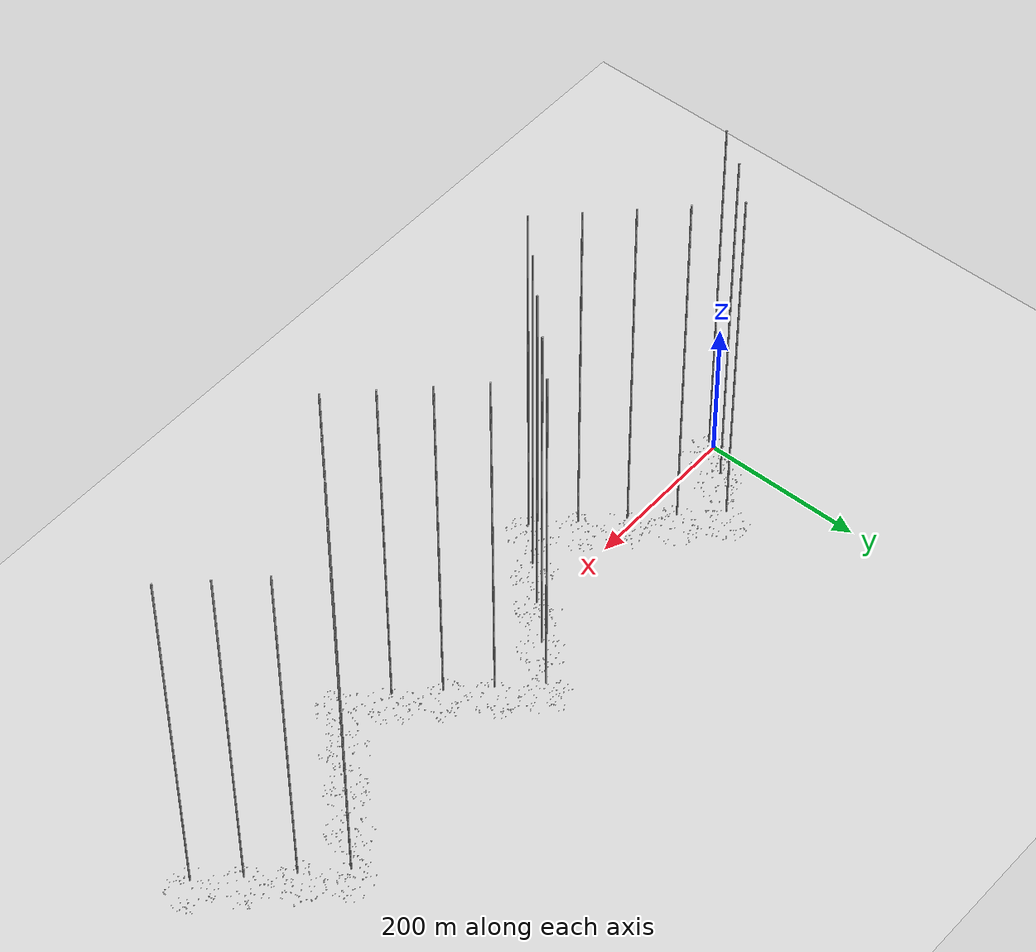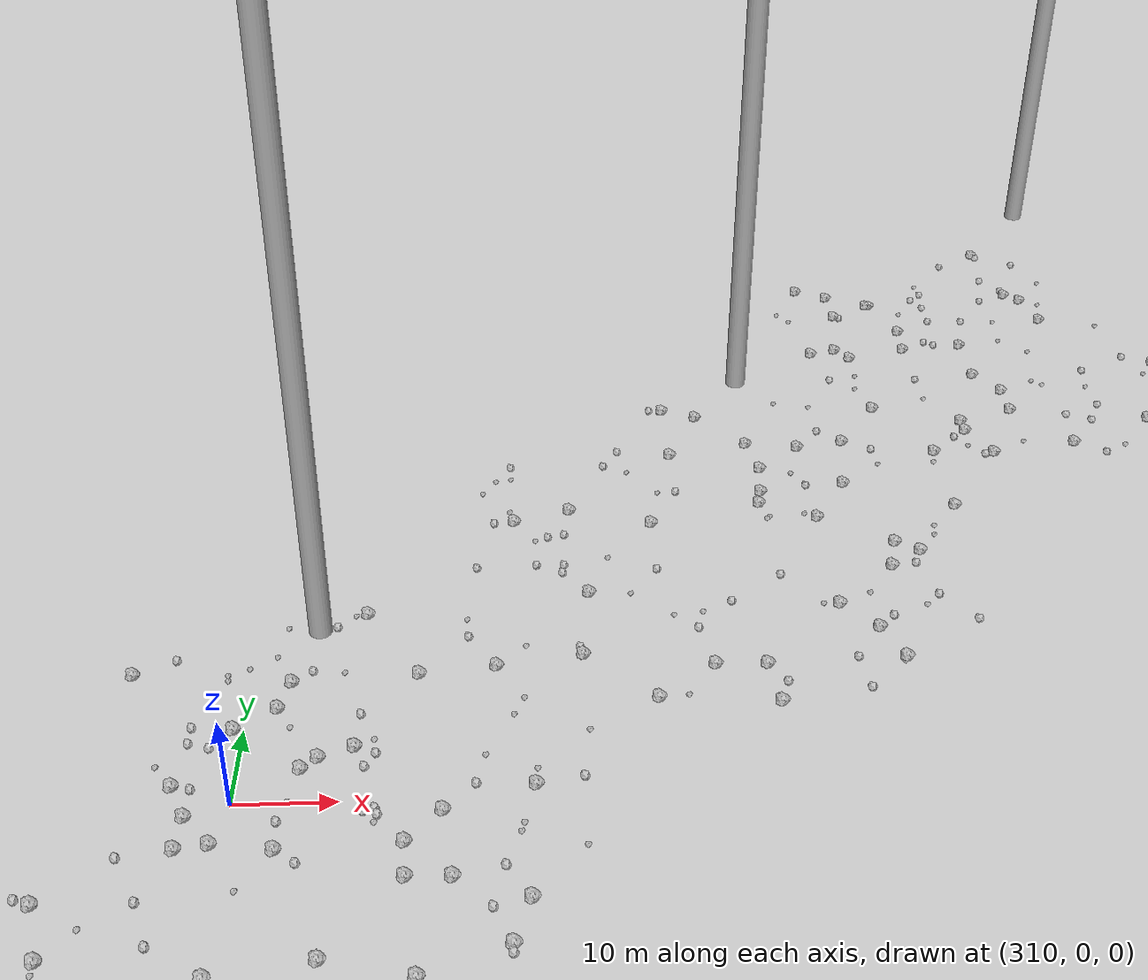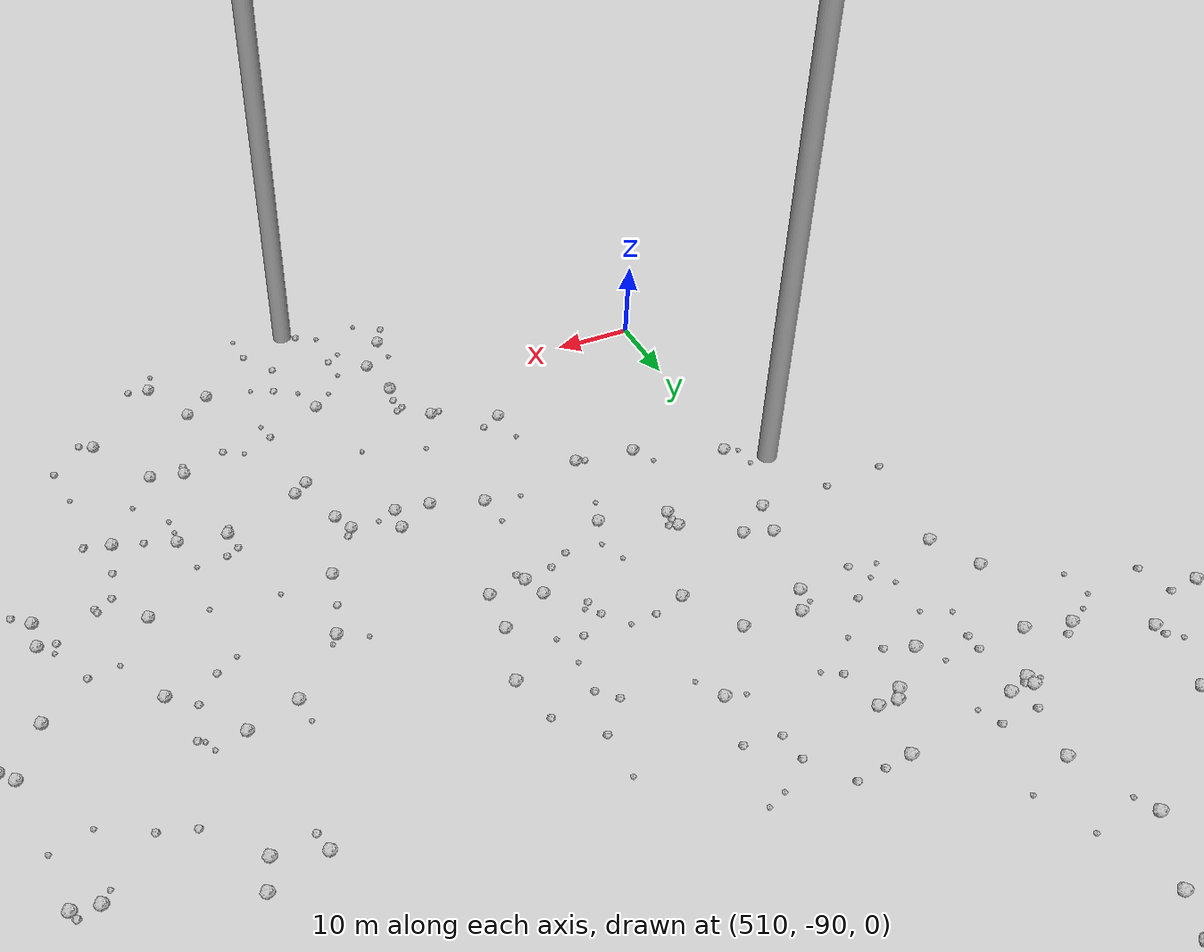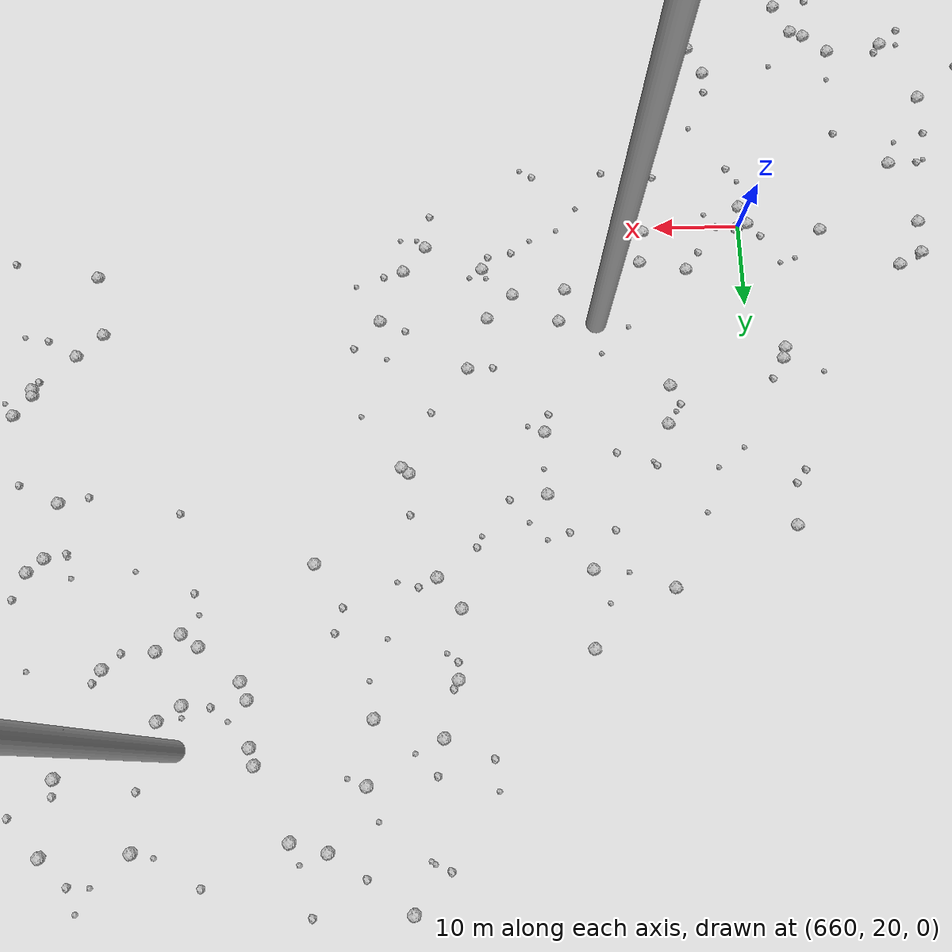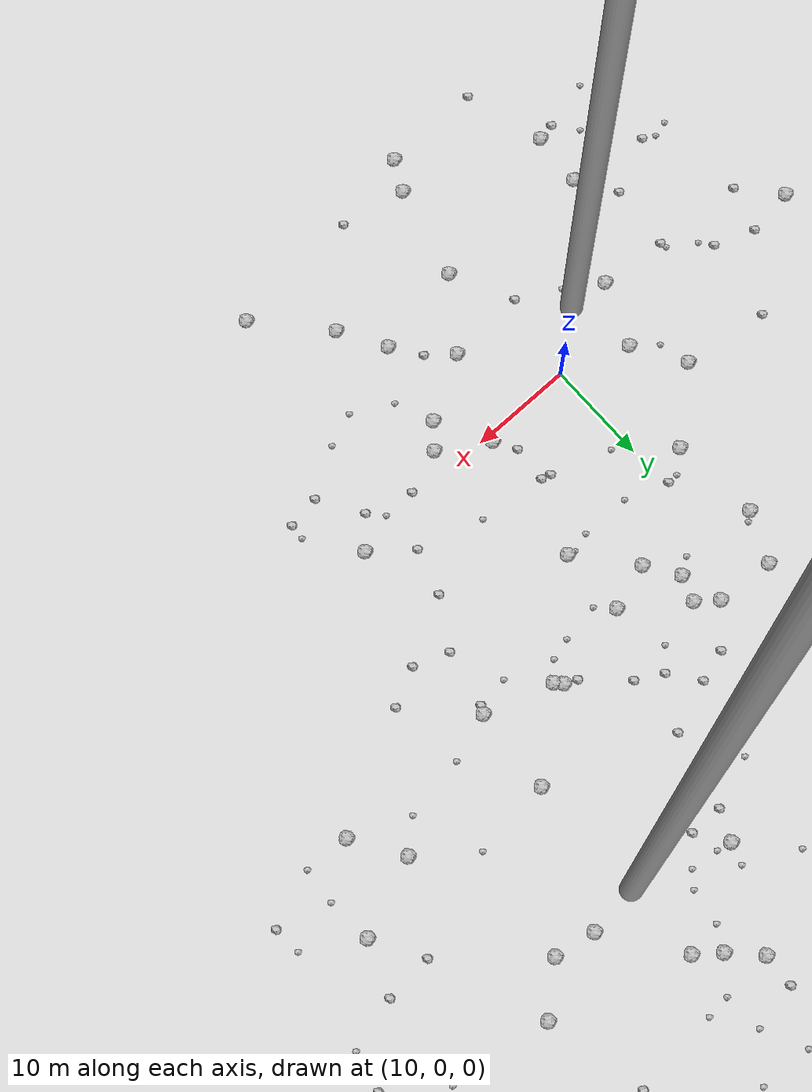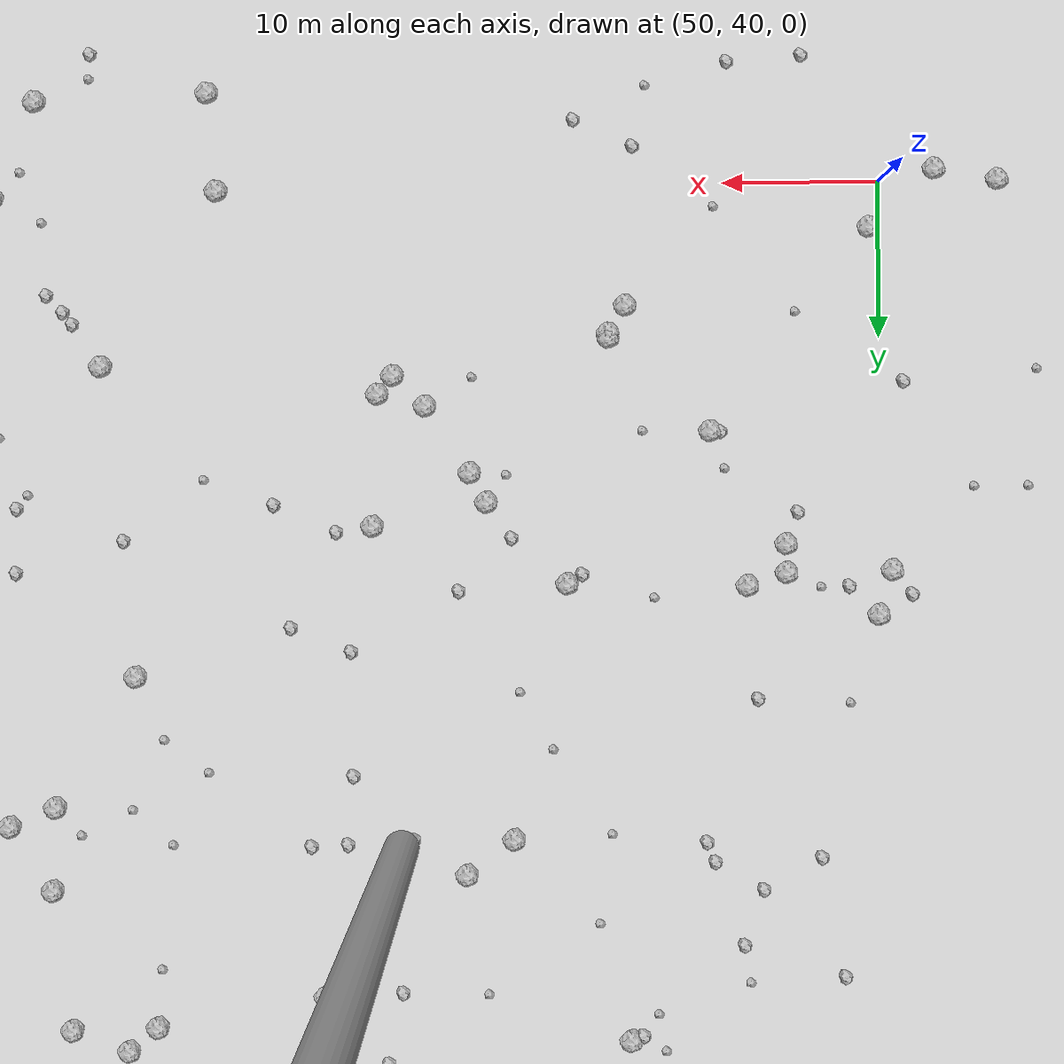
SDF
<sdf version="1.6">
 <world name="default">
  <include><uri>model://custom_ground</uri></include>
  <include><uri>model://sun</uri></include>
  <spherical_coordinates>
   <surface_model>EARTH_WGS84</surface_model>
   <latitude_deg>38.161479</latitude_deg>
   <longitude_deg>-122.454630</longitude_deg>
   <elevation>488.0</elevation>
   <heading_deg>90</heading_deg>
  </spherical_coordinates>
  <model name="rock1_0_0">
   <include><uri>model://rock1</uri><pose>6.683829319620614 12.563256110951997 0.5 0 0 0</pose></include>
  </model>
  <model name="rock1_0_1">
   <include><uri>model://rock1</uri><pose>9.08796225509801 -23.036213081461405 0.5 0 0 0</pose></include>
  </model>
  <model name="rock1_0_2">
   <include><uri>model://rock1</uri><pose>13.685944129815915 25.494887184255866 0.5 0 0 0</pose></include>
  </model>
  <model name="rock1_0_3">
   <include><uri>model://rock1</uri><pose>23.717331327281073 -2.2250579873348677 0.5 0 0 0</pose></include>
  </model>
  <model name="rock1_0_4">
   <include><uri>model://rock1</uri><pose>0.520594525025821 7.0740542030518725 0.5 0 0 0</pose></include>
  </model>
  <model name="rock1_0_5">
   <include><uri>model://rock1</uri><pose>-4.125925457058997 -18.343865225174383 0.5 0 0 0</pose></include>
  </model>
  <model name="rock1_0_6">
   <include><uri>model://rock1</uri><pose>21.88236892255437 -4.423500342052364 0.5 0 0 0</pose></include>
  </model>
  <model name="rock1_0_7">
   <include><uri>model://rock1</uri><pose>8.091820574988681 25.905427243451236 0.5 0 0 0</pose></include>
  </model>
  <model name="rock1_0_8">
   <include><uri>model://rock1</uri><pose>14.760941934575321 21.475962190216507 0.5 0 0 0</pose></include>
  </model>
  <model name="rock1_0_9">
   <include><uri>model://rock1</uri><pose>28.390816804770296 -23.16677727529754 0.5 0 0 0</pose></include>
  </model>
  <model name="rock1_0_10">
   <include><uri>model://rock1</uri><pose>20.24625109625547 -12.520809226118 0.5 0 0 0</pose></include>
  </model>
  <model name="rock1_0_11">
   <include><uri>model://rock1</uri><pose>11.291855326111527 -14.087074760044176 0.5 0 0 0</pose></include>
  </model>
  <model name="rock1_0_12">
   <include><uri>model://rock1</uri><pose>-17.536762615596786 1.1036908232266498 0.5 0 0 0</pose></include>
  </model>
  <model name="rock1_0_13">
   <include><uri>model://rock1</uri><pose>21.249378878466743 19.80832548098106 0.5 0 0 0</pose></include>
  </model>
  <model name="rock1_0_14">
   <include><uri>model://rock1</uri><pose>-3.679675316694798 -13.20739054047004 0.5 0 0 0</pose></include>
  </model>
  <model name="rock1_0_15">
   <include><uri>model://rock1</uri><pose>30.13876259033902 21.028865719001438 0.5 0 0 0</pose></include>
  </model>
  <model name="rock1_0_16">
   <include><uri>model://rock1</uri><pose>22.812282840596332 -16.89652458572579 0.5 0 0 0</pose></include>
  </model>
  <model name="rock1_0_17">
   <include><uri>model://rock1</uri><pose>16.81095708081552 18.398201418854228 0.5 0 0 0</pose></include>
  </model>
  <model name="rock1_0_18">
   <include><uri>model://rock1</uri><pose>34.754521971912396 0.6775441465180378 0.5 0 0 0</pose></include>
  </model>
  <model name="rock1_0_19">
   <include><uri>model://rock1</uri><pose>0.9990382940599005 -3.748029188255572 0.5 0 0 0</pose></include>
  </model>
  <model name="rock1_0_20">
   <include><uri>model://rock1</uri><pose>7.573008258058419 -25.951900329216965 0.5 0 0 0</pose></include>
  </model>
  <model name="rock1_0_21">
   <include><uri>model://rock1</uri><pose>15.92608936969635 -7.770130264954279 0.5 0 0 0</pose></include>
  </model>
  <model name="rock1_0_22">
   <include><uri>model://rock1</uri><pose>5.987800347408363 21.16573884028726 0.5 0 0 0</pose></include>
  </model>
  <model name="rock1_0_23">
   <include><uri>model://rock1</uri><pose>29.484117278330686 21.707811975816746 0.5 0 0 0</pose></include>
  </model>
  <model name="rock1_0_24">
   <include><uri>model://rock1</uri><pose>3.4993109547693493 2.244908886840662 0.5 0 0 0</pose></include>
  </model>
  <model name="rock1_0_25">
   <include><uri>model://rock1</uri><pose>19.10142445560796 0.6883380012048015 0.5 0 0 0</pose></include>
  </model>
  <model name="rock1_0_26">
   <include><uri>model://rock1</uri><pose>21.193138110962174 13.152814482495067 0.5 0 0 0</pose></include>
  </model>
  <model name="rock2_0_0">
   <include><uri>model://rock2</uri><pose>8.350652109842734 -8.14648882077795 0.3 0 0 0</pose></include>
  </model>
  <model name="rock2_0_1">
   <include><uri>model://rock2</uri><pose>28.251882004683097 22.286067011757225 0.3 0 0 0</pose></include>
  </model>
  <model name="rock2_0_2">
   <include><uri>model://rock2</uri><pose>38.0735040987362 -5.590192097599264 0.3 0 0 0</pose></include>
  </model>
  <model name="rock2_0_3">
   <include><uri>model://rock2</uri><pose>17.851666714785658 2.743183120974379 0.3 0 0 0</pose></include>
  </model>
  <model name="rock2_0_4">
   <include><uri>model://rock2</uri><pose>9.639766697022576 14.278633790830625 0.3 0 0 0</pose></include>
  </model>
  <model name="rock2_0_5">
   <include><uri>model://rock2</uri><pose>-2.3135984505754266 26.502269249257687 0.3 0 0 0</pose></include>
  </model>
  <model name="rock2_0_6">
   <include><uri>model://rock2</uri><pose>30.995019644533357 3.682215667107691 0.3 0 0 0</pose></include>
  </model>
  <model name="rock2_0_7">
   <include><uri>model://rock2</uri><pose>17.19444429230203 6.5329469914396086 0.3 0 0 0</pose></include>
  </model>
  <model name="rock2_0_8">
   <include><uri>model://rock2</uri><pose>-9.548882861327609 -16.309709474258664 0.3 0 0 0</pose></include>
  </model>
  <model name="rock2_0_9">
   <include><uri>model://rock2</uri><pose>-14.409704504121057 -2.5972309277436736 0.3 0 0 0</pose></include>
  </model>
  <model name="rock2_0_10">
   <include><uri>model://rock2</uri><pose>21.985507293479586 27.088809256989606 0.3 0 0 0</pose></include>
  </model>
  <model name="rock2_0_11">
   <include><uri>model://rock2</uri><pose>-13.047160031417231 1.7222564542742518 0.3 0 0 0</pose></include>
  </model>
  <model name="rock2_0_12">
   <include><uri>model://rock2</uri><pose>-5.865754008455964 -18.659980421858954 0.3 0 0 0</pose></include>
  </model>
  <model name="rock2_0_13">
   <include><uri>model://rock2</uri><pose>-5.56592280030628 -3.16200994876559 0.3 0 0 0</pose></include>
  </model>
  <model name="rock2_0_14">
   <include><uri>model://rock2</uri><pose>2.243895410631268 -6.8654983286858915 0.3 0 0 0</pose></include>
  </model>
  <model name="rock2_0_15">
   <include><uri>model://rock2</uri><pose>18.10771731803485 6.2773804008232545 0.3 0 0 0</pose></include>
  </model>
  <model name="rock2_0_16">
   <include><uri>model://rock2</uri><pose>32.307989607189725 -2.0114493193569807 0.3 0 0 0</pose></include>
  </model>
  <model name="rock2_0_17">
   <include><uri>model://rock2</uri><pose>-6.11795882356744 -9.484875695440689 0.3 0 0 0</pose></include>
  </model>
  <model name="rock2_0_18">
   <include><uri>model://rock2</uri><pose>18.269400574906463 -9.73524321047125 0.3 0 0 0</pose></include>
  </model>
  <model name="rock2_0_19">
   <include><uri>model://rock2</uri><pose>34.865374164592446 -6.085168206754176 0.3 0 0 0</pose></include>
  </model>
  <model name="rock2_0_20">
   <include><uri>model://rock2</uri><pose>32.349545852880006 8.113038989074234 0.3 0 0 0</pose></include>
  </model>
  <model name="rock2_0_21">
   <include><uri>model://rock2</uri><pose>27.798120591699004 -0.6454283931167808 0.3 0 0 0</pose></include>
  </model>
  <model name="rock2_0_22">
   <include><uri>model://rock2</uri><pose>15.380447295844867 -24.292995372157794 0.3 0 0 0</pose></include>
  </model>
  <model name="rock2_0_23">
   <include><uri>model://rock2</uri><pose>-11.383707649386825 -11.983264362743583 0.3 0 0 0</pose></include>
  </model>
  <model name="rock2_0_24">
   <include><uri>model://rock2</uri><pose>-7.866536531166766 8.257973525109108 0.3 0 0 0</pose></include>
  </model>
  <model name="rock2_0_25">
   <include><uri>model://rock2</uri><pose>-1.9235701892559227 -26.0966620384546 0.3 0 0 0</pose></include>
  </model>
  <model name="rock2_0_26">
   <include><uri>model://rock2</uri><pose>-9.1848462026959 0.31101427849172225 0.3 0 0 0</pose></include>
  </model>
  <model name="rock3_0_0">
   <include><uri>model://rock3</uri><pose>30.995772117568677 -0.6287481198843388 0.2 0 0 0</pose></include>
  </model>
  <model name="rock3_0_1">
   <include><uri>model://rock3</uri><pose>38.17532104489711 -4.132349837530921 0.2 0 0 0</pose></include>
  </model>
  <model name="rock3_0_2">
   <include><uri>model://rock3</uri><pose>-12.573494717524724 -11.38805208332563 0.2 0 0 0</pose></include>
  </model>
  <model name="rock3_0_3">
   <include><uri>model://rock3</uri><pose>8.574873452863347 14.233047599251748 0.2 0 0 0</pose></include>
  </model>
  <model name="rock3_0_4">
   <include><uri>model://rock3</uri><pose>18.55158561217661 12.760124763365411 0.2 0 0 0</pose></include>
  </model>
  <model name="rock3_0_5">
   <include><uri>model://rock3</uri><pose>20.1898008757098 25.156410638098137 0.2 0 0 0</pose></include>
  </model>
  <model name="rock3_0_6">
   <include><uri>model://rock3</uri><pose>11.4355155089123 8.46124159024253 0.2 0 0 0</pose></include>
  </model>
  <model name="rock3_0_7">
   <include><uri>model://rock3</uri><pose>-14.085990657357566 -11.800559569086492 0.2 0 0 0</pose></include>
  </model>
  <model name="rock3_0_8">
   <include><uri>model://rock3</uri><pose>13.745544496064177 12.774011002982007 0.2 0 0 0</pose></include>
  </model>
  <model name="rock3_0_9">
   <include><uri>model://rock3</uri><pose>-4.270213315576996 -13.538970089172718 0.2 0 0 0</pose></include>
  </model>
  <model name="rock3_0_10">
   <include><uri>model://rock3</uri><pose>20.398486694463905 13.308799059776277 0.2 0 0 0</pose></include>
  </model>
  <model name="rock3_0_11">
   <include><uri>model://rock3</uri><pose>24.646817254318172 5.510705409827615 0.2 0 0 0</pose></include>
  </model>
  <model name="rock3_0_12">
   <include><uri>model://rock3</uri><pose>30.34310300514599 -8.885265561508543 0.2 0 0 0</pose></include>
  </model>
  <model name="rock3_0_13">
   <include><uri>model://rock3</uri><pose>4.325186331612898 -6.048765998670461 0.2 0 0 0</pose></include>
  </model>
  <model name="rock3_0_14">
   <include><uri>model://rock3</uri><pose>27.143767522219072 -10.122952679448773 0.2 0 0 0</pose></include>
  </model>
  <model name="rock3_0_15">
   <include><uri>model://rock3</uri><pose>-5.7330646044334355 -2.580170149528371 0.2 0 0 0</pose></include>
  </model>
  <model name="rock3_0_16">
   <include><uri>model://rock3</uri><pose>-4.7268509585006875 19.341592500941516 0.2 0 0 0</pose></include>
  </model>
  <model name="rock3_0_17">
   <include><uri>model://rock3</uri><pose>6.724053091510896 21.830054039668198 0.2 0 0 0</pose></include>
  </model>
  <model name="rock3_0_18">
   <include><uri>model://rock3</uri><pose>-12.031612430089647 17.04907572737382 0.2 0 0 0</pose></include>
  </model>
  <model name="rock3_0_19">
   <include><uri>model://rock3</uri><pose>-7.617742291193677 -16.55246639083449 0.2 0 0 0</pose></include>
  </model>
  <model name="rock3_0_20">
   <include><uri>model://rock3</uri><pose>22.70273282856897 18.276699293163595 0.2 0 0 0</pose></include>
  </model>
  <model name="rock3_0_21">
   <include><uri>model://rock3</uri><pose>-10.66404358357872 -19.896532026697066 0.2 0 0 0</pose></include>
  </model>
  <model name="rock3_0_22">
   <include><uri>model://rock3</uri><pose>1.183934093809306 4.0648662383153535 0.2 0 0 0</pose></include>
  </model>
  <model name="rock3_0_23">
   <include><uri>model://rock3</uri><pose>-8.266911470519819 -0.8902304795523506 0.2 0 0 0</pose></include>
  </model>
  <model name="rock3_0_24">
   <include><uri>model://rock3</uri><pose>13.136828886015067 20.426468377709007 0.2 0 0 0</pose></include>
  </model>
  <model name="rock3_0_25">
   <include><uri>model://rock3</uri><pose>1.9197062996323595 28.452312966019498 0.2 0 0 0</pose></include>
  </model>
  <model name="rock3_0_26">
   <include><uri>model://rock3</uri><pose>23.342010235960608 -8.094416010092004 0.2 0 0 0</pose></include>
  </model>
  <model name="rock1_1_0">
   <include><uri>model://rock1</uri><pose>28.056223970185236 42.1511018580026 0.5 0 0 0</pose></include>
  </model>
  <model name="rock1_1_1">
   <include><uri>model://rock1</uri><pose>49.34220460187487 64.91999876459457 0.5 0 0 0</pose></include>
  </model>
  <model name="rock1_1_2">
   <include><uri>model://rock1</uri><pose>57.73370328499542 27.022447551136334 0.5 0 0 0</pose></include>
  </model>
  <model name="rock1_1_3">
   <include><uri>model://rock1</uri><pose>12.667745485829474 37.96550054791757 0.5 0 0 0</pose></include>
  </model>
  <model name="rock1_1_4">
   <include><uri>model://rock1</uri><pose>37.43221225640934 47.01995308655965 0.5 0 0 0</pose></include>
  </model>
  <model name="rock1_1_5">
   <include><uri>model://rock1</uri><pose>67.45338723451556 49.88257003163394 0.5 0 0 0</pose></include>
  </model>
  <model name="rock1_1_6">
   <include><uri>model://rock1</uri><pose>23.066219031625604 49.8344169041278 0.5 0 0 0</pose></include>
  </model>
  <model name="rock1_1_7">
   <include><uri>model://rock1</uri><pose>15.626745156867576 23.948091827355476 0.5 0 0 0</pose></include>
  </model>
  <model name="rock1_1_8">
   <include><uri>model://rock1</uri><pose>56.145880724698614 63.19602686730637 0.5 0 0 0</pose></include>
  </model>
  <model name="rock1_1_9">
   <include><uri>model://rock1</uri><pose>36.75122501682283 18.959542766967807 0.5 0 0 0</pose></include>
  </model>
  <model name="rock1_1_10">
   <include><uri>model://rock1</uri><pose>53.27590882144037 19.1746628011483 0.5 0 0 0</pose></include>
  </model>
  <model name="rock1_1_11">
   <include><uri>model://rock1</uri><pose>60.982259007200156 55.92236198281403 0.5 0 0 0</pose></include>
  </model>
  <model name="rock1_1_12">
   <include><uri>model://rock1</uri><pose>18.451715200095922 34.74694500383948 0.5 0 0 0</pose></include>
  </model>
  <model name="rock1_1_13">
   <include><uri>model://rock1</uri><pose>42.46185283753629 39.9115952897444 0.5 0 0 0</pose></include>
  </model>
  <model name="rock1_1_14">
   <include><uri>model://rock1</uri><pose>32.78269918293253 59.67794000026769 0.5 0 0 0</pose></include>
  </model>
  <model name="rock1_1_15">
   <include><uri>model://rock1</uri><pose>50.270983818105776 24.01079648071694 0.5 0 0 0</pose></include>
  </model>
  <model name="rock1_1_16">
   <include><uri>model://rock1</uri><pose>67.46357092064106 49.61125251005422 0.5 0 0 0</pose></include>
  </model>
  <model name="rock1_1_17">
   <include><uri>model://rock1</uri><pose>50.229905666814496 67.77046356360951 0.5 0 0 0</pose></include>
  </model>
  <model name="rock1_1_18">
   <include><uri>model://rock1</uri><pose>46.500322127935796 39.20332990129195 0.5 0 0 0</pose></include>
  </model>
  <model name="rock1_1_19">
   <include><uri>model://rock1</uri><pose>50.71988637210234 42.923741312898095 0.5 0 0 0</pose></include>
  </model>
  <model name="rock1_1_20">
   <include><uri>model://rock1</uri><pose>56.13320191608209 65.04182184427856 0.5 0 0 0</pose></include>
  </model>
  <model name="rock1_1_21">
   <include><uri>model://rock1</uri><pose>35.18945371693917 48.81659172297396 0.5 0 0 0</pose></include>
  </model>
  <model name="rock1_1_22">
   <include><uri>model://rock1</uri><pose>32.58031911072091 51.477340546973636 0.5 0 0 0</pose></include>
  </model>
  <model name="rock1_1_23">
   <include><uri>model://rock1</uri><pose>22.585677597125734 57.82980973483659 0.5 0 0 0</pose></include>
  </model>
  <model name="rock1_1_24">
   <include><uri>model://rock1</uri><pose>24.78565183978671 52.73232918974362 0.5 0 0 0</pose></include>
  </model>
  <model name="rock1_1_25">
   <include><uri>model://rock1</uri><pose>66.35640319943128 47.83584087792627 0.5 0 0 0</pose></include>
  </model>
  <model name="rock1_1_26">
   <include><uri>model://rock1</uri><pose>37.284507014130824 27.2793903291796 0.5 0 0 0</pose></include>
  </model>
  <model name="rock2_1_0">
   <include><uri>model://rock2</uri><pose>69.57333441805498 35.908932720560784 0.3 0 0 0</pose></include>
  </model>
  <model name="rock2_1_1">
   <include><uri>model://rock2</uri><pose>12.547991300262849 49.573082279535846 0.3 0 0 0</pose></include>
  </model>
  <model name="rock2_1_2">
   <include><uri>model://rock2</uri><pose>19.88377351583656 29.887723839841726 0.3 0 0 0</pose></include>
  </model>
  <model name="rock2_1_3">
   <include><uri>model://rock2</uri><pose>52.073381057199846 65.97458273493643 0.3 0 0 0</pose></include>
  </model>
  <model name="rock2_1_4">
   <include><uri>model://rock2</uri><pose>48.023412710379674 66.5126730435376 0.3 0 0 0</pose></include>
  </model>
  <model name="rock2_1_5">
   <include><uri>model://rock2</uri><pose>24.813883137035504 31.821274476580825 0.3 0 0 0</pose></include>
  </model>
  <model name="rock2_1_6">
   <include><uri>model://rock2</uri><pose>38.567690753185985 11.497173179888618 0.3 0 0 0</pose></include>
  </model>
  <model name="rock2_1_7">
   <include><uri>model://rock2</uri><pose>26.71146646196392 39.26683611659411 0.3 0 0 0</pose></include>
  </model>
  <model name="rock2_1_8">
   <include><uri>model://rock2</uri><pose>48.51718678644196 52.839378421433054 0.3 0 0 0</pose></include>
  </model>
  <model name="rock2_1_9">
   <include><uri>model://rock2</uri><pose>63.21196130565793 21.107732842804463 0.3 0 0 0</pose></include>
  </model>
  <model name="rock2_1_10">
   <include><uri>model://rock2</uri><pose>24.543416506684245 25.702986272909307 0.3 0 0 0</pose></include>
  </model>
  <model name="rock2_1_11">
   <include><uri>model://rock2</uri><pose>30.00135686797931 39.262233122839646 0.3 0 0 0</pose></include>
  </model>
  <model name="rock2_1_12">
   <include><uri>model://rock2</uri><pose>16.804593208920874 28.937505003081 0.3 0 0 0</pose></include>
  </model>
  <model name="rock2_1_13">
   <include><uri>model://rock2</uri><pose>17.008586936900702 45.361178403493284 0.3 0 0 0</pose></include>
  </model>
  <model name="rock2_1_14">
   <include><uri>model://rock2</uri><pose>55.340592785516094 61.19158414525472 0.3 0 0 0</pose></include>
  </model>
  <model name="rock2_1_15">
   <include><uri>model://rock2</uri><pose>54.93744110790159 31.873863012904554 0.3 0 0 0</pose></include>
  </model>
  <model name="rock2_1_16">
   <include><uri>model://rock2</uri><pose>16.0564831177988 34.88946545380955 0.3 0 0 0</pose></include>
  </model>
  <model name="rock2_1_17">
   <include><uri>model://rock2</uri><pose>35.160679629022894 12.73948843438814 0.3 0 0 0</pose></include>
  </model>
  <model name="rock2_1_18">
   <include><uri>model://rock2</uri><pose>21.705616807695748 57.53727130275818 0.3 0 0 0</pose></include>
  </model>
  <model name="rock2_1_19">
   <include><uri>model://rock2</uri><pose>36.33505813316743 18.228600790441217 0.3 0 0 0</pose></include>
  </model>
  <model name="rock2_1_20">
   <include><uri>model://rock2</uri><pose>21.266198270252442 52.42187393822324 0.3 0 0 0</pose></include>
  </model>
  <model name="rock2_1_21">
   <include><uri>model://rock2</uri><pose>65.80699210371773 37.62751557965769 0.3 0 0 0</pose></include>
  </model>
  <model name="rock2_1_22">
   <include><uri>model://rock2</uri><pose>60.27661226587599 55.98075991768513 0.3 0 0 0</pose></include>
  </model>
  <model name="rock2_1_23">
   <include><uri>model://rock2</uri><pose>12.596608035284975 50.327248665449034 0.3 0 0 0</pose></include>
  </model>
  <model name="rock2_1_24">
   <include><uri>model://rock2</uri><pose>42.185378613016894 13.287745153937918 0.3 0 0 0</pose></include>
  </model>
  <model name="rock2_1_25">
   <include><uri>model://rock2</uri><pose>32.72429108208045 54.809906312059304 0.3 0 0 0</pose></include>
  </model>
  <model name="rock2_1_26">
   <include><uri>model://rock2</uri><pose>59.70504612208723 32.250523089633845 0.3 0 0 0</pose></include>
  </model>
  <model name="rock3_1_0">
   <include><uri>model://rock3</uri><pose>33.33167484922067 43.02719703290806 0.2 0 0 0</pose></include>
  </model>
  <model name="rock3_1_1">
   <include><uri>model://rock3</uri><pose>40.492618742125146 59.55367934579929 0.2 0 0 0</pose></include>
  </model>
  <model name="rock3_1_2">
   <include><uri>model://rock3</uri><pose>35.314296820162696 59.82808809923694 0.2 0 0 0</pose></include>
  </model>
  <model name="rock3_1_3">
   <include><uri>model://rock3</uri><pose>26.45671504820576 18.85962690484642 0.2 0 0 0</pose></include>
  </model>
  <model name="rock3_1_4">
   <include><uri>model://rock3</uri><pose>59.99619537651767 58.31118330070576 0.2 0 0 0</pose></include>
  </model>
  <model name="rock3_1_5">
   <include><uri>model://rock3</uri><pose>60.607380619753116 41.48548373777216 0.2 0 0 0</pose></include>
  </model>
  <model name="rock3_1_6">
   <include><uri>model://rock3</uri><pose>43.98192642667082 59.56261005606345 0.2 0 0 0</pose></include>
  </model>
  <model name="rock3_1_7">
   <include><uri>model://rock3</uri><pose>55.41064404893185 48.270076204834055 0.2 0 0 0</pose></include>
  </model>
  <model name="rock3_1_8">
   <include><uri>model://rock3</uri><pose>17.155568499384614 50.31103490436728 0.2 0 0 0</pose></include>
  </model>
  <model name="rock3_1_9">
   <include><uri>model://rock3</uri><pose>21.79581106273728 37.343785245185956 0.2 0 0 0</pose></include>
  </model>
  <model name="rock3_1_10">
   <include><uri>model://rock3</uri><pose>58.00889334845399 22.51248179912107 0.2 0 0 0</pose></include>
  </model>
  <model name="rock3_1_11">
   <include><uri>model://rock3</uri><pose>63.04215735572306 23.835573451988257 0.2 0 0 0</pose></include>
  </model>
  <model name="rock3_1_12">
   <include><uri>model://rock3</uri><pose>33.212353202403946 17.82129677315698 0.2 0 0 0</pose></include>
  </model>
  <model name="rock3_1_13">
   <include><uri>model://rock3</uri><pose>41.33620433195575 20.523634425498642 0.2 0 0 0</pose></include>
  </model>
  <model name="rock3_1_14">
   <include><uri>model://rock3</uri><pose>28.655266231778114 44.249158133935545 0.2 0 0 0</pose></include>
  </model>
  <model name="rock3_1_15">
   <include><uri>model://rock3</uri><pose>57.68486609705546 18.931140891879494 0.2 0 0 0</pose></include>
  </model>
  <model name="rock3_1_16">
   <include><uri>model://rock3</uri><pose>37.567133921611635 51.81868611617651 0.2 0 0 0</pose></include>
  </model>
  <model name="rock3_1_17">
   <include><uri>model://rock3</uri><pose>37.316838701793216 55.69620036214223 0.2 0 0 0</pose></include>
  </model>
  <model name="rock3_1_18">
   <include><uri>model://rock3</uri><pose>33.88106252562223 46.526134635886066 0.2 0 0 0</pose></include>
  </model>
  <model name="rock3_1_19">
   <include><uri>model://rock3</uri><pose>29.411176560798356 41.852017095572535 0.2 0 0 0</pose></include>
  </model>
  <model name="rock3_1_20">
   <include><uri>model://rock3</uri><pose>28.578585739724154 19.44780628923199 0.2 0 0 0</pose></include>
  </model>
  <model name="rock3_1_21">
   <include><uri>model://rock3</uri><pose>39.90807990428773 52.05069816231821 0.2 0 0 0</pose></include>
  </model>
  <model name="rock3_1_22">
   <include><uri>model://rock3</uri><pose>44.99126345408479 28.06007465469959 0.2 0 0 0</pose></include>
  </model>
  <model name="rock3_1_23">
   <include><uri>model://rock3</uri><pose>64.94049163555532 33.67955239585654 0.2 0 0 0</pose></include>
  </model>
  <model name="rock3_1_24">
   <include><uri>model://rock3</uri><pose>47.488126428793805 21.545459164189303 0.2 0 0 0</pose></include>
  </model>
  <model name="rock3_1_25">
   <include><uri>model://rock3</uri><pose>23.64992485627635 46.77590146448694 0.2 0 0 0</pose></include>
  </model>
  <model name="rock3_1_26">
   <include><uri>model://rock3</uri><pose>32.181435848047286 41.557784332373615 0.2 0 0 0</pose></include>
  </model>
  <model name="rock1_2_0">
   <include><uri>model://rock1</uri><pose>98.51026877354734 95.39561146732069 0.5 0 0 0</pose></include>
  </model>
  <model name="rock1_2_1">
   <include><uri>model://rock1</uri><pose>75.35142733211235 60.39248976548231 0.5 0 0 0</pose></include>
  </model>
  <model name="rock1_2_2">
   <include><uri>model://rock1</uri><pose>82.2891047257682 53.40834057277941 0.5 0 0 0</pose></include>
  </model>
  <model name="rock1_2_3">
   <include><uri>model://rock1</uri><pose>97.92780879434515 71.41509928562935 0.5 0 0 0</pose></include>
  </model>
  <model name="rock1_2_4">
   <include><uri>model://rock1</uri><pose>70.20265242295366 65.6500057010577 0.5 0 0 0</pose></include>
  </model>
  <model name="rock1_2_5">
   <include><uri>model://rock1</uri><pose>82.67726062279297 61.870143346190986 0.5 0 0 0</pose></include>
  </model>
  <model name="rock1_2_6">
   <include><uri>model://rock1</uri><pose>103.13673121320748 79.76198078003735 0.5 0 0 0</pose></include>
  </model>
  <model name="rock1_2_7">
   <include><uri>model://rock1</uri><pose>106.05889027343898 80.96816482652171 0.5 0 0 0</pose></include>
  </model>
  <model name="rock1_2_8">
   <include><uri>model://rock1</uri><pose>86.96912468112119 106.8168372232061 0.5 0 0 0</pose></include>
  </model>
  <model name="rock1_2_9">
   <include><uri>model://rock1</uri><pose>79.24541092356165 54.190960011494546 0.5 0 0 0</pose></include>
  </model>
  <model name="rock1_2_10">
   <include><uri>model://rock1</uri><pose>108.24419129497193 74.90103067750454 0.5 0 0 0</pose></include>
  </model>
  <model name="rock1_2_11">
   <include><uri>model://rock1</uri><pose>94.53765485307837 105.09783104382572 0.5 0 0 0</pose></include>
  </model>
  <model name="rock1_2_12">
   <include><uri>model://rock1</uri><pose>77.03213371065777 99.31181343939211 0.5 0 0 0</pose></include>
  </model>
  <model name="rock1_2_13">
   <include><uri>model://rock1</uri><pose>88.25865831995293 99.08784374243496 0.5 0 0 0</pose></include>
  </model>
  <model name="rock1_2_14">
   <include><uri>model://rock1</uri><pose>81.30721424672862 52.22654431768969 0.5 0 0 0</pose></include>
  </model>
  <model name="rock1_2_15">
   <include><uri>model://rock1</uri><pose>76.77410043925475 84.28131122329903 0.5 0 0 0</pose></include>
  </model>
  <model name="rock1_2_16">
   <include><uri>model://rock1</uri><pose>96.66910229466768 93.89860875706562 0.5 0 0 0</pose></include>
  </model>
  <model name="rock1_2_17">
   <include><uri>model://rock1</uri><pose>74.63722217967704 102.86625103880604 0.5 0 0 0</pose></include>
  </model>
  <model name="rock1_2_18">
   <include><uri>model://rock1</uri><pose>65.17507055898318 104.09106892985892 0.5 0 0 0</pose></include>
  </model>
  <model name="rock1_2_19">
   <include><uri>model://rock1</uri><pose>102.13693245046245 94.03767038110476 0.5 0 0 0</pose></include>
  </model>
  <model name="rock1_2_20">
   <include><uri>model://rock1</uri><pose>103.33193492609611 85.07950896697606 0.5 0 0 0</pose></include>
  </model>
  <model name="rock1_2_21">
   <include><uri>model://rock1</uri><pose>58.657782696129736 65.85323436852028 0.5 0 0 0</pose></include>
  </model>
  <model name="rock1_2_22">
   <include><uri>model://rock1</uri><pose>74.76398501344153 105.5823862270077 0.5 0 0 0</pose></include>
  </model>
  <model name="rock1_2_23">
   <include><uri>model://rock1</uri><pose>85.89238423266725 92.01675961182292 0.5 0 0 0</pose></include>
  </model>
  <model name="rock1_2_24">
   <include><uri>model://rock1</uri><pose>76.41103708959366 58.48956927027336 0.5 0 0 0</pose></include>
  </model>
  <model name="rock1_2_25">
   <include><uri>model://rock1</uri><pose>66.33456361046606 94.97735284360272 0.5 0 0 0</pose></include>
  </model>
  <model name="rock1_2_26">
   <include><uri>model://rock1</uri><pose>73.72852443394271 82.0323612697707 0.5 0 0 0</pose></include>
  </model>
  <model name="rock2_2_0">
   <include><uri>model://rock2</uri><pose>80.91294974774362 91.86856049421888 0.3 0 0 0</pose></include>
  </model>
  <model name="rock2_2_1">
   <include><uri>model://rock2</uri><pose>84.00560137130682 77.92965055807366 0.3 0 0 0</pose></include>
  </model>
  <model name="rock2_2_2">
   <include><uri>model://rock2</uri><pose>84.98756150190876 62.2625831368093 0.3 0 0 0</pose></include>
  </model>
  <model name="rock2_2_3">
   <include><uri>model://rock2</uri><pose>84.3737847892096 82.32450790662398 0.3 0 0 0</pose></include>
  </model>
  <model name="rock2_2_4">
   <include><uri>model://rock2</uri><pose>84.09687813505204 69.94400180090801 0.3 0 0 0</pose></include>
  </model>
  <model name="rock2_2_5">
   <include><uri>model://rock2</uri><pose>105.54354765578739 64.72859432942914 0.3 0 0 0</pose></include>
  </model>
  <model name="rock2_2_6">
   <include><uri>model://rock2</uri><pose>60.80518244070582 83.62092488957124 0.3 0 0 0</pose></include>
  </model>
  <model name="rock2_2_7">
   <include><uri>model://rock2</uri><pose>61.32481513114162 82.34242977759317 0.3 0 0 0</pose></include>
  </model>
  <model name="rock2_2_8">
   <include><uri>model://rock2</uri><pose>57.702897918814486 85.4185044107989 0.3 0 0 0</pose></include>
  </model>
  <model name="rock2_2_9">
   <include><uri>model://rock2</uri><pose>75.84501888782606 106.58922071448129 0.3 0 0 0</pose></include>
  </model>
  <model name="rock2_2_10">
   <include><uri>model://rock2</uri><pose>88.99097096169882 60.49108474595084 0.3 0 0 0</pose></include>
  </model>
  <model name="rock2_2_11">
   <include><uri>model://rock2</uri><pose>57.9873503823451 73.17710038573217 0.3 0 0 0</pose></include>
  </model>
  <model name="rock2_2_12">
   <include><uri>model://rock2</uri><pose>65.49189007003768 94.7416225583143 0.3 0 0 0</pose></include>
  </model>
  <model name="rock2_2_13">
   <include><uri>model://rock2</uri><pose>73.97744273950067 100.9148083648121 0.3 0 0 0</pose></include>
  </model>
  <model name="rock2_2_14">
   <include><uri>model://rock2</uri><pose>53.953553173390176 83.3831825295216 0.3 0 0 0</pose></include>
  </model>
  <model name="rock2_2_15">
   <include><uri>model://rock2</uri><pose>77.15516396194424 66.10877349325989 0.3 0 0 0</pose></include>
  </model>
  <model name="rock2_2_16">
   <include><uri>model://rock2</uri><pose>52.504944795378286 91.05937550751847 0.3 0 0 0</pose></include>
  </model>
  <model name="rock2_2_17">
   <include><uri>model://rock2</uri><pose>82.34064160909608 107.25401615414751 0.3 0 0 0</pose></include>
  </model>
  <model name="rock2_2_18">
   <include><uri>model://rock2</uri><pose>80.13196567650088 82.03960474844924 0.3 0 0 0</pose></include>
  </model>
  <model name="rock2_2_19">
   <include><uri>model://rock2</uri><pose>84.08086268024752 94.70993832486471 0.3 0 0 0</pose></include>
  </model>
  <model name="rock2_2_20">
   <include><uri>model://rock2</uri><pose>73.74030224647524 62.72728181437991 0.3 0 0 0</pose></include>
  </model>
  <model name="rock2_2_21">
   <include><uri>model://rock2</uri><pose>86.71968797978084 82.43015172146279 0.3 0 0 0</pose></include>
  </model>
  <model name="rock2_2_22">
   <include><uri>model://rock2</uri><pose>98.63197639463303 62.7286913637612 0.3 0 0 0</pose></include>
  </model>
  <model name="rock2_2_23">
   <include><uri>model://rock2</uri><pose>87.94571492163766 68.38527317441395 0.3 0 0 0</pose></include>
  </model>
  <model name="rock2_2_24">
   <include><uri>model://rock2</uri><pose>58.96677430192666 88.98273313073122 0.3 0 0 0</pose></include>
  </model>
  <model name="rock2_2_25">
   <include><uri>model://rock2</uri><pose>69.20855166493509 65.0836910028525 0.3 0 0 0</pose></include>
  </model>
  <model name="rock2_2_26">
   <include><uri>model://rock2</uri><pose>81.85435024413128 96.41376006465049 0.3 0 0 0</pose></include>
  </model>
  <model name="rock3_2_0">
   <include><uri>model://rock3</uri><pose>81.78637095736873 104.54334321036956 0.2 0 0 0</pose></include>
  </model>
  <model name="rock3_2_1">
   <include><uri>model://rock3</uri><pose>96.34765430084002 90.20381903664885 0.2 0 0 0</pose></include>
  </model>
  <model name="rock3_2_2">
   <include><uri>model://rock3</uri><pose>52.02007708808091 73.42394227201339 0.2 0 0 0</pose></include>
  </model>
  <model name="rock3_2_3">
   <include><uri>model://rock3</uri><pose>95.58186969888683 82.22426968214033 0.2 0 0 0</pose></include>
  </model>
  <model name="rock3_2_4">
   <include><uri>model://rock3</uri><pose>93.25676883267317 77.5995602979926 0.2 0 0 0</pose></include>
  </model>
  <model name="rock3_2_5">
   <include><uri>model://rock3</uri><pose>64.01325234688578 95.71045012974898 0.2 0 0 0</pose></include>
  </model>
  <model name="rock3_2_6">
   <include><uri>model://rock3</uri><pose>64.56482322714928 66.58206375657974 0.2 0 0 0</pose></include>
  </model>
  <model name="rock3_2_7">
   <include><uri>model://rock3</uri><pose>53.845353550470534 65.96423826868671 0.2 0 0 0</pose></include>
  </model>
  <model name="rock3_2_8">
   <include><uri>model://rock3</uri><pose>76.1965060021059 52.323883914192386 0.2 0 0 0</pose></include>
  </model>
  <model name="rock3_2_9">
   <include><uri>model://rock3</uri><pose>59.74938431953373 101.78558676623436 0.2 0 0 0</pose></include>
  </model>
  <model name="rock3_2_10">
   <include><uri>model://rock3</uri><pose>98.16838014470562 79.95179307612761 0.2 0 0 0</pose></include>
  </model>
  <model name="rock3_2_11">
   <include><uri>model://rock3</uri><pose>93.44759853979936 58.797522009250386 0.2 0 0 0</pose></include>
  </model>
  <model name="rock3_2_12">
   <include><uri>model://rock3</uri><pose>71.13626864713353 76.27525113757348 0.2 0 0 0</pose></include>
  </model>
  <model name="rock3_2_13">
   <include><uri>model://rock3</uri><pose>96.11490513612685 75.47198467240088 0.2 0 0 0</pose></include>
  </model>
  <model name="rock3_2_14">
   <include><uri>model://rock3</uri><pose>85.30427181662697 105.84595614941352 0.2 0 0 0</pose></include>
  </model>
  <model name="rock3_2_15">
   <include><uri>model://rock3</uri><pose>65.25180933632733 55.852738602322916 0.2 0 0 0</pose></include>
  </model>
  <model name="rock3_2_16">
   <include><uri>model://rock3</uri><pose>67.37677408780993 81.7427856720207 0.2 0 0 0</pose></include>
  </model>
  <model name="rock3_2_17">
   <include><uri>model://rock3</uri><pose>68.20833761561671 87.49497263743297 0.2 0 0 0</pose></include>
  </model>
  <model name="rock3_2_18">
   <include><uri>model://rock3</uri><pose>75.37278223355415 91.97137384003489 0.2 0 0 0</pose></include>
  </model>
  <model name="rock3_2_19">
   <include><uri>model://rock3</uri><pose>61.49248513233139 96.92037234368911 0.2 0 0 0</pose></include>
  </model>
  <model name="rock3_2_20">
   <include><uri>model://rock3</uri><pose>64.9537116013557 98.27142164043809 0.2 0 0 0</pose></include>
  </model>
  <model name="rock3_2_21">
   <include><uri>model://rock3</uri><pose>71.15829315478697 98.52625183539965 0.2 0 0 0</pose></include>
  </model>
  <model name="rock3_2_22">
   <include><uri>model://rock3</uri><pose>74.02940386571603 58.616548342384895 0.2 0 0 0</pose></include>
  </model>
  <model name="rock3_2_23">
   <include><uri>model://rock3</uri><pose>73.2411215411165 72.58414805148537 0.2 0 0 0</pose></include>
  </model>
  <model name="rock3_2_24">
   <include><uri>model://rock3</uri><pose>58.55236174485817 91.35952706652199 0.2 0 0 0</pose></include>
  </model>
  <model name="rock3_2_25">
   <include><uri>model://rock3</uri><pose>64.47267943950409 93.32723932185984 0.2 0 0 0</pose></include>
  </model>
  <model name="rock3_2_26">
   <include><uri>model://rock3</uri><pose>101.45884813942476 81.56020835906035 0.2 0 0 0</pose></include>
  </model>
  <model name="rock1_3_0">
   <include><uri>model://rock1</uri><pose>117.81001928808391 22.45473615409034 0.5 0 0 0</pose></include>
  </model>
  <model name="rock1_3_1">
   <include><uri>model://rock1</uri><pose>128.09994774042462 38.7930364846828 0.5 0 0 0</pose></include>
  </model>
  <model name="rock1_3_2">
   <include><uri>model://rock1</uri><pose>115.63672493205411 24.767116944663186 0.5 0 0 0</pose></include>
  </model>
  <model name="rock1_3_3">
   <include><uri>model://rock1</uri><pose>100.01504711184498 51.510547955717364 0.5 0 0 0</pose></include>
  </model>
  <model name="rock1_3_4">
   <include><uri>model://rock1</uri><pose>116.2729052558817 56.68390231782988 0.5 0 0 0</pose></include>
  </model>
  <model name="rock1_3_5">
   <include><uri>model://rock1</uri><pose>106.86274904406514 40.69139467105685 0.5 0 0 0</pose></include>
  </model>
  <model name="rock1_3_6">
   <include><uri>model://rock1</uri><pose>129.72897508063687 16.350680253533277 0.5 0 0 0</pose></include>
  </model>
  <model name="rock1_3_7">
   <include><uri>model://rock1</uri><pose>93.06058046513029 34.02871161333666 0.5 0 0 0</pose></include>
  </model>
  <model name="rock1_3_8">
   <include><uri>model://rock1</uri><pose>128.755862560985 37.78945601580191 0.5 0 0 0</pose></include>
  </model>
  <model name="rock1_3_9">
   <include><uri>model://rock1</uri><pose>107.9269355343362 53.989051664344444 0.5 0 0 0</pose></include>
  </model>
  <model name="rock1_3_10">
   <include><uri>model://rock1</uri><pose>118.21062940625399 33.42728351142564 0.5 0 0 0</pose></include>
  </model>
  <model name="rock1_3_11">
   <include><uri>model://rock1</uri><pose>120.10831380285296 58.701172868137625 0.5 0 0 0</pose></include>
  </model>
  <model name="rock1_3_12">
   <include><uri>model://rock1</uri><pose>144.60202171916154 56.877531816049306 0.5 0 0 0</pose></include>
  </model>
  <model name="rock1_3_13">
   <include><uri>model://rock1</uri><pose>129.41009767232106 66.64153373354898 0.5 0 0 0</pose></include>
  </model>
  <model name="rock1_3_14">
   <include><uri>model://rock1</uri><pose>105.50883578053046 25.09240826484103 0.5 0 0 0</pose></include>
  </model>
  <model name="rock1_3_15">
   <include><uri>model://rock1</uri><pose>148.9196643509143 47.37385521080801 0.5 0 0 0</pose></include>
  </model>
  <model name="rock1_3_16">
   <include><uri>model://rock1</uri><pose>134.2461595876292 21.014921935567642 0.5 0 0 0</pose></include>
  </model>
  <model name="rock1_3_17">
   <include><uri>model://rock1</uri><pose>92.51939840725487 40.317982605047476 0.5 0 0 0</pose></include>
  </model>
  <model name="rock1_3_18">
   <include><uri>model://rock1</uri><pose>119.32325947598711 68.81776902419898 0.5 0 0 0</pose></include>
  </model>
  <model name="rock1_3_19">
   <include><uri>model://rock1</uri><pose>110.78945394499976 15.031992688315075 0.5 0 0 0</pose></include>
  </model>
  <model name="rock1_3_20">
   <include><uri>model://rock1</uri><pose>100.41652507036615 18.35371977916416 0.5 0 0 0</pose></include>
  </model>
  <model name="rock1_3_21">
   <include><uri>model://rock1</uri><pose>131.10764200572197 26.496467289312633 0.5 0 0 0</pose></include>
  </model>
  <model name="rock1_3_22">
   <include><uri>model://rock1</uri><pose>122.17865292453025 21.35026496893592 0.5 0 0 0</pose></include>
  </model>
  <model name="rock1_3_23">
   <include><uri>model://rock1</uri><pose>108.09393843217853 61.3996602510452 0.5 0 0 0</pose></include>
  </model>
  <model name="rock1_3_24">
   <include><uri>model://rock1</uri><pose>122.9836212237371 20.547540336863506 0.5 0 0 0</pose></include>
  </model>
  <model name="rock1_3_25">
   <include><uri>model://rock1</uri><pose>104.11159259514433 34.49742570545783 0.5 0 0 0</pose></include>
  </model>
  <model name="rock1_3_26">
   <include><uri>model://rock1</uri><pose>111.41916790590032 16.99131504817252 0.5 0 0 0</pose></include>
  </model>
  <model name="rock2_3_0">
   <include><uri>model://rock2</uri><pose>134.52575587545795 66.05907016320239 0.3 0 0 0</pose></include>
  </model>
  <model name="rock2_3_1">
   <include><uri>model://rock2</uri><pose>121.24209085095164 57.72350233174472 0.3 0 0 0</pose></include>
  </model>
  <model name="rock2_3_2">
   <include><uri>model://rock2</uri><pose>103.45949009330948 46.93161020280171 0.3 0 0 0</pose></include>
  </model>
  <model name="rock2_3_3">
   <include><uri>model://rock2</uri><pose>105.463193639845 60.59498115105695 0.3 0 0 0</pose></include>
  </model>
  <model name="rock2_3_4">
   <include><uri>model://rock2</uri><pose>124.5378774578532 41.0648995108846 0.3 0 0 0</pose></include>
  </model>
  <model name="rock2_3_5">
   <include><uri>model://rock2</uri><pose>146.98631506559116 43.804337955373455 0.3 0 0 0</pose></include>
  </model>
  <model name="rock2_3_6">
   <include><uri>model://rock2</uri><pose>107.91015596851247 17.146477322088135 0.3 0 0 0</pose></include>
  </model>
  <model name="rock2_3_7">
   <include><uri>model://rock2</uri><pose>126.32806173326867 61.823811416147095 0.3 0 0 0</pose></include>
  </model>
  <model name="rock2_3_8">
   <include><uri>model://rock2</uri><pose>122.03941290933196 52.776458530524415 0.3 0 0 0</pose></include>
  </model>
  <model name="rock2_3_9">
   <include><uri>model://rock2</uri><pose>114.58748967971302 22.10402299344263 0.3 0 0 0</pose></include>
  </model>
  <model name="rock2_3_10">
   <include><uri>model://rock2</uri><pose>100.53618948105238 31.471393257847012 0.3 0 0 0</pose></include>
  </model>
  <model name="rock2_3_11">
   <include><uri>model://rock2</uri><pose>142.65382239032505 45.621033901820375 0.3 0 0 0</pose></include>
  </model>
  <model name="rock2_3_12">
   <include><uri>model://rock2</uri><pose>112.06614902990556 14.551460448059458 0.3 0 0 0</pose></include>
  </model>
  <model name="rock2_3_13">
   <include><uri>model://rock2</uri><pose>129.93355804402933 65.8173947558975 0.3 0 0 0</pose></include>
  </model>
  <model name="rock2_3_14">
   <include><uri>model://rock2</uri><pose>124.51559174446506 18.13318460105659 0.3 0 0 0</pose></include>
  </model>
  <model name="rock2_3_15">
   <include><uri>model://rock2</uri><pose>101.82030435072997 48.78634648432489 0.3 0 0 0</pose></include>
  </model>
  <model name="rock2_3_16">
   <include><uri>model://rock2</uri><pose>145.6363889915347 35.535674694521106 0.3 0 0 0</pose></include>
  </model>
  <model name="rock2_3_17">
   <include><uri>model://rock2</uri><pose>110.87605649562224 42.74142879422747 0.3 0 0 0</pose></include>
  </model>
  <model name="rock2_3_18">
   <include><uri>model://rock2</uri><pose>111.82613366259858 43.81576938865664 0.3 0 0 0</pose></include>
  </model>
  <model name="rock2_3_19">
   <include><uri>model://rock2</uri><pose>143.4559289269888 26.329963345467803 0.3 0 0 0</pose></include>
  </model>
  <model name="rock2_3_20">
   <include><uri>model://rock2</uri><pose>118.23303501018546 32.00097188399806 0.3 0 0 0</pose></include>
  </model>
  <model name="rock2_3_21">
   <include><uri>model://rock2</uri><pose>124.36031649982178 26.216783226413124 0.3 0 0 0</pose></include>
  </model>
  <model name="rock2_3_22">
   <include><uri>model://rock2</uri><pose>129.98182185341085 15.379309395673214 0.3 0 0 0</pose></include>
  </model>
  <model name="rock2_3_23">
   <include><uri>model://rock2</uri><pose>111.73184679955938 23.62786801662383 0.3 0 0 0</pose></include>
  </model>
  <model name="rock2_3_24">
   <include><uri>model://rock2</uri><pose>129.85459329289216 19.591182073576384 0.3 0 0 0</pose></include>
  </model>
  <model name="rock2_3_25">
   <include><uri>model://rock2</uri><pose>108.9241119882309 13.161582065508423 0.3 0 0 0</pose></include>
  </model>
  <model name="rock2_3_26">
   <include><uri>model://rock2</uri><pose>102.4242150850304 48.022151941616464 0.3 0 0 0</pose></include>
  </model>
  <model name="rock3_3_0">
   <include><uri>model://rock3</uri><pose>120.73184581919057 35.70156455141199 0.2 0 0 0</pose></include>
  </model>
  <model name="rock3_3_1">
   <include><uri>model://rock3</uri><pose>131.74242086131636 43.77461444151649 0.2 0 0 0</pose></include>
  </model>
  <model name="rock3_3_2">
   <include><uri>model://rock3</uri><pose>127.67066184862044 64.41668950228666 0.2 0 0 0</pose></include>
  </model>
  <model name="rock3_3_3">
   <include><uri>model://rock3</uri><pose>117.21864914213249 14.159209876524109 0.2 0 0 0</pose></include>
  </model>
  <model name="rock3_3_4">
   <include><uri>model://rock3</uri><pose>106.55709408450645 56.00626822314086 0.2 0 0 0</pose></include>
  </model>
  <model name="rock3_3_5">
   <include><uri>model://rock3</uri><pose>118.57649117582811 57.461300646058874 0.2 0 0 0</pose></include>
  </model>
  <model name="rock3_3_6">
   <include><uri>model://rock3</uri><pose>137.82644637141894 40.591119605737404 0.2 0 0 0</pose></include>
  </model>
  <model name="rock3_3_7">
   <include><uri>model://rock3</uri><pose>104.05813109623497 17.020574377684447 0.2 0 0 0</pose></include>
  </model>
  <model name="rock3_3_8">
   <include><uri>model://rock3</uri><pose>103.72981271591557 42.21496714778438 0.2 0 0 0</pose></include>
  </model>
  <model name="rock3_3_9">
   <include><uri>model://rock3</uri><pose>124.3169110176827 28.318151714049225 0.2 0 0 0</pose></include>
  </model>
  <model name="rock3_3_10">
   <include><uri>model://rock3</uri><pose>142.5080884564967 56.44235770422995 0.2 0 0 0</pose></include>
  </model>
  <model name="rock3_3_11">
   <include><uri>model://rock3</uri><pose>104.97939362846809 20.050698116041396 0.2 0 0 0</pose></include>
  </model>
  <model name="rock3_3_12">
   <include><uri>model://rock3</uri><pose>138.935844074457 29.062560982808478 0.2 0 0 0</pose></include>
  </model>
  <model name="rock3_3_13">
   <include><uri>model://rock3</uri><pose>118.41760323695316 63.07348572533185 0.2 0 0 0</pose></include>
  </model>
  <model name="rock3_3_14">
   <include><uri>model://rock3</uri><pose>100.62603201274392 33.00778764992024 0.2 0 0 0</pose></include>
  </model>
  <model name="rock3_3_15">
   <include><uri>model://rock3</uri><pose>105.09502457318857 38.96741310788855 0.2 0 0 0</pose></include>
  </model>
  <model name="rock3_3_16">
   <include><uri>model://rock3</uri><pose>104.74533988904454 59.69820019551158 0.2 0 0 0</pose></include>
  </model>
  <model name="rock3_3_17">
   <include><uri>model://rock3</uri><pose>101.83106822878344 25.81617512634327 0.2 0 0 0</pose></include>
  </model>
  <model name="rock3_3_18">
   <include><uri>model://rock3</uri><pose>102.63090774465212 26.158241876776767 0.2 0 0 0</pose></include>
  </model>
  <model name="rock3_3_19">
   <include><uri>model://rock3</uri><pose>122.16019285437486 10.739795141329317 0.2 0 0 0</pose></include>
  </model>
  <model name="rock3_3_20">
   <include><uri>model://rock3</uri><pose>130.5718600331241 12.081607589840964 0.2 0 0 0</pose></include>
  </model>
  <model name="rock3_3_21">
   <include><uri>model://rock3</uri><pose>141.30058528807092 24.745774578451552 0.2 0 0 0</pose></include>
  </model>
  <model name="rock3_3_22">
   <include><uri>model://rock3</uri><pose>122.00997225350608 24.35516739478107 0.2 0 0 0</pose></include>
  </model>
  <model name="rock3_3_23">
   <include><uri>model://rock3</uri><pose>121.37611112560995 19.107120442052633 0.2 0 0 0</pose></include>
  </model>
  <model name="rock3_3_24">
   <include><uri>model://rock3</uri><pose>113.84515763873017 64.20731699898445 0.2 0 0 0</pose></include>
  </model>
  <model name="rock3_3_25">
   <include><uri>model://rock3</uri><pose>107.70093698810925 12.670371610332339 0.2 0 0 0</pose></include>
  </model>
  <model name="rock3_3_26">
   <include><uri>model://rock3</uri><pose>129.4417613445553 56.44216004348471 0.2 0 0 0</pose></include>
  </model>
  <model name="rock1_4_0">
   <include><uri>model://rock1</uri><pose>145.2399036865324 15.047865532911459 0.5 0 0 0</pose></include>
  </model>
  <model name="rock1_4_1">
   <include><uri>model://rock1</uri><pose>168.60605256249232 12.471195073709225 0.5 0 0 0</pose></include>
  </model>
  <model name="rock1_4_2">
   <include><uri>model://rock1</uri><pose>165.07384095194402 0.5930970008650469 0.5 0 0 0</pose></include>
  </model>
  <model name="rock1_4_3">
   <include><uri>model://rock1</uri><pose>173.05404940468958 7.560594102439801 0.5 0 0 0</pose></include>
  </model>
  <model name="rock1_4_4">
   <include><uri>model://rock1</uri><pose>169.3378115134843 5.89779284191885 0.5 0 0 0</pose></include>
  </model>
  <model name="rock1_4_5">
   <include><uri>model://rock1</uri><pose>160.046266568737 -11.174555875686089 0.5 0 0 0</pose></include>
  </model>
  <model name="rock1_4_6">
   <include><uri>model://rock1</uri><pose>152.78881959624334 -9.552336991733014 0.5 0 0 0</pose></include>
  </model>
  <model name="rock1_4_7">
   <include><uri>model://rock1</uri><pose>175.0750100997204 -5.668022896822201 0.5 0 0 0</pose></include>
  </model>
  <model name="rock1_4_8">
   <include><uri>model://rock1</uri><pose>144.46636313517018 17.038530558336753 0.5 0 0 0</pose></include>
  </model>
  <model name="rock1_4_9">
   <include><uri>model://rock1</uri><pose>187.84878220655324 -7.975251451929132 0.5 0 0 0</pose></include>
  </model>
  <model name="rock1_4_10">
   <include><uri>model://rock1</uri><pose>133.5706579133343 -2.5793198702826423 0.5 0 0 0</pose></include>
  </model>
  <model name="rock1_4_11">
   <include><uri>model://rock1</uri><pose>166.2618614412469 8.644059518343724 0.5 0 0 0</pose></include>
  </model>
  <model name="rock1_4_12">
   <include><uri>model://rock1</uri><pose>146.47511621107913 22.44985890925286 0.5 0 0 0</pose></include>
  </model>
  <model name="rock1_4_13">
   <include><uri>model://rock1</uri><pose>142.03537181085093 -12.397430982068546 0.5 0 0 0</pose></include>
  </model>
  <model name="rock1_4_14">
   <include><uri>model://rock1</uri><pose>172.91027916541987 -22.964245960373397 0.5 0 0 0</pose></include>
  </model>
  <model name="rock1_4_15">
   <include><uri>model://rock1</uri><pose>186.61265928741923 -1.1061486925299917 0.5 0 0 0</pose></include>
  </model>
  <model name="rock1_4_16">
   <include><uri>model://rock1</uri><pose>138.35667095533145 13.71780851896326 0.5 0 0 0</pose></include>
  </model>
  <model name="rock1_4_17">
   <include><uri>model://rock1</uri><pose>147.42855151658426 15.409072164243852 0.5 0 0 0</pose></include>
  </model>
  <model name="rock1_4_18">
   <include><uri>model://rock1</uri><pose>157.59195274434643 -6.017205172515453 0.5 0 0 0</pose></include>
  </model>
  <model name="rock1_4_19">
   <include><uri>model://rock1</uri><pose>174.27686204705225 18.505836725744032 0.5 0 0 0</pose></include>
  </model>
  <model name="rock1_4_20">
   <include><uri>model://rock1</uri><pose>165.45318700330668 21.660310298026246 0.5 0 0 0</pose></include>
  </model>
  <model name="rock1_4_21">
   <include><uri>model://rock1</uri><pose>135.15246795085866 12.496792650805638 0.5 0 0 0</pose></include>
  </model>
  <model name="rock1_4_22">
   <include><uri>model://rock1</uri><pose>154.1707548365869 17.748352493614263 0.5 0 0 0</pose></include>
  </model>
  <model name="rock1_4_23">
   <include><uri>model://rock1</uri><pose>174.41953859790658 -0.38170698286005944 0.5 0 0 0</pose></include>
  </model>
  <model name="rock1_4_24">
   <include><uri>model://rock1</uri><pose>173.3925303426852 10.033727295424193 0.5 0 0 0</pose></include>
  </model>
  <model name="rock1_4_25">
   <include><uri>model://rock1</uri><pose>155.43121482342278 7.970436591073636 0.5 0 0 0</pose></include>
  </model>
  <model name="rock1_4_26">
   <include><uri>model://rock1</uri><pose>156.72134842545466 18.43948605917879 0.5 0 0 0</pose></include>
  </model>
  <model name="rock2_4_0">
   <include><uri>model://rock2</uri><pose>170.06271396690042 -0.20612577164492762 0.3 0 0 0</pose></include>
  </model>
  <model name="rock2_4_1">
   <include><uri>model://rock2</uri><pose>142.9786249833666 6.569156282764027 0.3 0 0 0</pose></include>
  </model>
  <model name="rock2_4_2">
   <include><uri>model://rock2</uri><pose>167.94941022127034 13.44766237003352 0.3 0 0 0</pose></include>
  </model>
  <model name="rock2_4_3">
   <include><uri>model://rock2</uri><pose>148.2103888642599 -25.579040590107354 0.3 0 0 0</pose></include>
  </model>
  <model name="rock2_4_4">
   <include><uri>model://rock2</uri><pose>175.76158060015368 2.3597935184805223 0.3 0 0 0</pose></include>
  </model>
  <model name="rock2_4_5">
   <include><uri>model://rock2</uri><pose>146.78159842088195 -21.69507810236651 0.3 0 0 0</pose></include>
  </model>
  <model name="rock2_4_6">
   <include><uri>model://rock2</uri><pose>157.48419865522078 16.519964135113334 0.3 0 0 0</pose></include>
  </model>
  <model name="rock2_4_7">
   <include><uri>model://rock2</uri><pose>179.2211605692895 -15.281797795587016 0.3 0 0 0</pose></include>
  </model>
  <model name="rock2_4_8">
   <include><uri>model://rock2</uri><pose>159.5903055199185 -4.6053079929392595 0.3 0 0 0</pose></include>
  </model>
  <model name="rock2_4_9">
   <include><uri>model://rock2</uri><pose>133.18502129550703 -3.9601150413348236 0.3 0 0 0</pose></include>
  </model>
  <model name="rock2_4_10">
   <include><uri>model://rock2</uri><pose>160.84423767343412 -9.446408774736447 0.3 0 0 0</pose></include>
  </model>
  <model name="rock2_4_11">
   <include><uri>model://rock2</uri><pose>168.9644661189895 -6.1427739499193486 0.3 0 0 0</pose></include>
  </model>
  <model name="rock2_4_12">
   <include><uri>model://rock2</uri><pose>138.49843020809794 -15.963211027445737 0.3 0 0 0</pose></include>
  </model>
  <model name="rock2_4_13">
   <include><uri>model://rock2</uri><pose>148.83190714192006 22.696016020578625 0.3 0 0 0</pose></include>
  </model>
  <model name="rock2_4_14">
   <include><uri>model://rock2</uri><pose>165.87602378375993 -17.263164375754258 0.3 0 0 0</pose></include>
  </model>
  <model name="rock2_4_15">
   <include><uri>model://rock2</uri><pose>161.42641806126625 2.791743627050188 0.3 0 0 0</pose></include>
  </model>
  <model name="rock2_4_16">
   <include><uri>model://rock2</uri><pose>155.900453941917 -8.837405012602076 0.3 0 0 0</pose></include>
  </model>
  <model name="rock2_4_17">
   <include><uri>model://rock2</uri><pose>158.4738158045699 7.189166959011899 0.3 0 0 0</pose></include>
  </model>
  <model name="rock2_4_18">
   <include><uri>model://rock2</uri><pose>154.4490702035594 15.293812483385274 0.3 0 0 0</pose></include>
  </model>
  <model name="rock2_4_19">
   <include><uri>model://rock2</uri><pose>162.43273361782374 -13.366986928472034 0.3 0 0 0</pose></include>
  </model>
  <model name="rock2_4_20">
   <include><uri>model://rock2</uri><pose>153.0525294517981 -7.925251284523522 0.3 0 0 0</pose></include>
  </model>
  <model name="rock2_4_21">
   <include><uri>model://rock2</uri><pose>139.60362238376905 -17.721383516273598 0.3 0 0 0</pose></include>
  </model>
  <model name="rock2_4_22">
   <include><uri>model://rock2</uri><pose>153.4383159540273 -24.1496414340531 0.3 0 0 0</pose></include>
  </model>
  <model name="rock2_4_23">
   <include><uri>model://rock2</uri><pose>147.57422979458644 10.510367542669258 0.3 0 0 0</pose></include>
  </model>
  <model name="rock2_4_24">
   <include><uri>model://rock2</uri><pose>138.4096225644797 -11.00393883800053 0.3 0 0 0</pose></include>
  </model>
  <model name="rock2_4_25">
   <include><uri>model://rock2</uri><pose>181.54166812331474 15.328003181576982 0.3 0 0 0</pose></include>
  </model>
  <model name="rock2_4_26">
   <include><uri>model://rock2</uri><pose>138.70928500913115 9.283477380659022 0.3 0 0 0</pose></include>
  </model>
  <model name="rock3_4_0">
   <include><uri>model://rock3</uri><pose>156.855578139158 7.629579446476292 0.2 0 0 0</pose></include>
  </model>
  <model name="rock3_4_1">
   <include><uri>model://rock3</uri><pose>155.11873615487838 -28.76516925384938 0.2 0 0 0</pose></include>
  </model>
  <model name="rock3_4_2">
   <include><uri>model://rock3</uri><pose>183.52881350816006 5.5528211332322925 0.2 0 0 0</pose></include>
  </model>
  <model name="rock3_4_3">
   <include><uri>model://rock3</uri><pose>187.43128275591786 -8.973168885394028 0.2 0 0 0</pose></include>
  </model>
  <model name="rock3_4_4">
   <include><uri>model://rock3</uri><pose>135.38691899184533 -13.819292662283942 0.2 0 0 0</pose></include>
  </model>
  <model name="rock3_4_5">
   <include><uri>model://rock3</uri><pose>164.39840851858628 -3.171033818318648 0.2 0 0 0</pose></include>
  </model>
  <model name="rock3_4_6">
   <include><uri>model://rock3</uri><pose>183.77356524315087 9.553689301942576 0.2 0 0 0</pose></include>
  </model>
  <model name="rock3_4_7">
   <include><uri>model://rock3</uri><pose>143.76078082953532 24.39932349080876 0.2 0 0 0</pose></include>
  </model>
  <model name="rock3_4_8">
   <include><uri>model://rock3</uri><pose>135.05645949281393 16.134752747408314 0.2 0 0 0</pose></include>
  </model>
  <model name="rock3_4_9">
   <include><uri>model://rock3</uri><pose>181.00540744351943 21.24390968569974 0.2 0 0 0</pose></include>
  </model>
  <model name="rock3_4_10">
   <include><uri>model://rock3</uri><pose>144.15889438024783 -1.5292532436821098 0.2 0 0 0</pose></include>
  </model>
  <model name="rock3_4_11">
   <include><uri>model://rock3</uri><pose>134.962993427416 6.66563298565449 0.2 0 0 0</pose></include>
  </model>
  <model name="rock3_4_12">
   <include><uri>model://rock3</uri><pose>164.80088623576447 11.039660113235016 0.2 0 0 0</pose></include>
  </model>
  <model name="rock3_4_13">
   <include><uri>model://rock3</uri><pose>169.06374687750906 19.486670903857657 0.2 0 0 0</pose></include>
  </model>
  <model name="rock3_4_14">
   <include><uri>model://rock3</uri><pose>156.20465208813016 -13.114397411065717 0.2 0 0 0</pose></include>
  </model>
  <model name="rock3_4_15">
   <include><uri>model://rock3</uri><pose>178.57127637621937 22.94101897206332 0.2 0 0 0</pose></include>
  </model>
  <model name="rock3_4_16">
   <include><uri>model://rock3</uri><pose>181.99586140977686 4.690188113114928 0.2 0 0 0</pose></include>
  </model>
  <model name="rock3_4_17">
   <include><uri>model://rock3</uri><pose>159.2351842267688 26.230055129507853 0.2 0 0 0</pose></include>
  </model>
  <model name="rock3_4_18">
   <include><uri>model://rock3</uri><pose>134.5062498367758 -6.100736465430046 0.2 0 0 0</pose></include>
  </model>
  <model name="rock3_4_19">
   <include><uri>model://rock3</uri><pose>138.000492463874 18.31749478718735 0.2 0 0 0</pose></include>
  </model>
  <model name="rock3_4_20">
   <include><uri>model://rock3</uri><pose>137.56105896647358 3.5532079835603128 0.2 0 0 0</pose></include>
  </model>
  <model name="rock3_4_21">
   <include><uri>model://rock3</uri><pose>157.78650765876628 -23.274982220716062 0.2 0 0 0</pose></include>
  </model>
  <model name="rock3_4_22">
   <include><uri>model://rock3</uri><pose>137.80153168770076 -18.23509792434634 0.2 0 0 0</pose></include>
  </model>
  <model name="rock3_4_23">
   <include><uri>model://rock3</uri><pose>188.78668656596807 1.183557033221053 0.2 0 0 0</pose></include>
  </model>
  <model name="rock3_4_24">
   <include><uri>model://rock3</uri><pose>167.73471044744355 -5.270638402564032 0.2 0 0 0</pose></include>
  </model>
  <model name="rock3_4_25">
   <include><uri>model://rock3</uri><pose>154.9444475219246 -23.53956848971131 0.2 0 0 0</pose></include>
  </model>
  <model name="rock3_4_26">
   <include><uri>model://rock3</uri><pose>138.91587736989777 18.20845248634008 0.2 0 0 0</pose></include>
  </model>
  <model name="rock1_5_0">
   <include><uri>model://rock1</uri><pose>197.26868121483858 -52.48513604084229 0.5 0 0 0</pose></include>
  </model>
  <model name="rock1_5_1">
   <include><uri>model://rock1</uri><pose>174.9929407452427 -50.00838979601562 0.5 0 0 0</pose></include>
  </model>
  <model name="rock1_5_2">
   <include><uri>model://rock1</uri><pose>179.27691963053053 -58.330291293566745 0.5 0 0 0</pose></include>
  </model>
  <model name="rock1_5_3">
   <include><uri>model://rock1</uri><pose>192.8557105459608 -20.89516495830022 0.5 0 0 0</pose></include>
  </model>
  <model name="rock1_5_4">
   <include><uri>model://rock1</uri><pose>225.6661206712385 -28.45670564962853 0.5 0 0 0</pose></include>
  </model>
  <model name="rock1_5_5">
   <include><uri>model://rock1</uri><pose>181.0998231795563 -44.73109705922113 0.5 0 0 0</pose></include>
  </model>
  <model name="rock1_5_6">
   <include><uri>model://rock1</uri><pose>217.69035714862125 -22.1733070112534 0.5 0 0 0</pose></include>
  </model>
  <model name="rock1_5_7">
   <include><uri>model://rock1</uri><pose>179.03140967531567 -28.889207303074194 0.5 0 0 0</pose></include>
  </model>
  <model name="rock1_5_8">
   <include><uri>model://rock1</uri><pose>202.3311620373349 -61.39646793331343 0.5 0 0 0</pose></include>
  </model>
  <model name="rock1_5_9">
   <include><uri>model://rock1</uri><pose>187.25316886476622 -50.74194821230229 0.5 0 0 0</pose></include>
  </model>
  <model name="rock1_5_10">
   <include><uri>model://rock1</uri><pose>196.53862951966954 -42.208616001285975 0.5 0 0 0</pose></include>
  </model>
  <model name="rock1_5_11">
   <include><uri>model://rock1</uri><pose>189.4419820793174 -62.065047087065324 0.5 0 0 0</pose></include>
  </model>
  <model name="rock1_5_12">
   <include><uri>model://rock1</uri><pose>212.93613363160628 -24.85465792353539 0.5 0 0 0</pose></include>
  </model>
  <model name="rock1_5_13">
   <include><uri>model://rock1</uri><pose>196.44651982971803 -60.190877586659866 0.5 0 0 0</pose></include>
  </model>
  <model name="rock1_5_14">
   <include><uri>model://rock1</uri><pose>183.0547569546991 -61.76430268240881 0.5 0 0 0</pose></include>
  </model>
  <model name="rock1_5_15">
   <include><uri>model://rock1</uri><pose>206.5731079133297 -19.206034717752928 0.5 0 0 0</pose></include>
  </model>
  <model name="rock1_5_16">
   <include><uri>model://rock1</uri><pose>181.3398176300091 -19.59956113773071 0.5 0 0 0</pose></include>
  </model>
  <model name="rock1_5_17">
   <include><uri>model://rock1</uri><pose>177.2651567605748 -52.944324043244606 0.5 0 0 0</pose></include>
  </model>
  <model name="rock1_5_18">
   <include><uri>model://rock1</uri><pose>192.03409749111097 -31.10530773724306 0.5 0 0 0</pose></include>
  </model>
  <model name="rock1_5_19">
   <include><uri>model://rock1</uri><pose>193.86601086368606 -22.934850759205716 0.5 0 0 0</pose></include>
  </model>
  <model name="rock1_5_20">
   <include><uri>model://rock1</uri><pose>213.40631128506735 -27.420762157840834 0.5 0 0 0</pose></include>
  </model>
  <model name="rock1_5_21">
   <include><uri>model://rock1</uri><pose>208.24794592679805 -59.45261673122644 0.5 0 0 0</pose></include>
  </model>
  <model name="rock1_5_22">
   <include><uri>model://rock1</uri><pose>206.859779767153 -30.678406331746203 0.5 0 0 0</pose></include>
  </model>
  <model name="rock1_5_23">
   <include><uri>model://rock1</uri><pose>181.9981704578512 -32.229814445798894 0.5 0 0 0</pose></include>
  </model>
  <model name="rock1_5_24">
   <include><uri>model://rock1</uri><pose>190.1485808633185 -49.95631140739307 0.5 0 0 0</pose></include>
  </model>
  <model name="rock1_5_25">
   <include><uri>model://rock1</uri><pose>180.52496069371517 -46.489258890061286 0.5 0 0 0</pose></include>
  </model>
  <model name="rock1_5_26">
   <include><uri>model://rock1</uri><pose>183.4416281760176 -38.20163392091662 0.5 0 0 0</pose></include>
  </model>
  <model name="rock2_5_0">
   <include><uri>model://rock2</uri><pose>179.126338020378 -19.088221202768615 0.3 0 0 0</pose></include>
  </model>
  <model name="rock2_5_1">
   <include><uri>model://rock2</uri><pose>205.18429102421987 -16.31086410713643 0.3 0 0 0</pose></include>
  </model>
  <model name="rock2_5_2">
   <include><uri>model://rock2</uri><pose>202.39599713036415 -26.793317401159918 0.3 0 0 0</pose></include>
  </model>
  <model name="rock2_5_3">
   <include><uri>model://rock2</uri><pose>181.64656537003168 -42.957530503416606 0.3 0 0 0</pose></include>
  </model>
  <model name="rock2_5_4">
   <include><uri>model://rock2</uri><pose>206.75457841589596 -30.641744938442862 0.3 0 0 0</pose></include>
  </model>
  <model name="rock2_5_5">
   <include><uri>model://rock2</uri><pose>227.46807998197153 -47.06053692163206 0.3 0 0 0</pose></include>
  </model>
  <model name="rock2_5_6">
   <include><uri>model://rock2</uri><pose>217.16758131199467 -17.096424355525187 0.3 0 0 0</pose></include>
  </model>
  <model name="rock2_5_7">
   <include><uri>model://rock2</uri><pose>190.80973194811867 -55.126028457555094 0.3 0 0 0</pose></include>
  </model>
  <model name="rock2_5_8">
   <include><uri>model://rock2</uri><pose>220.52236486649713 -27.45789037991829 0.3 0 0 0</pose></include>
  </model>
  <model name="rock2_5_9">
   <include><uri>model://rock2</uri><pose>228.34888474119634 -48.546759798265334 0.3 0 0 0</pose></include>
  </model>
  <model name="rock2_5_10">
   <include><uri>model://rock2</uri><pose>182.01025583399286 -38.66725719204594 0.3 0 0 0</pose></include>
  </model>
  <model name="rock2_5_11">
   <include><uri>model://rock2</uri><pose>194.41190985779227 -33.08635526031211 0.3 0 0 0</pose></include>
  </model>
  <model name="rock2_5_12">
   <include><uri>model://rock2</uri><pose>204.2404574782576 -69.09135563854889 0.3 0 0 0</pose></include>
  </model>
  <model name="rock2_5_13">
   <include><uri>model://rock2</uri><pose>179.47381866537975 -22.579933347568222 0.3 0 0 0</pose></include>
  </model>
  <model name="rock2_5_14">
   <include><uri>model://rock2</uri><pose>171.77195182590074 -41.545990693584606 0.3 0 0 0</pose></include>
  </model>
  <model name="rock2_5_15">
   <include><uri>model://rock2</uri><pose>205.7969506706901 -18.82689615072428 0.3 0 0 0</pose></include>
  </model>
  <model name="rock2_5_16">
   <include><uri>model://rock2</uri><pose>178.38141390968585 -46.35231669058538 0.3 0 0 0</pose></include>
  </model>
  <model name="rock2_5_17">
   <include><uri>model://rock2</uri><pose>178.84484014442017 -60.021228673945586 0.3 0 0 0</pose></include>
  </model>
  <model name="rock2_5_18">
   <include><uri>model://rock2</uri><pose>211.54543938843346 -39.49568191864502 0.3 0 0 0</pose></include>
  </model>
  <model name="rock2_5_19">
   <include><uri>model://rock2</uri><pose>203.32288011325483 -68.89395305555371 0.3 0 0 0</pose></include>
  </model>
  <model name="rock2_5_20">
   <include><uri>model://rock2</uri><pose>212.8323560617809 -36.41586629762441 0.3 0 0 0</pose></include>
  </model>
  <model name="rock2_5_21">
   <include><uri>model://rock2</uri><pose>202.10933268880427 -53.515368508992935 0.3 0 0 0</pose></include>
  </model>
  <model name="rock2_5_22">
   <include><uri>model://rock2</uri><pose>176.50020662349357 -34.24586119563738 0.3 0 0 0</pose></include>
  </model>
  <model name="rock2_5_23">
   <include><uri>model://rock2</uri><pose>184.37065423643753 -39.46986129678247 0.3 0 0 0</pose></include>
  </model>
  <model name="rock2_5_24">
   <include><uri>model://rock2</uri><pose>209.33972487979352 -24.543984518330852 0.3 0 0 0</pose></include>
  </model>
  <model name="rock2_5_25">
   <include><uri>model://rock2</uri><pose>203.2956108219508 -44.3768628597412 0.3 0 0 0</pose></include>
  </model>
  <model name="rock2_5_26">
   <include><uri>model://rock2</uri><pose>209.21837152569591 -36.83229069160324 0.3 0 0 0</pose></include>
  </model>
  <model name="rock3_5_0">
   <include><uri>model://rock3</uri><pose>217.56548006010502 -18.795647948670585 0.2 0 0 0</pose></include>
  </model>
  <model name="rock3_5_1">
   <include><uri>model://rock3</uri><pose>189.52283969198626 -15.660721398895404 0.2 0 0 0</pose></include>
  </model>
  <model name="rock3_5_2">
   <include><uri>model://rock3</uri><pose>175.9623145890021 -24.16313504872727 0.2 0 0 0</pose></include>
  </model>
  <model name="rock3_5_3">
   <include><uri>model://rock3</uri><pose>187.94111055885497 -34.89478207689138 0.2 0 0 0</pose></include>
  </model>
  <model name="rock3_5_4">
   <include><uri>model://rock3</uri><pose>189.99613947455285 -42.13590108513109 0.2 0 0 0</pose></include>
  </model>
  <model name="rock3_5_5">
   <include><uri>model://rock3</uri><pose>186.69829813581202 -54.284123398728426 0.2 0 0 0</pose></include>
  </model>
  <model name="rock3_5_6">
   <include><uri>model://rock3</uri><pose>213.92357039054116 -13.89364940711301 0.2 0 0 0</pose></include>
  </model>
  <model name="rock3_5_7">
   <include><uri>model://rock3</uri><pose>224.72774479827055 -56.3970700899203 0.2 0 0 0</pose></include>
  </model>
  <model name="rock3_5_8">
   <include><uri>model://rock3</uri><pose>225.12098602868613 -27.611756369152054 0.2 0 0 0</pose></include>
  </model>
  <model name="rock3_5_9">
   <include><uri>model://rock3</uri><pose>227.24480219259678 -33.616257613195 0.2 0 0 0</pose></include>
  </model>
  <model name="rock3_5_10">
   <include><uri>model://rock3</uri><pose>215.42787043752062 -52.311147015564174 0.2 0 0 0</pose></include>
  </model>
  <model name="rock3_5_11">
   <include><uri>model://rock3</uri><pose>205.49225767869484 -53.44085296237144 0.2 0 0 0</pose></include>
  </model>
  <model name="rock3_5_12">
   <include><uri>model://rock3</uri><pose>193.104549259439 -64.70044694584637 0.2 0 0 0</pose></include>
  </model>
  <model name="rock3_5_13">
   <include><uri>model://rock3</uri><pose>182.660955872561 -55.681139262665354 0.2 0 0 0</pose></include>
  </model>
  <model name="rock3_5_14">
   <include><uri>model://rock3</uri><pose>214.33560143480258 -29.501285519932324 0.2 0 0 0</pose></include>
  </model>
  <model name="rock3_5_15">
   <include><uri>model://rock3</uri><pose>213.11819984741018 -32.18759626473243 0.2 0 0 0</pose></include>
  </model>
  <model name="rock3_5_16">
   <include><uri>model://rock3</uri><pose>212.04192690602795 -21.24168187313284 0.2 0 0 0</pose></include>
  </model>
  <model name="rock3_5_17">
   <include><uri>model://rock3</uri><pose>185.51574765276158 -57.83711405020648 0.2 0 0 0</pose></include>
  </model>
  <model name="rock3_5_18">
   <include><uri>model://rock3</uri><pose>201.86866375562724 -25.13547002245908 0.2 0 0 0</pose></include>
  </model>
  <model name="rock3_5_19">
   <include><uri>model://rock3</uri><pose>210.32419003304267 -12.83171296679754 0.2 0 0 0</pose></include>
  </model>
  <model name="rock3_5_20">
   <include><uri>model://rock3</uri><pose>219.74309755862225 -52.216950982868674 0.2 0 0 0</pose></include>
  </model>
  <model name="rock3_5_21">
   <include><uri>model://rock3</uri><pose>188.2068972651792 -30.438226627284266 0.2 0 0 0</pose></include>
  </model>
  <model name="rock3_5_22">
   <include><uri>model://rock3</uri><pose>222.5455114559348 -34.952460302088504 0.2 0 0 0</pose></include>
  </model>
  <model name="rock3_5_23">
   <include><uri>model://rock3</uri><pose>203.18623673323094 -18.36722052209867 0.2 0 0 0</pose></include>
  </model>
  <model name="rock3_5_24">
   <include><uri>model://rock3</uri><pose>180.84638494915447 -28.080865175052047 0.2 0 0 0</pose></include>
  </model>
  <model name="rock3_5_25">
   <include><uri>model://rock3</uri><pose>208.0964094816732 -12.258148012020925 0.2 0 0 0</pose></include>
  </model>
  <model name="rock3_5_26">
   <include><uri>model://rock3</uri><pose>205.00641473844792 -42.58216034127265 0.2 0 0 0</pose></include>
  </model>
  <model name="rock1_6_0">
   <include><uri>model://rock1</uri><pose>255.2370450477159 -62.67454214320233 0.5 0 0 0</pose></include>
  </model>
  <model name="rock1_6_1">
   <include><uri>model://rock1</uri><pose>239.46808317394516 -99.77190688284998 0.5 0 0 0</pose></include>
  </model>
  <model name="rock1_6_2">
   <include><uri>model://rock1</uri><pose>231.53931019138554 -81.0125475106636 0.5 0 0 0</pose></include>
  </model>
  <model name="rock1_6_3">
   <include><uri>model://rock1</uri><pose>230.37366254561974 -89.06596836650093 0.5 0 0 0</pose></include>
  </model>
  <model name="rock1_6_4">
   <include><uri>model://rock1</uri><pose>225.75441702121364 -92.82728984675363 0.5 0 0 0</pose></include>
  </model>
  <model name="rock1_6_5">
   <include><uri>model://rock1</uri><pose>241.2731931143723 -54.8868213278643 0.5 0 0 0</pose></include>
  </model>
  <model name="rock1_6_6">
   <include><uri>model://rock1</uri><pose>248.41880588173433 -106.29503121173074 0.5 0 0 0</pose></include>
  </model>
  <model name="rock1_6_7">
   <include><uri>model://rock1</uri><pose>238.15193007967258 -105.58308122282975 0.5 0 0 0</pose></include>
  </model>
  <model name="rock1_6_8">
   <include><uri>model://rock1</uri><pose>236.81191851265558 -75.27867909728346 0.5 0 0 0</pose></include>
  </model>
  <model name="rock1_6_9">
   <include><uri>model://rock1</uri><pose>260.2922883621177 -92.46269846784358 0.5 0 0 0</pose></include>
  </model>
  <model name="rock1_6_10">
   <include><uri>model://rock1</uri><pose>229.29254986205964 -90.58201074943553 0.5 0 0 0</pose></include>
  </model>
  <model name="rock1_6_11">
   <include><uri>model://rock1</uri><pose>251.24184250901487 -88.10456604387602 0.5 0 0 0</pose></include>
  </model>
  <model name="rock1_6_12">
   <include><uri>model://rock1</uri><pose>238.28981823255955 -84.01942062382892 0.5 0 0 0</pose></include>
  </model>
  <model name="rock1_6_13">
   <include><uri>model://rock1</uri><pose>258.78084216273436 -85.60631596105861 0.5 0 0 0</pose></include>
  </model>
  <model name="rock1_6_14">
   <include><uri>model://rock1</uri><pose>241.66585230314757 -83.80379672524184 0.5 0 0 0</pose></include>
  </model>
  <model name="rock1_6_15">
   <include><uri>model://rock1</uri><pose>232.92785842866624 -62.75219348643996 0.5 0 0 0</pose></include>
  </model>
  <model name="rock1_6_16">
   <include><uri>model://rock1</uri><pose>233.60602785349647 -97.25164320106839 0.5 0 0 0</pose></include>
  </model>
  <model name="rock1_6_17">
   <include><uri>model://rock1</uri><pose>246.33544769482404 -74.78975841947545 0.5 0 0 0</pose></include>
  </model>
  <model name="rock1_6_18">
   <include><uri>model://rock1</uri><pose>239.38635349625386 -59.793926065473016 0.5 0 0 0</pose></include>
  </model>
  <model name="rock1_6_19">
   <include><uri>model://rock1</uri><pose>232.08108116835558 -66.15460200206505 0.5 0 0 0</pose></include>
  </model>
  <model name="rock1_6_20">
   <include><uri>model://rock1</uri><pose>263.3950019092287 -65.43769100998624 0.5 0 0 0</pose></include>
  </model>
  <model name="rock1_6_21">
   <include><uri>model://rock1</uri><pose>226.4168124396518 -58.799372172471976 0.5 0 0 0</pose></include>
  </model>
  <model name="rock1_6_22">
   <include><uri>model://rock1</uri><pose>230.36066006938887 -77.31986820691174 0.5 0 0 0</pose></include>
  </model>
  <model name="rock1_6_23">
   <include><uri>model://rock1</uri><pose>249.94075351186189 -60.5143135358606 0.5 0 0 0</pose></include>
  </model>
  <model name="rock1_6_24">
   <include><uri>model://rock1</uri><pose>216.09213070435703 -71.8453296684896 0.5 0 0 0</pose></include>
  </model>
  <model name="rock1_6_25">
   <include><uri>model://rock1</uri><pose>220.4765065093172 -88.5945715460929 0.5 0 0 0</pose></include>
  </model>
  <model name="rock1_6_26">
   <include><uri>model://rock1</uri><pose>244.95071791286716 -101.07296438237204 0.5 0 0 0</pose></include>
  </model>
  <model name="rock2_6_0">
   <include><uri>model://rock2</uri><pose>216.73160808562073 -94.5667611838212 0.3 0 0 0</pose></include>
  </model>
  <model name="rock2_6_1">
   <include><uri>model://rock2</uri><pose>249.88051873883722 -67.86171509462568 0.3 0 0 0</pose></include>
  </model>
  <model name="rock2_6_2">
   <include><uri>model://rock2</uri><pose>246.92224713664976 -94.6939386629159 0.3 0 0 0</pose></include>
  </model>
  <model name="rock2_6_3">
   <include><uri>model://rock2</uri><pose>237.84519466928325 -66.59444662139524 0.3 0 0 0</pose></include>
  </model>
  <model name="rock2_6_4">
   <include><uri>model://rock2</uri><pose>233.33001824229157 -63.290847417304086 0.3 0 0 0</pose></include>
  </model>
  <model name="rock2_6_5">
   <include><uri>model://rock2</uri><pose>263.82213667151336 -78.94587027107382 0.3 0 0 0</pose></include>
  </model>
  <model name="rock2_6_6">
   <include><uri>model://rock2</uri><pose>226.32899350195368 -59.22903976084284 0.3 0 0 0</pose></include>
  </model>
  <model name="rock2_6_7">
   <include><uri>model://rock2</uri><pose>259.0007112779508 -68.53836474376163 0.3 0 0 0</pose></include>
  </model>
  <model name="rock2_6_8">
   <include><uri>model://rock2</uri><pose>212.66991335449256 -81.94934942413764 0.3 0 0 0</pose></include>
  </model>
  <model name="rock2_6_9">
   <include><uri>model://rock2</uri><pose>254.19170641384557 -53.93612461219012 0.3 0 0 0</pose></include>
  </model>
  <model name="rock2_6_10">
   <include><uri>model://rock2</uri><pose>215.71547387894435 -65.25114994113254 0.3 0 0 0</pose></include>
  </model>
  <model name="rock2_6_11">
   <include><uri>model://rock2</uri><pose>240.55554940005268 -87.45057769882322 0.3 0 0 0</pose></include>
  </model>
  <model name="rock2_6_12">
   <include><uri>model://rock2</uri><pose>256.17865880071633 -58.417354559384634 0.3 0 0 0</pose></include>
  </model>
  <model name="rock2_6_13">
   <include><uri>model://rock2</uri><pose>233.02668384926795 -80.80575903985496 0.3 0 0 0</pose></include>
  </model>
  <model name="rock2_6_14">
   <include><uri>model://rock2</uri><pose>237.19311782904032 -86.62581988695521 0.3 0 0 0</pose></include>
  </model>
  <model name="rock2_6_15">
   <include><uri>model://rock2</uri><pose>253.89159118915927 -71.72319399854942 0.3 0 0 0</pose></include>
  </model>
  <model name="rock2_6_16">
   <include><uri>model://rock2</uri><pose>252.31852348032885 -67.40053463714818 0.3 0 0 0</pose></include>
  </model>
  <model name="rock2_6_17">
   <include><uri>model://rock2</uri><pose>258.1710061960808 -56.46290273875843 0.3 0 0 0</pose></include>
  </model>
  <model name="rock2_6_18">
   <include><uri>model://rock2</uri><pose>230.20521771835183 -91.50862427513452 0.3 0 0 0</pose></include>
  </model>
  <model name="rock2_6_19">
   <include><uri>model://rock2</uri><pose>226.41413164525375 -103.4376142203905 0.3 0 0 0</pose></include>
  </model>
  <model name="rock2_6_20">
   <include><uri>model://rock2</uri><pose>254.0062111236741 -82.51850270764746 0.3 0 0 0</pose></include>
  </model>
  <model name="rock2_6_21">
   <include><uri>model://rock2</uri><pose>252.33751531922513 -88.93514173795035 0.3 0 0 0</pose></include>
  </model>
  <model name="rock2_6_22">
   <include><uri>model://rock2</uri><pose>250.5293602127236 -103.59163496398655 0.3 0 0 0</pose></include>
  </model>
  <model name="rock2_6_23">
   <include><uri>model://rock2</uri><pose>234.83959316589608 -107.47613589377167 0.3 0 0 0</pose></include>
  </model>
  <model name="rock2_6_24">
   <include><uri>model://rock2</uri><pose>239.88955185095514 -100.81123166109813 0.3 0 0 0</pose></include>
  </model>
  <model name="rock2_6_25">
   <include><uri>model://rock2</uri><pose>256.1725795225512 -98.06323092488539 0.3 0 0 0</pose></include>
  </model>
  <model name="rock2_6_26">
   <include><uri>model://rock2</uri><pose>243.5171426657377 -79.60047935685427 0.3 0 0 0</pose></include>
  </model>
  <model name="rock3_6_0">
   <include><uri>model://rock3</uri><pose>267.94416789360275 -83.63412382623571 0.2 0 0 0</pose></include>
  </model>
  <model name="rock3_6_1">
   <include><uri>model://rock3</uri><pose>243.556552219444 -88.44513807818522 0.2 0 0 0</pose></include>
  </model>
  <model name="rock3_6_2">
   <include><uri>model://rock3</uri><pose>234.00762754681662 -87.34674993609282 0.2 0 0 0</pose></include>
  </model>
  <model name="rock3_6_3">
   <include><uri>model://rock3</uri><pose>236.35770935204295 -102.41605216458879 0.2 0 0 0</pose></include>
  </model>
  <model name="rock3_6_4">
   <include><uri>model://rock3</uri><pose>230.9256727766544 -56.521894251698185 0.2 0 0 0</pose></include>
  </model>
  <model name="rock3_6_5">
   <include><uri>model://rock3</uri><pose>233.773516003529 -52.16711729426895 0.2 0 0 0</pose></include>
  </model>
  <model name="rock3_6_6">
   <include><uri>model://rock3</uri><pose>262.146082263024 -91.63980165161065 0.2 0 0 0</pose></include>
  </model>
  <model name="rock3_6_7">
   <include><uri>model://rock3</uri><pose>239.48803262548458 -99.2087358656084 0.2 0 0 0</pose></include>
  </model>
  <model name="rock3_6_8">
   <include><uri>model://rock3</uri><pose>220.35390166184928 -69.85202709337858 0.2 0 0 0</pose></include>
  </model>
  <model name="rock3_6_9">
   <include><uri>model://rock3</uri><pose>226.34167486882376 -65.44839973840075 0.2 0 0 0</pose></include>
  </model>
  <model name="rock3_6_10">
   <include><uri>model://rock3</uri><pose>220.12625874663954 -68.59018126296283 0.2 0 0 0</pose></include>
  </model>
  <model name="rock3_6_11">
   <include><uri>model://rock3</uri><pose>224.26280975891407 -97.1794556551327 0.2 0 0 0</pose></include>
  </model>
  <model name="rock3_6_12">
   <include><uri>model://rock3</uri><pose>228.5713572269412 -98.05825216243774 0.2 0 0 0</pose></include>
  </model>
  <model name="rock3_6_13">
   <include><uri>model://rock3</uri><pose>253.3420156841293 -102.34799608973032 0.2 0 0 0</pose></include>
  </model>
  <model name="rock3_6_14">
   <include><uri>model://rock3</uri><pose>215.22486743993466 -93.63006723356897 0.2 0 0 0</pose></include>
  </model>
  <model name="rock3_6_15">
   <include><uri>model://rock3</uri><pose>263.0323538367332 -86.1130127905686 0.2 0 0 0</pose></include>
  </model>
  <model name="rock3_6_16">
   <include><uri>model://rock3</uri><pose>248.01963117284566 -94.73440667952835 0.2 0 0 0</pose></include>
  </model>
  <model name="rock3_6_17">
   <include><uri>model://rock3</uri><pose>235.44759539330596 -83.84080689242629 0.2 0 0 0</pose></include>
  </model>
  <model name="rock3_6_18">
   <include><uri>model://rock3</uri><pose>231.19165535496865 -108.04494896436039 0.2 0 0 0</pose></include>
  </model>
  <model name="rock3_6_19">
   <include><uri>model://rock3</uri><pose>240.9482391271606 -71.53571172620309 0.2 0 0 0</pose></include>
  </model>
  <model name="rock3_6_20">
   <include><uri>model://rock3</uri><pose>246.69443472612906 -106.82378343730767 0.2 0 0 0</pose></include>
  </model>
  <model name="rock3_6_21">
   <include><uri>model://rock3</uri><pose>223.419678657939 -75.95996198498437 0.2 0 0 0</pose></include>
  </model>
  <model name="rock3_6_22">
   <include><uri>model://rock3</uri><pose>217.5012193485925 -81.21245229124962 0.2 0 0 0</pose></include>
  </model>
  <model name="rock3_6_23">
   <include><uri>model://rock3</uri><pose>255.26925661524035 -60.85843276308199 0.2 0 0 0</pose></include>
  </model>
  <model name="rock3_6_24">
   <include><uri>model://rock3</uri><pose>221.1772246652052 -97.41337593460983 0.2 0 0 0</pose></include>
  </model>
  <model name="rock3_6_25">
   <include><uri>model://rock3</uri><pose>259.1165979819515 -68.01871620685995 0.2 0 0 0</pose></include>
  </model>
  <model name="rock3_6_26">
   <include><uri>model://rock3</uri><pose>246.31702403578927 -51.57765440823739 0.2 0 0 0</pose></include>
  </model>
  <model name="rock1_7_0">
   <include><uri>model://rock1</uri><pose>271.0680526244396 -35.6925134432538 0.5 0 0 0</pose></include>
  </model>
  <model name="rock1_7_1">
   <include><uri>model://rock1</uri><pose>271.4563650368691 -18.169825021493743 0.5 0 0 0</pose></include>
  </model>
  <model name="rock1_7_2">
   <include><uri>model://rock1</uri><pose>285.5456855169737 -28.40129820629594 0.5 0 0 0</pose></include>
  </model>
  <model name="rock1_7_3">
   <include><uri>model://rock1</uri><pose>264.65664335435315 -32.44420623702143 0.5 0 0 0</pose></include>
  </model>
  <model name="rock1_7_4">
   <include><uri>model://rock1</uri><pose>289.8595778688544 -57.64927837577492 0.5 0 0 0</pose></include>
  </model>
  <model name="rock1_7_5">
   <include><uri>model://rock1</uri><pose>263.28595334472254 -47.24815920419418 0.5 0 0 0</pose></include>
  </model>
  <model name="rock1_7_6">
   <include><uri>model://rock1</uri><pose>266.7842271382088 -34.19843026728573 0.5 0 0 0</pose></include>
  </model>
  <model name="rock1_7_7">
   <include><uri>model://rock1</uri><pose>277.20461081937947 -29.05900022744261 0.5 0 0 0</pose></include>
  </model>
  <model name="rock1_7_8">
   <include><uri>model://rock1</uri><pose>287.94230885206 -53.86867294165725 0.5 0 0 0</pose></include>
  </model>
  <model name="rock1_7_9">
   <include><uri>model://rock1</uri><pose>283.7181828797132 -16.507313823461367 0.5 0 0 0</pose></include>
  </model>
  <model name="rock1_7_10">
   <include><uri>model://rock1</uri><pose>254.36378613217238 -41.523286413394715 0.5 0 0 0</pose></include>
  </model>
  <model name="rock1_7_11">
   <include><uri>model://rock1</uri><pose>297.0098479558783 -44.980844153701945 0.5 0 0 0</pose></include>
  </model>
  <model name="rock1_7_12">
   <include><uri>model://rock1</uri><pose>294.5453714304282 -52.32936698819269 0.5 0 0 0</pose></include>
  </model>
  <model name="rock1_7_13">
   <include><uri>model://rock1</uri><pose>252.4622509984748 -48.95282116926644 0.5 0 0 0</pose></include>
  </model>
  <model name="rock1_7_14">
   <include><uri>model://rock1</uri><pose>296.15423384213307 -40.11175194133571 0.5 0 0 0</pose></include>
  </model>
  <model name="rock1_7_15">
   <include><uri>model://rock1</uri><pose>272.9313633233613 -46.16742898452323 0.5 0 0 0</pose></include>
  </model>
  <model name="rock1_7_16">
   <include><uri>model://rock1</uri><pose>279.04518398253435 -58.165781671981165 0.5 0 0 0</pose></include>
  </model>
  <model name="rock1_7_17">
   <include><uri>model://rock1</uri><pose>297.8039657138635 -56.09891786611099 0.5 0 0 0</pose></include>
  </model>
  <model name="rock1_7_18">
   <include><uri>model://rock1</uri><pose>289.7555467274002 -31.524421136126712 0.5 0 0 0</pose></include>
  </model>
  <model name="rock1_7_19">
   <include><uri>model://rock1</uri><pose>276.4954872140951 -65.60897948164497 0.5 0 0 0</pose></include>
  </model>
  <model name="rock1_7_20">
   <include><uri>model://rock1</uri><pose>268.86287412702336 -52.382125949652476 0.5 0 0 0</pose></include>
  </model>
  <model name="rock1_7_21">
   <include><uri>model://rock1</uri><pose>288.16858403698274 -41.394847593979954 0.5 0 0 0</pose></include>
  </model>
  <model name="rock1_7_22">
   <include><uri>model://rock1</uri><pose>290.4038274134306 -32.05793881241398 0.5 0 0 0</pose></include>
  </model>
  <model name="rock1_7_23">
   <include><uri>model://rock1</uri><pose>296.40734587113946 -17.771832231795322 0.5 0 0 0</pose></include>
  </model>
  <model name="rock1_7_24">
   <include><uri>model://rock1</uri><pose>268.01500683921995 -20.75161086013297 0.5 0 0 0</pose></include>
  </model>
  <model name="rock1_7_25">
   <include><uri>model://rock1</uri><pose>268.3230021597869 -23.147402208108602 0.5 0 0 0</pose></include>
  </model>
  <model name="rock1_7_26">
   <include><uri>model://rock1</uri><pose>303.61227634972175 -44.66585573819623 0.5 0 0 0</pose></include>
  </model>
  <model name="rock2_7_0">
   <include><uri>model://rock2</uri><pose>286.68931170070135 -12.341143376254173 0.3 0 0 0</pose></include>
  </model>
  <model name="rock2_7_1">
   <include><uri>model://rock2</uri><pose>306.559594431605 -32.57199527860016 0.3 0 0 0</pose></include>
  </model>
  <model name="rock2_7_2">
   <include><uri>model://rock2</uri><pose>281.6491650653277 -33.224676571433655 0.3 0 0 0</pose></include>
  </model>
  <model name="rock2_7_3">
   <include><uri>model://rock2</uri><pose>286.1561269260824 -41.18694728123003 0.3 0 0 0</pose></include>
  </model>
  <model name="rock2_7_4">
   <include><uri>model://rock2</uri><pose>255.73130629293627 -34.612584951851225 0.3 0 0 0</pose></include>
  </model>
  <model name="rock2_7_5">
   <include><uri>model://rock2</uri><pose>256.2771141805541 -22.28049009677416 0.3 0 0 0</pose></include>
  </model>
  <model name="rock2_7_6">
   <include><uri>model://rock2</uri><pose>263.4792820925582 -46.20142198860705 0.3 0 0 0</pose></include>
  </model>
  <model name="rock2_7_7">
   <include><uri>model://rock2</uri><pose>256.57033097630153 -36.65824206057268 0.3 0 0 0</pose></include>
  </model>
  <model name="rock2_7_8">
   <include><uri>model://rock2</uri><pose>261.198641616828 -19.132793762738103 0.3 0 0 0</pose></include>
  </model>
  <model name="rock2_7_9">
   <include><uri>model://rock2</uri><pose>276.64185271809765 -65.82818628204808 0.3 0 0 0</pose></include>
  </model>
  <model name="rock2_7_10">
   <include><uri>model://rock2</uri><pose>300.88622683313804 -46.428554525862324 0.3 0 0 0</pose></include>
  </model>
  <model name="rock2_7_11">
   <include><uri>model://rock2</uri><pose>289.21929963166104 -12.274369157667195 0.3 0 0 0</pose></include>
  </model>
  <model name="rock2_7_12">
   <include><uri>model://rock2</uri><pose>292.4840245659771 -36.73873669294992 0.3 0 0 0</pose></include>
  </model>
  <model name="rock2_7_13">
   <include><uri>model://rock2</uri><pose>262.43236360676974 -23.283594741509376 0.3 0 0 0</pose></include>
  </model>
  <model name="rock2_7_14">
   <include><uri>model://rock2</uri><pose>256.04943293899277 -32.35457563560207 0.3 0 0 0</pose></include>
  </model>
  <model name="rock2_7_15">
   <include><uri>model://rock2</uri><pose>273.7251572653125 -33.876991325278254 0.3 0 0 0</pose></include>
  </model>
  <model name="rock2_7_16">
   <include><uri>model://rock2</uri><pose>295.862701946209 -30.223739223851375 0.3 0 0 0</pose></include>
  </model>
  <model name="rock2_7_17">
   <include><uri>model://rock2</uri><pose>306.41297711060247 -46.4414747659905 0.3 0 0 0</pose></include>
  </model>
  <model name="rock2_7_18">
   <include><uri>model://rock2</uri><pose>262.30221080298105 -39.59747310627316 0.3 0 0 0</pose></include>
  </model>
  <model name="rock2_7_19">
   <include><uri>model://rock2</uri><pose>273.03455548175646 -42.91565287622977 0.3 0 0 0</pose></include>
  </model>
  <model name="rock2_7_20">
   <include><uri>model://rock2</uri><pose>281.01253868451215 -55.15523530321223 0.3 0 0 0</pose></include>
  </model>
  <model name="rock2_7_21">
   <include><uri>model://rock2</uri><pose>279.73958256839006 -32.6820737618533 0.3 0 0 0</pose></include>
  </model>
  <model name="rock2_7_22">
   <include><uri>model://rock2</uri><pose>270.4219213997767 -59.03243832923722 0.3 0 0 0</pose></include>
  </model>
  <model name="rock2_7_23">
   <include><uri>model://rock2</uri><pose>293.11897693474043 -45.286529861449175 0.3 0 0 0</pose></include>
  </model>
  <model name="rock2_7_24">
   <include><uri>model://rock2</uri><pose>295.6651227515579 -24.627584351776825 0.3 0 0 0</pose></include>
  </model>
  <model name="rock2_7_25">
   <include><uri>model://rock2</uri><pose>262.4353916628775 -41.95551694482843 0.3 0 0 0</pose></include>
  </model>
  <model name="rock2_7_26">
   <include><uri>model://rock2</uri><pose>298.4713891919963 -26.22949321750889 0.3 0 0 0</pose></include>
  </model>
  <model name="rock3_7_0">
   <include><uri>model://rock3</uri><pose>270.5768062603137 -30.113892440290876 0.2 0 0 0</pose></include>
  </model>
  <model name="rock3_7_1">
   <include><uri>model://rock3</uri><pose>274.2278489086489 -30.714861952622307 0.2 0 0 0</pose></include>
  </model>
  <model name="rock3_7_2">
   <include><uri>model://rock3</uri><pose>281.2339692698936 -44.286571672048936 0.2 0 0 0</pose></include>
  </model>
  <model name="rock3_7_3">
   <include><uri>model://rock3</uri><pose>283.76987452680396 -57.7924063455699 0.2 0 0 0</pose></include>
  </model>
  <model name="rock3_7_4">
   <include><uri>model://rock3</uri><pose>268.15391936800035 -32.53618669080193 0.2 0 0 0</pose></include>
  </model>
  <model name="rock3_7_5">
   <include><uri>model://rock3</uri><pose>273.88828505774273 -26.23229281203951 0.2 0 0 0</pose></include>
  </model>
  <model name="rock3_7_6">
   <include><uri>model://rock3</uri><pose>269.9331803296381 -49.209199632897324 0.2 0 0 0</pose></include>
  </model>
  <model name="rock3_7_7">
   <include><uri>model://rock3</uri><pose>284.40624593211095 -23.773423772160463 0.2 0 0 0</pose></include>
  </model>
  <model name="rock3_7_8">
   <include><uri>model://rock3</uri><pose>267.3148117603271 -26.553006565803038 0.2 0 0 0</pose></include>
  </model>
  <model name="rock3_7_9">
   <include><uri>model://rock3</uri><pose>264.1848846832764 -47.35036164872529 0.2 0 0 0</pose></include>
  </model>
  <model name="rock3_7_10">
   <include><uri>model://rock3</uri><pose>270.6220528567351 -39.65929013740558 0.2 0 0 0</pose></include>
  </model>
  <model name="rock3_7_11">
   <include><uri>model://rock3</uri><pose>294.5739785620779 -45.634368032057694 0.2 0 0 0</pose></include>
  </model>
  <model name="rock3_7_12">
   <include><uri>model://rock3</uri><pose>304.0912083073598 -34.44684710975195 0.2 0 0 0</pose></include>
  </model>
  <model name="rock3_7_13">
   <include><uri>model://rock3</uri><pose>304.35518195490096 -29.43441288332061 0.2 0 0 0</pose></include>
  </model>
  <model name="rock3_7_14">
   <include><uri>model://rock3</uri><pose>268.7389522805436 -43.50637059786948 0.2 0 0 0</pose></include>
  </model>
  <model name="rock3_7_15">
   <include><uri>model://rock3</uri><pose>260.89995812860576 -17.83538786248748 0.2 0 0 0</pose></include>
  </model>
  <model name="rock3_7_16">
   <include><uri>model://rock3</uri><pose>288.53710375464084 -40.4249044587295 0.2 0 0 0</pose></include>
  </model>
  <model name="rock3_7_17">
   <include><uri>model://rock3</uri><pose>263.35391070833714 -58.27039453897687 0.2 0 0 0</pose></include>
  </model>
  <model name="rock3_7_18">
   <include><uri>model://rock3</uri><pose>301.01575628621714 -41.83719704693135 0.2 0 0 0</pose></include>
  </model>
  <model name="rock3_7_19">
   <include><uri>model://rock3</uri><pose>261.17305082190035 -22.872981556395175 0.2 0 0 0</pose></include>
  </model>
  <model name="rock3_7_20">
   <include><uri>model://rock3</uri><pose>296.34333319157196 -19.03703769921848 0.2 0 0 0</pose></include>
  </model>
  <model name="rock3_7_21">
   <include><uri>model://rock3</uri><pose>254.33649163220676 -54.344757285145725 0.2 0 0 0</pose></include>
  </model>
  <model name="rock3_7_22">
   <include><uri>model://rock3</uri><pose>300.05512743738115 -55.95185625885604 0.2 0 0 0</pose></include>
  </model>
  <model name="rock3_7_23">
   <include><uri>model://rock3</uri><pose>282.29662272564684 -33.15205745872175 0.2 0 0 0</pose></include>
  </model>
  <model name="rock3_7_24">
   <include><uri>model://rock3</uri><pose>283.05937161035723 -24.155846061644247 0.2 0 0 0</pose></include>
  </model>
  <model name="rock3_7_25">
   <include><uri>model://rock3</uri><pose>265.57003824092806 -30.140853868054016 0.2 0 0 0</pose></include>
  </model>
  <model name="rock3_7_26">
   <include><uri>model://rock3</uri><pose>254.127869046894 -39.593455872079346 0.2 0 0 0</pose></include>
  </model>
  <model name="rock1_8_0">
   <include><uri>model://rock1</uri><pose>322.6428961072336 -28.448349498640578 0.5 0 0 0</pose></include>
  </model>
  <model name="rock1_8_1">
   <include><uri>model://rock1</uri><pose>335.8126748749318 -17.32961491250525 0.5 0 0 0</pose></include>
  </model>
  <model name="rock1_8_2">
   <include><uri>model://rock1</uri><pose>309.067523939073 9.790732313620246 0.5 0 0 0</pose></include>
  </model>
  <model name="rock1_8_3">
   <include><uri>model://rock1</uri><pose>310.43464302389754 -20.02761859723595 0.5 0 0 0</pose></include>
  </model>
  <model name="rock1_8_4">
   <include><uri>model://rock1</uri><pose>316.02898991315584 4.1297928231818375 0.5 0 0 0</pose></include>
  </model>
  <model name="rock1_8_5">
   <include><uri>model://rock1</uri><pose>320.90072508483604 27.130192839622836 0.5 0 0 0</pose></include>
  </model>
  <model name="rock1_8_6">
   <include><uri>model://rock1</uri><pose>314.65583149442966 -6.036358188704053 0.5 0 0 0</pose></include>
  </model>
  <model name="rock1_8_7">
   <include><uri>model://rock1</uri><pose>326.14687594620773 -5.452767449608942 0.5 0 0 0</pose></include>
  </model>
  <model name="rock1_8_8">
   <include><uri>model://rock1</uri><pose>308.86112491611755 -5.167999293078189 0.5 0 0 0</pose></include>
  </model>
  <model name="rock1_8_9">
   <include><uri>model://rock1</uri><pose>326.60935836859085 17.353950022868766 0.5 0 0 0</pose></include>
  </model>
  <model name="rock1_8_10">
   <include><uri>model://rock1</uri><pose>319.63505946971634 -18.444967160736994 0.5 0 0 0</pose></include>
  </model>
  <model name="rock1_8_11">
   <include><uri>model://rock1</uri><pose>312.99172426314055 12.691105796368078 0.5 0 0 0</pose></include>
  </model>
  <model name="rock1_8_12">
   <include><uri>model://rock1</uri><pose>338.04214899029404 1.3100069420196263 0.5 0 0 0</pose></include>
  </model>
  <model name="rock1_8_13">
   <include><uri>model://rock1</uri><pose>329.4754155726753 -1.6823654240325894 0.5 0 0 0</pose></include>
  </model>
  <model name="rock1_8_14">
   <include><uri>model://rock1</uri><pose>330.5372865199434 -9.715083578878293 0.5 0 0 0</pose></include>
  </model>
  <model name="rock1_8_15">
   <include><uri>model://rock1</uri><pose>327.840025059074 -20.482110611098676 0.5 0 0 0</pose></include>
  </model>
  <model name="rock1_8_16">
   <include><uri>model://rock1</uri><pose>314.00482166970727 16.51803542801428 0.5 0 0 0</pose></include>
  </model>
  <model name="rock1_8_17">
   <include><uri>model://rock1</uri><pose>305.8102187457113 -5.663095167019726 0.5 0 0 0</pose></include>
  </model>
  <model name="rock1_8_18">
   <include><uri>model://rock1</uri><pose>326.3707290677544 -9.584545806357074 0.5 0 0 0</pose></include>
  </model>
  <model name="rock1_8_19">
   <include><uri>model://rock1</uri><pose>320.88653728324715 6.965105631284828 0.5 0 0 0</pose></include>
  </model>
  <model name="rock1_8_20">
   <include><uri>model://rock1</uri><pose>306.08134206590796 -1.6989514981304197 0.5 0 0 0</pose></include>
  </model>
  <model name="rock1_8_21">
   <include><uri>model://rock1</uri><pose>334.3640371166343 18.30082203446856 0.5 0 0 0</pose></include>
  </model>
  <model name="rock1_8_22">
   <include><uri>model://rock1</uri><pose>304.3547180151255 2.225962535787758 0.5 0 0 0</pose></include>
  </model>
  <model name="rock1_8_23">
   <include><uri>model://rock1</uri><pose>297.9995850920248 18.155985763177036 0.5 0 0 0</pose></include>
  </model>
  <model name="rock1_8_24">
   <include><uri>model://rock1</uri><pose>294.6681775243191 -11.621998375754153 0.5 0 0 0</pose></include>
  </model>
  <model name="rock1_8_25">
   <include><uri>model://rock1</uri><pose>317.5398367388267 5.607234608023539 0.5 0 0 0</pose></include>
  </model>
  <model name="rock1_8_26">
   <include><uri>model://rock1</uri><pose>337.4418347760176 -12.357661885126326 0.5 0 0 0</pose></include>
  </model>
  <model name="rock2_8_0">
   <include><uri>model://rock2</uri><pose>321.16355346316107 11.703567004330573 0.3 0 0 0</pose></include>
  </model>
  <model name="rock2_8_1">
   <include><uri>model://rock2</uri><pose>322.223160569428 -1.3804932724409795 0.3 0 0 0</pose></include>
  </model>
  <model name="rock2_8_2">
   <include><uri>model://rock2</uri><pose>323.24324319106944 -1.0578160090633446 0.3 0 0 0</pose></include>
  </model>
  <model name="rock2_8_3">
   <include><uri>model://rock2</uri><pose>332.45928662104905 1.784092794405975 0.3 0 0 0</pose></include>
  </model>
  <model name="rock2_8_4">
   <include><uri>model://rock2</uri><pose>309.2641250761164 -23.86075208305502 0.3 0 0 0</pose></include>
  </model>
  <model name="rock2_8_5">
   <include><uri>model://rock2</uri><pose>322.93654986986843 6.194978557869028 0.3 0 0 0</pose></include>
  </model>
  <model name="rock2_8_6">
   <include><uri>model://rock2</uri><pose>321.94485301240064 4.388202345570967 0.3 0 0 0</pose></include>
  </model>
  <model name="rock2_8_7">
   <include><uri>model://rock2</uri><pose>293.0874003993402 -10.860044381251836 0.3 0 0 0</pose></include>
  </model>
  <model name="rock2_8_8">
   <include><uri>model://rock2</uri><pose>306.1318150732834 1.9471877866144425 0.3 0 0 0</pose></include>
  </model>
  <model name="rock2_8_9">
   <include><uri>model://rock2</uri><pose>305.15617431492865 -16.412337293875332 0.3 0 0 0</pose></include>
  </model>
  <model name="rock2_8_10">
   <include><uri>model://rock2</uri><pose>300.8375742131999 -6.339947294619794 0.3 0 0 0</pose></include>
  </model>
  <model name="rock2_8_11">
   <include><uri>model://rock2</uri><pose>316.6886017185149 -7.522394726367242 0.3 0 0 0</pose></include>
  </model>
  <model name="rock2_8_12">
   <include><uri>model://rock2</uri><pose>315.9688454951355 18.335848869501092 0.3 0 0 0</pose></include>
  </model>
  <model name="rock2_8_13">
   <include><uri>model://rock2</uri><pose>317.8836923163484 25.23805700451996 0.3 0 0 0</pose></include>
  </model>
  <model name="rock2_8_14">
   <include><uri>model://rock2</uri><pose>331.46979591099307 23.19659685611571 0.3 0 0 0</pose></include>
  </model>
  <model name="rock2_8_15">
   <include><uri>model://rock2</uri><pose>310.020390431995 12.90517221510811 0.3 0 0 0</pose></include>
  </model>
  <model name="rock2_8_16">
   <include><uri>model://rock2</uri><pose>314.48511242471585 -2.4696861506268775 0.3 0 0 0</pose></include>
  </model>
  <model name="rock2_8_17">
   <include><uri>model://rock2</uri><pose>335.7486443421154 -18.132162782913436 0.3 0 0 0</pose></include>
  </model>
  <model name="rock2_8_18">
   <include><uri>model://rock2</uri><pose>334.0588145674578 -13.136704487740584 0.3 0 0 0</pose></include>
  </model>
  <model name="rock2_8_19">
   <include><uri>model://rock2</uri><pose>307.081834745651 7.413192663271545 0.3 0 0 0</pose></include>
  </model>
  <model name="rock2_8_20">
   <include><uri>model://rock2</uri><pose>305.0077540037483 10.326334141022379 0.3 0 0 0</pose></include>
  </model>
  <model name="rock2_8_21">
   <include><uri>model://rock2</uri><pose>335.1842093971925 -8.415128064704788 0.3 0 0 0</pose></include>
  </model>
  <model name="rock2_8_22">
   <include><uri>model://rock2</uri><pose>304.99849530571737 8.101980929340215 0.3 0 0 0</pose></include>
  </model>
  <model name="rock2_8_23">
   <include><uri>model://rock2</uri><pose>323.52404422611033 -1.8445136737832257 0.3 0 0 0</pose></include>
  </model>
  <model name="rock2_8_24">
   <include><uri>model://rock2</uri><pose>342.579226614705 2.374171228169878 0.3 0 0 0</pose></include>
  </model>
  <model name="rock2_8_25">
   <include><uri>model://rock2</uri><pose>303.44070033908736 -11.534522240565973 0.3 0 0 0</pose></include>
  </model>
  <model name="rock2_8_26">
   <include><uri>model://rock2</uri><pose>302.042551488376 20.45132280220551 0.3 0 0 0</pose></include>
  </model>
  <model name="rock3_8_0">
   <include><uri>model://rock3</uri><pose>319.14423011774863 17.987342962537774 0.2 0 0 0</pose></include>
  </model>
  <model name="rock3_8_1">
   <include><uri>model://rock3</uri><pose>307.4784981002255 17.960304822794257 0.2 0 0 0</pose></include>
  </model>
  <model name="rock3_8_2">
   <include><uri>model://rock3</uri><pose>307.58607908429616 17.151266754162847 0.2 0 0 0</pose></include>
  </model>
  <model name="rock3_8_3">
   <include><uri>model://rock3</uri><pose>322.6587013043713 8.084673407210033 0.2 0 0 0</pose></include>
  </model>
  <model name="rock3_8_4">
   <include><uri>model://rock3</uri><pose>311.7496817013188 -10.591312955647496 0.2 0 0 0</pose></include>
  </model>
  <model name="rock3_8_5">
   <include><uri>model://rock3</uri><pose>312.1448980840746 20.65615079126983 0.2 0 0 0</pose></include>
  </model>
  <model name="rock3_8_6">
   <include><uri>model://rock3</uri><pose>309.54694987823655 18.89183091402736 0.2 0 0 0</pose></include>
  </model>
  <model name="rock3_8_7">
   <include><uri>model://rock3</uri><pose>336.8683212261306 -3.3625367928182186 0.2 0 0 0</pose></include>
  </model>
  <model name="rock3_8_8">
   <include><uri>model://rock3</uri><pose>331.26804088686845 26.035973402950404 0.2 0 0 0</pose></include>
  </model>
  <model name="rock3_8_9">
   <include><uri>model://rock3</uri><pose>333.25664700944054 -21.525401506913138 0.2 0 0 0</pose></include>
  </model>
  <model name="rock3_8_10">
   <include><uri>model://rock3</uri><pose>336.5794450436674 -4.42371219120156 0.2 0 0 0</pose></include>
  </model>
  <model name="rock3_8_11">
   <include><uri>model://rock3</uri><pose>310.95959854348274 -27.419330222436965 0.2 0 0 0</pose></include>
  </model>
  <model name="rock3_8_12">
   <include><uri>model://rock3</uri><pose>323.27821776139467 -2.8318766723090683 0.2 0 0 0</pose></include>
  </model>
  <model name="rock3_8_13">
   <include><uri>model://rock3</uri><pose>312.8281868567429 25.250862828557764 0.2 0 0 0</pose></include>
  </model>
  <model name="rock3_8_14">
   <include><uri>model://rock3</uri><pose>314.43846717311084 10.086092736534333 0.2 0 0 0</pose></include>
  </model>
  <model name="rock3_8_15">
   <include><uri>model://rock3</uri><pose>326.79068924229455 -28.252129721575535 0.2 0 0 0</pose></include>
  </model>
  <model name="rock3_8_16">
   <include><uri>model://rock3</uri><pose>319.66528587232153 27.05933947578349 0.2 0 0 0</pose></include>
  </model>
  <model name="rock3_8_17">
   <include><uri>model://rock3</uri><pose>338.1908309836614 3.552423393800126 0.2 0 0 0</pose></include>
  </model>
  <model name="rock3_8_18">
   <include><uri>model://rock3</uri><pose>337.08467556879305 13.529539113030026 0.2 0 0 0</pose></include>
  </model>
  <model name="rock3_8_19">
   <include><uri>model://rock3</uri><pose>337.3669411484354 21.50811465514419 0.2 0 0 0</pose></include>
  </model>
  <model name="rock3_8_20">
   <include><uri>model://rock3</uri><pose>315.2067003650601 0.028485741157485478 0.2 0 0 0</pose></include>
  </model>
  <model name="rock3_8_21">
   <include><uri>model://rock3</uri><pose>342.47850507442683 -6.281208667358008 0.2 0 0 0</pose></include>
  </model>
  <model name="rock3_8_22">
   <include><uri>model://rock3</uri><pose>302.38436486212197 5.028919767497584 0.2 0 0 0</pose></include>
  </model>
  <model name="rock3_8_23">
   <include><uri>model://rock3</uri><pose>299.1482224397629 -14.312313737690356 0.2 0 0 0</pose></include>
  </model>
  <model name="rock3_8_24">
   <include><uri>model://rock3</uri><pose>333.31699112981164 5.566962757100292 0.2 0 0 0</pose></include>
  </model>
  <model name="rock3_8_25">
   <include><uri>model://rock3</uri><pose>336.0528707808488 11.159767547437689 0.2 0 0 0</pose></include>
  </model>
  <model name="rock3_8_26">
   <include><uri>model://rock3</uri><pose>343.3361993665078 8.688279911118236 0.2 0 0 0</pose></include>
  </model>
  <model name="rock1_9_0">
   <include><uri>model://rock1</uri><pose>364.56863035796766 58.69438890241121 0.5 0 0 0</pose></include>
  </model>
  <model name="rock1_9_1">
   <include><uri>model://rock1</uri><pose>342.65695667412007 45.38306820836796 0.5 0 0 0</pose></include>
  </model>
  <model name="rock1_9_2">
   <include><uri>model://rock1</uri><pose>359.01623079752284 65.03462796910316 0.5 0 0 0</pose></include>
  </model>
  <model name="rock1_9_3">
   <include><uri>model://rock1</uri><pose>370.7063100494839 27.044164865295524 0.5 0 0 0</pose></include>
  </model>
  <model name="rock1_9_4">
   <include><uri>model://rock1</uri><pose>361.7403638013298 17.5784806397357 0.5 0 0 0</pose></include>
  </model>
  <model name="rock1_9_5">
   <include><uri>model://rock1</uri><pose>370.74453798841114 57.72583731550695 0.5 0 0 0</pose></include>
  </model>
  <model name="rock1_9_6">
   <include><uri>model://rock1</uri><pose>376.37346905641743 58.788819499662836 0.5 0 0 0</pose></include>
  </model>
  <model name="rock1_9_7">
   <include><uri>model://rock1</uri><pose>365.0775117545502 48.37111679415212 0.5 0 0 0</pose></include>
  </model>
  <model name="rock1_9_8">
   <include><uri>model://rock1</uri><pose>377.5872387865435 33.51877725243684 0.5 0 0 0</pose></include>
  </model>
  <model name="rock1_9_9">
   <include><uri>model://rock1</uri><pose>350.3946526260034 12.903350622358866 0.5 0 0 0</pose></include>
  </model>
  <model name="rock1_9_10">
   <include><uri>model://rock1</uri><pose>355.17069562404 56.558406764223434 0.5 0 0 0</pose></include>
  </model>
  <model name="rock1_9_11">
   <include><uri>model://rock1</uri><pose>365.59807165339873 53.239800313118046 0.5 0 0 0</pose></include>
  </model>
  <model name="rock1_9_12">
   <include><uri>model://rock1</uri><pose>343.1727835265241 19.733028253839496 0.5 0 0 0</pose></include>
  </model>
  <model name="rock1_9_13">
   <include><uri>model://rock1</uri><pose>364.591565202838 46.046360505535844 0.5 0 0 0</pose></include>
  </model>
  <model name="rock1_9_14">
   <include><uri>model://rock1</uri><pose>362.42673549990667 11.882825435848751 0.5 0 0 0</pose></include>
  </model>
  <model name="rock1_9_15">
   <include><uri>model://rock1</uri><pose>387.08045171621876 44.78419385779068 0.5 0 0 0</pose></include>
  </model>
  <model name="rock1_9_16">
   <include><uri>model://rock1</uri><pose>356.47974711064455 17.721554633912575 0.5 0 0 0</pose></include>
  </model>
  <model name="rock1_9_17">
   <include><uri>model://rock1</uri><pose>381.2380389403518 36.17757539213549 0.5 0 0 0</pose></include>
  </model>
  <model name="rock1_9_18">
   <include><uri>model://rock1</uri><pose>370.85842859769383 42.9780568529214 0.5 0 0 0</pose></include>
  </model>
  <model name="rock1_9_19">
   <include><uri>model://rock1</uri><pose>374.9877940166863 49.759991211028 0.5 0 0 0</pose></include>
  </model>
  <model name="rock1_9_20">
   <include><uri>model://rock1</uri><pose>336.36942759010327 43.38834009975024 0.5 0 0 0</pose></include>
  </model>
  <model name="rock1_9_21">
   <include><uri>model://rock1</uri><pose>351.84288690934943 42.55225443092494 0.5 0 0 0</pose></include>
  </model>
  <model name="rock1_9_22">
   <include><uri>model://rock1</uri><pose>344.22607786502033 29.96642751013827 0.5 0 0 0</pose></include>
  </model>
  <model name="rock1_9_23">
   <include><uri>model://rock1</uri><pose>378.72197646019487 37.863723421973404 0.5 0 0 0</pose></include>
  </model>
  <model name="rock1_9_24">
   <include><uri>model://rock1</uri><pose>376.07032506331086 18.157240813594022 0.5 0 0 0</pose></include>
  </model>
  <model name="rock1_9_25">
   <include><uri>model://rock1</uri><pose>374.2084528680309 22.966171458512438 0.5 0 0 0</pose></include>
  </model>
  <model name="rock1_9_26">
   <include><uri>model://rock1</uri><pose>355.03592518429286 66.76178502184692 0.5 0 0 0</pose></include>
  </model>
  <model name="rock2_9_0">
   <include><uri>model://rock2</uri><pose>332.201862173155 34.95441780448762 0.3 0 0 0</pose></include>
  </model>
  <model name="rock2_9_1">
   <include><uri>model://rock2</uri><pose>351.78793107555833 34.07190102334953 0.3 0 0 0</pose></include>
  </model>
  <model name="rock2_9_2">
   <include><uri>model://rock2</uri><pose>340.064445555918 40.41010678213367 0.3 0 0 0</pose></include>
  </model>
  <model name="rock2_9_3">
   <include><uri>model://rock2</uri><pose>363.4335502960188 14.954327739560158 0.3 0 0 0</pose></include>
  </model>
  <model name="rock2_9_4">
   <include><uri>model://rock2</uri><pose>379.63184283255913 57.15712033443887 0.3 0 0 0</pose></include>
  </model>
  <model name="rock2_9_5">
   <include><uri>model://rock2</uri><pose>381.5979202998107 28.44731426936381 0.3 0 0 0</pose></include>
  </model>
  <model name="rock2_9_6">
   <include><uri>model://rock2</uri><pose>365.14047659911046 32.55748942801014 0.3 0 0 0</pose></include>
  </model>
  <model name="rock2_9_7">
   <include><uri>model://rock2</uri><pose>334.0895669642756 43.309214376541064 0.3 0 0 0</pose></include>
  </model>
  <model name="rock2_9_8">
   <include><uri>model://rock2</uri><pose>376.05706884791414 25.0121561073145 0.3 0 0 0</pose></include>
  </model>
  <model name="rock2_9_9">
   <include><uri>model://rock2</uri><pose>336.0124562139144 54.720282512609536 0.3 0 0 0</pose></include>
  </model>
  <model name="rock2_9_10">
   <include><uri>model://rock2</uri><pose>347.0262087759062 54.647978755362146 0.3 0 0 0</pose></include>
  </model>
  <model name="rock2_9_11">
   <include><uri>model://rock2</uri><pose>353.431030416908 67.0874439396917 0.3 0 0 0</pose></include>
  </model>
  <model name="rock2_9_12">
   <include><uri>model://rock2</uri><pose>341.50790226294066 33.78984891531107 0.3 0 0 0</pose></include>
  </model>
  <model name="rock2_9_13">
   <include><uri>model://rock2</uri><pose>370.53488175333257 49.729909327977076 0.3 0 0 0</pose></include>
  </model>
  <model name="rock2_9_14">
   <include><uri>model://rock2</uri><pose>348.8630745963764 57.739849138543306 0.3 0 0 0</pose></include>
  </model>
  <model name="rock2_9_15">
   <include><uri>model://rock2</uri><pose>341.8946560593409 40.805875923292916 0.3 0 0 0</pose></include>
  </model>
  <model name="rock2_9_16">
   <include><uri>model://rock2</uri><pose>355.35447253046857 23.766896253443022 0.3 0 0 0</pose></include>
  </model>
  <model name="rock2_9_17">
   <include><uri>model://rock2</uri><pose>371.65756409789935 13.758038597928499 0.3 0 0 0</pose></include>
  </model>
  <model name="rock2_9_18">
   <include><uri>model://rock2</uri><pose>371.1450963143039 18.452481639116918 0.3 0 0 0</pose></include>
  </model>
  <model name="rock2_9_19">
   <include><uri>model://rock2</uri><pose>384.87293175571637 24.121749896823296 0.3 0 0 0</pose></include>
  </model>
  <model name="rock2_9_20">
   <include><uri>model://rock2</uri><pose>341.67870005063105 35.16402634119295 0.3 0 0 0</pose></include>
  </model>
  <model name="rock2_9_21">
   <include><uri>model://rock2</uri><pose>373.7151377572558 61.508031600160734 0.3 0 0 0</pose></include>
  </model>
  <model name="rock2_9_22">
   <include><uri>model://rock2</uri><pose>342.90285028177027 21.10400438559688 0.3 0 0 0</pose></include>
  </model>
  <model name="rock2_9_23">
   <include><uri>model://rock2</uri><pose>359.2944912931057 28.091838334457332 0.3 0 0 0</pose></include>
  </model>
  <model name="rock2_9_24">
   <include><uri>model://rock2</uri><pose>380.29411826597186 34.10942060942382 0.3 0 0 0</pose></include>
  </model>
  <model name="rock2_9_25">
   <include><uri>model://rock2</uri><pose>338.70629347666477 35.2381872760824 0.3 0 0 0</pose></include>
  </model>
  <model name="rock2_9_26">
   <include><uri>model://rock2</uri><pose>355.1447980781368 48.93979549437286 0.3 0 0 0</pose></include>
  </model>
  <model name="rock3_9_0">
   <include><uri>model://rock3</uri><pose>369.32374056264354 68.30700407812421 0.2 0 0 0</pose></include>
  </model>
  <model name="rock3_9_1">
   <include><uri>model://rock3</uri><pose>365.1284697537373 43.197947564769436 0.2 0 0 0</pose></include>
  </model>
  <model name="rock3_9_2">
   <include><uri>model://rock3</uri><pose>336.02134989439696 52.2620221772169 0.2 0 0 0</pose></include>
  </model>
  <model name="rock3_9_3">
   <include><uri>model://rock3</uri><pose>369.1831224571166 52.35483878553485 0.2 0 0 0</pose></include>
  </model>
  <model name="rock3_9_4">
   <include><uri>model://rock3</uri><pose>334.2666759705612 51.85691817129441 0.2 0 0 0</pose></include>
  </model>
  <model name="rock3_9_5">
   <include><uri>model://rock3</uri><pose>379.87147346173856 53.969523260177084 0.2 0 0 0</pose></include>
  </model>
  <model name="rock3_9_6">
   <include><uri>model://rock3</uri><pose>383.4729612282385 39.29845266317107 0.2 0 0 0</pose></include>
  </model>
  <model name="rock3_9_7">
   <include><uri>model://rock3</uri><pose>369.0290485660767 27.34413236899332 0.2 0 0 0</pose></include>
  </model>
  <model name="rock3_9_8">
   <include><uri>model://rock3</uri><pose>353.02700196148686 48.83149839956726 0.2 0 0 0</pose></include>
  </model>
  <model name="rock3_9_9">
   <include><uri>model://rock3</uri><pose>353.3602164640629 13.36561086299379 0.2 0 0 0</pose></include>
  </model>
  <model name="rock3_9_10">
   <include><uri>model://rock3</uri><pose>383.84046067405995 41.05591324955972 0.2 0 0 0</pose></include>
  </model>
  <model name="rock3_9_11">
   <include><uri>model://rock3</uri><pose>344.0590402541408 29.9414645359849 0.2 0 0 0</pose></include>
  </model>
  <model name="rock3_9_12">
   <include><uri>model://rock3</uri><pose>369.5129505865375 43.99345488267279 0.2 0 0 0</pose></include>
  </model>
  <model name="rock3_9_13">
   <include><uri>model://rock3</uri><pose>356.08721099142906 26.442674823217086 0.2 0 0 0</pose></include>
  </model>
  <model name="rock3_9_14">
   <include><uri>model://rock3</uri><pose>379.9742491044736 26.734406171805386 0.2 0 0 0</pose></include>
  </model>
  <model name="rock3_9_15">
   <include><uri>model://rock3</uri><pose>348.67586114755665 29.879978501149623 0.2 0 0 0</pose></include>
  </model>
  <model name="rock3_9_16">
   <include><uri>model://rock3</uri><pose>374.3067281917369 29.024782801285955 0.2 0 0 0</pose></include>
  </model>
  <model name="rock3_9_17">
   <include><uri>model://rock3</uri><pose>365.5028444903403 43.57870531521893 0.2 0 0 0</pose></include>
  </model>
  <model name="rock3_9_18">
   <include><uri>model://rock3</uri><pose>338.67869791307226 39.793257849101174 0.2 0 0 0</pose></include>
  </model>
  <model name="rock3_9_19">
   <include><uri>model://rock3</uri><pose>352.97591236403207 26.032769678930464 0.2 0 0 0</pose></include>
  </model>
  <model name="rock3_9_20">
   <include><uri>model://rock3</uri><pose>349.01214709171785 57.78081897415705 0.2 0 0 0</pose></include>
  </model>
  <model name="rock3_9_21">
   <include><uri>model://rock3</uri><pose>375.78068437662563 17.699479209661003 0.2 0 0 0</pose></include>
  </model>
  <model name="rock3_9_22">
   <include><uri>model://rock3</uri><pose>370.99174097921093 27.37649548810684 0.2 0 0 0</pose></include>
  </model>
  <model name="rock3_9_23">
   <include><uri>model://rock3</uri><pose>332.74526199720043 49.33482279712523 0.2 0 0 0</pose></include>
  </model>
  <model name="rock3_9_24">
   <include><uri>model://rock3</uri><pose>349.72085698448524 53.27096799614623 0.2 0 0 0</pose></include>
  </model>
  <model name="rock3_9_25">
   <include><uri>model://rock3</uri><pose>335.84651967638126 45.53005425994004 0.2 0 0 0</pose></include>
  </model>
  <model name="rock3_9_26">
   <include><uri>model://rock3</uri><pose>346.5656673779328 36.379328038297764 0.2 0 0 0</pose></include>
  </model>
  <model name="rock1_10_0">
   <include><uri>model://rock1</uri><pose>408.86344366012173 88.81150933305273 0.5 0 0 0</pose></include>
  </model>
  <model name="rock1_10_1">
   <include><uri>model://rock1</uri><pose>392.0361912672363 60.80453571062051 0.5 0 0 0</pose></include>
  </model>
  <model name="rock1_10_2">
   <include><uri>model://rock1</uri><pose>426.3724424592775 74.44917796711874 0.5 0 0 0</pose></include>
  </model>
  <model name="rock1_10_3">
   <include><uri>model://rock1</uri><pose>398.81313044975303 65.39998209460485 0.5 0 0 0</pose></include>
  </model>
  <model name="rock1_10_4">
   <include><uri>model://rock1</uri><pose>376.6232266553953 98.28708828701076 0.5 0 0 0</pose></include>
  </model>
  <model name="rock1_10_5">
   <include><uri>model://rock1</uri><pose>381.56457656931855 66.40996383016434 0.5 0 0 0</pose></include>
  </model>
  <model name="rock1_10_6">
   <include><uri>model://rock1</uri><pose>398.8620241365896 70.12998565316832 0.5 0 0 0</pose></include>
  </model>
  <model name="rock1_10_7">
   <include><uri>model://rock1</uri><pose>380.7848197280274 90.69266357790863 0.5 0 0 0</pose></include>
  </model>
  <model name="rock1_10_8">
   <include><uri>model://rock1</uri><pose>385.78865793746803 93.7014421013906 0.5 0 0 0</pose></include>
  </model>
  <model name="rock1_10_9">
   <include><uri>model://rock1</uri><pose>420.55892056736695 76.48565604994539 0.5 0 0 0</pose></include>
  </model>
  <model name="rock1_10_10">
   <include><uri>model://rock1</uri><pose>387.1621673905943 56.15672867806449 0.5 0 0 0</pose></include>
  </model>
  <model name="rock1_10_11">
   <include><uri>model://rock1</uri><pose>376.05064603642455 80.51331653518736 0.5 0 0 0</pose></include>
  </model>
  <model name="rock1_10_12">
   <include><uri>model://rock1</uri><pose>391.9960513450223 62.96943589936278 0.5 0 0 0</pose></include>
  </model>
  <model name="rock1_10_13">
   <include><uri>model://rock1</uri><pose>388.4467718165609 81.23080895287757 0.5 0 0 0</pose></include>
  </model>
  <model name="rock1_10_14">
   <include><uri>model://rock1</uri><pose>388.7801495396076 86.12243441965326 0.5 0 0 0</pose></include>
  </model>
  <model name="rock1_10_15">
   <include><uri>model://rock1</uri><pose>405.87021673046087 96.25053303584194 0.5 0 0 0</pose></include>
  </model>
  <model name="rock1_10_16">
   <include><uri>model://rock1</uri><pose>404.28728253238336 108.99043063061293 0.5 0 0 0</pose></include>
  </model>
  <model name="rock1_10_17">
   <include><uri>model://rock1</uri><pose>415.48084251259587 62.78719618274733 0.5 0 0 0</pose></include>
  </model>
  <model name="rock1_10_18">
   <include><uri>model://rock1</uri><pose>380.94365743639037 79.22326494613579 0.5 0 0 0</pose></include>
  </model>
  <model name="rock1_10_19">
   <include><uri>model://rock1</uri><pose>396.24930649218237 82.10476308241454 0.5 0 0 0</pose></include>
  </model>
  <model name="rock1_10_20">
   <include><uri>model://rock1</uri><pose>404.7260098426902 57.62026622565145 0.5 0 0 0</pose></include>
  </model>
  <model name="rock1_10_21">
   <include><uri>model://rock1</uri><pose>380.5769324741974 96.24403744028834 0.5 0 0 0</pose></include>
  </model>
  <model name="rock1_10_22">
   <include><uri>model://rock1</uri><pose>396.16145871358145 74.26116115769828 0.5 0 0 0</pose></include>
  </model>
  <model name="rock1_10_23">
   <include><uri>model://rock1</uri><pose>394.3978110789533 55.73138619076414 0.5 0 0 0</pose></include>
  </model>
  <model name="rock1_10_24">
   <include><uri>model://rock1</uri><pose>386.1731995164081 93.67306160201693 0.5 0 0 0</pose></include>
  </model>
  <model name="rock1_10_25">
   <include><uri>model://rock1</uri><pose>379.2937721694383 81.37736193200352 0.5 0 0 0</pose></include>
  </model>
  <model name="rock1_10_26">
   <include><uri>model://rock1</uri><pose>407.65404296974015 94.56650724843114 0.5 0 0 0</pose></include>
  </model>
  <model name="rock2_10_0">
   <include><uri>model://rock2</uri><pose>390.3652970126218 59.529223109524196 0.3 0 0 0</pose></include>
  </model>
  <model name="rock2_10_1">
   <include><uri>model://rock2</uri><pose>410.20452112783545 66.47092397532899 0.3 0 0 0</pose></include>
  </model>
  <model name="rock2_10_2">
   <include><uri>model://rock2</uri><pose>415.5345527412411 54.372519845557875 0.3 0 0 0</pose></include>
  </model>
  <model name="rock2_10_3">
   <include><uri>model://rock2</uri><pose>409.391564593723 105.80554580432648 0.3 0 0 0</pose></include>
  </model>
  <model name="rock2_10_4">
   <include><uri>model://rock2</uri><pose>404.7120747565195 108.37264039859609 0.3 0 0 0</pose></include>
  </model>
  <model name="rock2_10_5">
   <include><uri>model://rock2</uri><pose>388.4648518307855 73.56434800023034 0.3 0 0 0</pose></include>
  </model>
  <model name="rock2_10_6">
   <include><uri>model://rock2</uri><pose>408.0969677541185 55.543324269952244 0.3 0 0 0</pose></include>
  </model>
  <model name="rock2_10_7">
   <include><uri>model://rock2</uri><pose>408.42344974456313 62.89330378926802 0.3 0 0 0</pose></include>
  </model>
  <model name="rock2_10_8">
   <include><uri>model://rock2</uri><pose>393.50953149043795 89.14810089777944 0.3 0 0 0</pose></include>
  </model>
  <model name="rock2_10_9">
   <include><uri>model://rock2</uri><pose>394.00438927165914 97.04570754570913 0.3 0 0 0</pose></include>
  </model>
  <model name="rock2_10_10">
   <include><uri>model://rock2</uri><pose>403.55507577982905 100.9642713461146 0.3 0 0 0</pose></include>
  </model>
  <model name="rock2_10_11">
   <include><uri>model://rock2</uri><pose>405.7153006477538 97.7944843243381 0.3 0 0 0</pose></include>
  </model>
  <model name="rock2_10_12">
   <include><uri>model://rock2</uri><pose>392.8294474349521 82.48648532848478 0.3 0 0 0</pose></include>
  </model>
  <model name="rock2_10_13">
   <include><uri>model://rock2</uri><pose>393.301694813742 55.64051818834157 0.3 0 0 0</pose></include>
  </model>
  <model name="rock2_10_14">
   <include><uri>model://rock2</uri><pose>398.80684482735205 105.62886224178216 0.3 0 0 0</pose></include>
  </model>
  <model name="rock2_10_15">
   <include><uri>model://rock2</uri><pose>377.39015923550704 73.83064870772068 0.3 0 0 0</pose></include>
  </model>
  <model name="rock2_10_16">
   <include><uri>model://rock2</uri><pose>393.5296527332301 93.10484011079106 0.3 0 0 0</pose></include>
  </model>
  <model name="rock2_10_17">
   <include><uri>model://rock2</uri><pose>398.0492905058159 88.96249134008539 0.3 0 0 0</pose></include>
  </model>
  <model name="rock2_10_18">
   <include><uri>model://rock2</uri><pose>405.58742707355646 64.23895119271515 0.3 0 0 0</pose></include>
  </model>
  <model name="rock2_10_19">
   <include><uri>model://rock2</uri><pose>392.43094348917015 95.42734776895117 0.3 0 0 0</pose></include>
  </model>
  <model name="rock2_10_20">
   <include><uri>model://rock2</uri><pose>421.640942723777 59.6549045457874 0.3 0 0 0</pose></include>
  </model>
  <model name="rock2_10_21">
   <include><uri>model://rock2</uri><pose>391.70179787214244 83.34852187061145 0.3 0 0 0</pose></include>
  </model>
  <model name="rock2_10_22">
   <include><uri>model://rock2</uri><pose>410.74648030941796 75.02044590685327 0.3 0 0 0</pose></include>
  </model>
  <model name="rock2_10_23">
   <include><uri>model://rock2</uri><pose>429.3243983314931 82.28180745283979 0.3 0 0 0</pose></include>
  </model>
  <model name="rock2_10_24">
   <include><uri>model://rock2</uri><pose>402.10627135410226 94.81987798157616 0.3 0 0 0</pose></include>
  </model>
  <model name="rock2_10_25">
   <include><uri>model://rock2</uri><pose>417.0399008732173 78.35089293612727 0.3 0 0 0</pose></include>
  </model>
  <model name="rock2_10_26">
   <include><uri>model://rock2</uri><pose>381.473437366033 90.55216051014187 0.3 0 0 0</pose></include>
  </model>
  <model name="rock3_10_0">
   <include><uri>model://rock3</uri><pose>388.55947111086465 68.75241260707594 0.2 0 0 0</pose></include>
  </model>
  <model name="rock3_10_1">
   <include><uri>model://rock3</uri><pose>405.0277266998387 80.3507828358679 0.2 0 0 0</pose></include>
  </model>
  <model name="rock3_10_2">
   <include><uri>model://rock3</uri><pose>401.87348155239926 83.47684997176454 0.2 0 0 0</pose></include>
  </model>
  <model name="rock3_10_3">
   <include><uri>model://rock3</uri><pose>373.5709563971444 67.24365261219387 0.2 0 0 0</pose></include>
  </model>
  <model name="rock3_10_4">
   <include><uri>model://rock3</uri><pose>411.6770341615209 100.11531015467068 0.2 0 0 0</pose></include>
  </model>
  <model name="rock3_10_5">
   <include><uri>model://rock3</uri><pose>410.8818857163336 57.12888361991335 0.2 0 0 0</pose></include>
  </model>
  <model name="rock3_10_6">
   <include><uri>model://rock3</uri><pose>374.4306744572607 89.86785082476115 0.2 0 0 0</pose></include>
  </model>
  <model name="rock3_10_7">
   <include><uri>model://rock3</uri><pose>380.29073858865183 71.57204568366677 0.2 0 0 0</pose></include>
  </model>
  <model name="rock3_10_8">
   <include><uri>model://rock3</uri><pose>421.85952169819103 79.86503105182454 0.2 0 0 0</pose></include>
  </model>
  <model name="rock3_10_9">
   <include><uri>model://rock3</uri><pose>391.65542702631217 57.611682797267726 0.2 0 0 0</pose></include>
  </model>
  <model name="rock3_10_10">
   <include><uri>model://rock3</uri><pose>393.84768665062103 99.48155349107572 0.2 0 0 0</pose></include>
  </model>
  <model name="rock3_10_11">
   <include><uri>model://rock3</uri><pose>402.4287044039168 88.7662524148447 0.2 0 0 0</pose></include>
  </model>
  <model name="rock3_10_12">
   <include><uri>model://rock3</uri><pose>425.7972930466216 91.24231819307647 0.2 0 0 0</pose></include>
  </model>
  <model name="rock3_10_13">
   <include><uri>model://rock3</uri><pose>404.59273224281253 71.68663088271107 0.2 0 0 0</pose></include>
  </model>
  <model name="rock3_10_14">
   <include><uri>model://rock3</uri><pose>418.55395130839855 73.94787598698511 0.2 0 0 0</pose></include>
  </model>
  <model name="rock3_10_15">
   <include><uri>model://rock3</uri><pose>380.84672398924727 74.73308155922183 0.2 0 0 0</pose></include>
  </model>
  <model name="rock3_10_16">
   <include><uri>model://rock3</uri><pose>424.3411044417536 69.4616005320339 0.2 0 0 0</pose></include>
  </model>
  <model name="rock3_10_17">
   <include><uri>model://rock3</uri><pose>373.021132187018 91.80335441135954 0.2 0 0 0</pose></include>
  </model>
  <model name="rock3_10_18">
   <include><uri>model://rock3</uri><pose>386.6537213754758 54.15976625852935 0.2 0 0 0</pose></include>
  </model>
  <model name="rock3_10_19">
   <include><uri>model://rock3</uri><pose>427.1363653540526 80.59679457526104 0.2 0 0 0</pose></include>
  </model>
  <model name="rock3_10_20">
   <include><uri>model://rock3</uri><pose>410.04822118007934 70.94591914841305 0.2 0 0 0</pose></include>
  </model>
  <model name="rock3_10_21">
   <include><uri>model://rock3</uri><pose>391.7223669506215 83.29599752543643 0.2 0 0 0</pose></include>
  </model>
  <model name="rock3_10_22">
   <include><uri>model://rock3</uri><pose>403.5037355756428 72.72430166085104 0.2 0 0 0</pose></include>
  </model>
  <model name="rock3_10_23">
   <include><uri>model://rock3</uri><pose>416.1716594261002 87.1243941745038 0.2 0 0 0</pose></include>
  </model>
  <model name="rock3_10_24">
   <include><uri>model://rock3</uri><pose>409.9838068958779 93.5146869237775 0.2 0 0 0</pose></include>
  </model>
  <model name="rock3_10_25">
   <include><uri>model://rock3</uri><pose>398.6727993440413 58.34105045123016 0.2 0 0 0</pose></include>
  </model>
  <model name="rock3_10_26">
   <include><uri>model://rock3</uri><pose>389.9660055521898 91.40443440926228 0.2 0 0 0</pose></include>
  </model>
  <model name="rock1_11_0">
   <include><uri>model://rock1</uri><pose>464.9120833509638 38.77735208619663 0.5 0 0 0</pose></include>
  </model>
  <model name="rock1_11_1">
   <include><uri>model://rock1</uri><pose>451.5482485734723 61.03851610365627 0.5 0 0 0</pose></include>
  </model>
  <model name="rock1_11_2">
   <include><uri>model://rock1</uri><pose>423.59010146137814 60.60437768480167 0.5 0 0 0</pose></include>
  </model>
  <model name="rock1_11_3">
   <include><uri>model://rock1</uri><pose>438.21191754393635 57.44084943394849 0.5 0 0 0</pose></include>
  </model>
  <model name="rock1_11_4">
   <include><uri>model://rock1</uri><pose>434.4723149910899 15.600287008138658 0.5 0 0 0</pose></include>
  </model>
  <model name="rock1_11_5">
   <include><uri>model://rock1</uri><pose>461.0173899221465 58.03254682035469 0.5 0 0 0</pose></include>
  </model>
  <model name="rock1_11_6">
   <include><uri>model://rock1</uri><pose>466.3596574175782 35.30866544100859 0.5 0 0 0</pose></include>
  </model>
  <model name="rock1_11_7">
   <include><uri>model://rock1</uri><pose>420.27318550682725 44.341281195611764 0.5 0 0 0</pose></include>
  </model>
  <model name="rock1_11_8">
   <include><uri>model://rock1</uri><pose>448.6728721777745 59.90361816547945 0.5 0 0 0</pose></include>
  </model>
  <model name="rock1_11_9">
   <include><uri>model://rock1</uri><pose>450.37830326648975 58.14858541479999 0.5 0 0 0</pose></include>
  </model>
  <model name="rock1_11_10">
   <include><uri>model://rock1</uri><pose>432.04556110604096 67.61443574751942 0.5 0 0 0</pose></include>
  </model>
  <model name="rock1_11_11">
   <include><uri>model://rock1</uri><pose>444.50849180258723 25.48368111098518 0.5 0 0 0</pose></include>
  </model>
  <model name="rock1_11_12">
   <include><uri>model://rock1</uri><pose>462.1591736142408 58.200124258446884 0.5 0 0 0</pose></include>
  </model>
  <model name="rock1_11_13">
   <include><uri>model://rock1</uri><pose>441.48717679935305 64.6918153074217 0.5 0 0 0</pose></include>
  </model>
  <model name="rock1_11_14">
   <include><uri>model://rock1</uri><pose>455.12074751091984 42.86411875322042 0.5 0 0 0</pose></include>
  </model>
  <model name="rock1_11_15">
   <include><uri>model://rock1</uri><pose>421.0952837208183 61.86018051070527 0.5 0 0 0</pose></include>
  </model>
  <model name="rock1_11_16">
   <include><uri>model://rock1</uri><pose>426.0590694505904 64.46656454825396 0.5 0 0 0</pose></include>
  </model>
  <model name="rock1_11_17">
   <include><uri>model://rock1</uri><pose>461.8851828826788 20.299002817384206 0.5 0 0 0</pose></include>
  </model>
  <model name="rock1_11_18">
   <include><uri>model://rock1</uri><pose>440.2158067327463 44.29005878179409 0.5 0 0 0</pose></include>
  </model>
  <model name="rock1_11_19">
   <include><uri>model://rock1</uri><pose>455.185280394233 48.91196711699583 0.5 0 0 0</pose></include>
  </model>
  <model name="rock1_11_20">
   <include><uri>model://rock1</uri><pose>423.17566682065444 21.66593106888378 0.5 0 0 0</pose></include>
  </model>
  <model name="rock1_11_21">
   <include><uri>model://rock1</uri><pose>466.7490960903422 41.143816875399956 0.5 0 0 0</pose></include>
  </model>
  <model name="rock1_11_22">
   <include><uri>model://rock1</uri><pose>439.51009476188636 14.631061874775632 0.5 0 0 0</pose></include>
  </model>
  <model name="rock1_11_23">
   <include><uri>model://rock1</uri><pose>449.15024231010875 47.344693139595456 0.5 0 0 0</pose></include>
  </model>
  <model name="rock1_11_24">
   <include><uri>model://rock1</uri><pose>454.1647595174205 46.346083980424964 0.5 0 0 0</pose></include>
  </model>
  <model name="rock1_11_25">
   <include><uri>model://rock1</uri><pose>421.75941478483264 35.94732653741025 0.5 0 0 0</pose></include>
  </model>
  <model name="rock1_11_26">
   <include><uri>model://rock1</uri><pose>443.53583513066775 61.72192597197256 0.5 0 0 0</pose></include>
  </model>
  <model name="rock2_11_0">
   <include><uri>model://rock2</uri><pose>436.0323823259539 41.67479658756517 0.3 0 0 0</pose></include>
  </model>
  <model name="rock2_11_1">
   <include><uri>model://rock2</uri><pose>442.32025255500923 54.921199874478404 0.3 0 0 0</pose></include>
  </model>
  <model name="rock2_11_2">
   <include><uri>model://rock2</uri><pose>454.40381672001126 59.698758964554266 0.3 0 0 0</pose></include>
  </model>
  <model name="rock2_11_3">
   <include><uri>model://rock2</uri><pose>442.838295827995 65.90726776930254 0.3 0 0 0</pose></include>
  </model>
  <model name="rock2_11_4">
   <include><uri>model://rock2</uri><pose>436.5331818015885 66.27686477491508 0.3 0 0 0</pose></include>
  </model>
  <model name="rock2_11_5">
   <include><uri>model://rock2</uri><pose>455.6084515775879 42.709477046282295 0.3 0 0 0</pose></include>
  </model>
  <model name="rock2_11_6">
   <include><uri>model://rock2</uri><pose>451.3267223417373 37.15381431135108 0.3 0 0 0</pose></include>
  </model>
  <model name="rock2_11_7">
   <include><uri>model://rock2</uri><pose>441.15706938829663 63.30139071135963 0.3 0 0 0</pose></include>
  </model>
  <model name="rock2_11_8">
   <include><uri>model://rock2</uri><pose>452.57053860919973 44.46678969944925 0.3 0 0 0</pose></include>
  </model>
  <model name="rock2_11_9">
   <include><uri>model://rock2</uri><pose>431.3770136806882 51.90844020673757 0.3 0 0 0</pose></include>
  </model>
  <model name="rock2_11_10">
   <include><uri>model://rock2</uri><pose>457.43012137837997 64.32772554829577 0.3 0 0 0</pose></include>
  </model>
  <model name="rock2_11_11">
   <include><uri>model://rock2</uri><pose>456.99425297546776 63.45930693295865 0.3 0 0 0</pose></include>
  </model>
  <model name="rock2_11_12">
   <include><uri>model://rock2</uri><pose>434.0326732215341 21.331485737634466 0.3 0 0 0</pose></include>
  </model>
  <model name="rock2_11_13">
   <include><uri>model://rock2</uri><pose>441.46551820249533 15.467088611894846 0.3 0 0 0</pose></include>
  </model>
  <model name="rock2_11_14">
   <include><uri>model://rock2</uri><pose>443.88238431352335 67.5589794080115 0.3 0 0 0</pose></include>
  </model>
  <model name="rock2_11_15">
   <include><uri>model://rock2</uri><pose>444.1242438439696 27.44511386697406 0.3 0 0 0</pose></include>
  </model>
  <model name="rock2_11_16">
   <include><uri>model://rock2</uri><pose>429.9973522185274 20.483487231949482 0.3 0 0 0</pose></include>
  </model>
  <model name="rock2_11_17">
   <include><uri>model://rock2</uri><pose>445.2874324210013 56.66412134476663 0.3 0 0 0</pose></include>
  </model>
  <model name="rock2_11_18">
   <include><uri>model://rock2</uri><pose>452.2111018016763 65.97096476291838 0.3 0 0 0</pose></include>
  </model>
  <model name="rock2_11_19">
   <include><uri>model://rock2</uri><pose>452.98593795850894 15.07263936771745 0.3 0 0 0</pose></include>
  </model>
  <model name="rock2_11_20">
   <include><uri>model://rock2</uri><pose>417.8545112674994 50.84059306153176 0.3 0 0 0</pose></include>
  </model>
  <model name="rock2_11_21">
   <include><uri>model://rock2</uri><pose>419.72546486691886 32.9185581277825 0.3 0 0 0</pose></include>
  </model>
  <model name="rock2_11_22">
   <include><uri>model://rock2</uri><pose>424.7400356106572 44.19231886131842 0.3 0 0 0</pose></include>
  </model>
  <model name="rock2_11_23">
   <include><uri>model://rock2</uri><pose>455.4519678911355 20.45196188203633 0.3 0 0 0</pose></include>
  </model>
  <model name="rock2_11_24">
   <include><uri>model://rock2</uri><pose>439.0974860687275 66.2690448990728 0.3 0 0 0</pose></include>
  </model>
  <model name="rock2_11_25">
   <include><uri>model://rock2</uri><pose>442.65456407118904 59.98083926800716 0.3 0 0 0</pose></include>
  </model>
  <model name="rock2_11_26">
   <include><uri>model://rock2</uri><pose>433.4007848001465 25.101456661824535 0.3 0 0 0</pose></include>
  </model>
  <model name="rock3_11_0">
   <include><uri>model://rock3</uri><pose>445.88774909571896 22.059696186424965 0.2 0 0 0</pose></include>
  </model>
  <model name="rock3_11_1">
   <include><uri>model://rock3</uri><pose>426.66823373069184 39.05536089127204 0.2 0 0 0</pose></include>
  </model>
  <model name="rock3_11_2">
   <include><uri>model://rock3</uri><pose>412.34550930277885 49.930058260522046 0.2 0 0 0</pose></include>
  </model>
  <model name="rock3_11_3">
   <include><uri>model://rock3</uri><pose>422.3424781368479 59.861415699691385 0.2 0 0 0</pose></include>
  </model>
  <model name="rock3_11_4">
   <include><uri>model://rock3</uri><pose>443.0412252270731 63.247651064502065 0.2 0 0 0</pose></include>
  </model>
  <model name="rock3_11_5">
   <include><uri>model://rock3</uri><pose>459.2271639337877 57.170776313775036 0.2 0 0 0</pose></include>
  </model>
  <model name="rock3_11_6">
   <include><uri>model://rock3</uri><pose>413.613176727756 35.527981577825514 0.2 0 0 0</pose></include>
  </model>
  <model name="rock3_11_7">
   <include><uri>model://rock3</uri><pose>443.6636282702776 41.47362371991221 0.2 0 0 0</pose></include>
  </model>
  <model name="rock3_11_8">
   <include><uri>model://rock3</uri><pose>448.94777046114 27.71751854593807 0.2 0 0 0</pose></include>
  </model>
  <model name="rock3_11_9">
   <include><uri>model://rock3</uri><pose>449.3128406651789 47.85577349862932 0.2 0 0 0</pose></include>
  </model>
  <model name="rock3_11_10">
   <include><uri>model://rock3</uri><pose>451.91393307276905 20.07095896278884 0.2 0 0 0</pose></include>
  </model>
  <model name="rock3_11_11">
   <include><uri>model://rock3</uri><pose>431.33931074561553 16.519125437392248 0.2 0 0 0</pose></include>
  </model>
  <model name="rock3_11_12">
   <include><uri>model://rock3</uri><pose>451.8471363932914 64.04564508964795 0.2 0 0 0</pose></include>
  </model>
  <model name="rock3_11_13">
   <include><uri>model://rock3</uri><pose>452.17830872431676 39.83720899308035 0.2 0 0 0</pose></include>
  </model>
  <model name="rock3_11_14">
   <include><uri>model://rock3</uri><pose>420.1881051562434 55.015172284502796 0.2 0 0 0</pose></include>
  </model>
  <model name="rock3_11_15">
   <include><uri>model://rock3</uri><pose>445.44611661100623 56.61757226221828 0.2 0 0 0</pose></include>
  </model>
  <model name="rock3_11_16">
   <include><uri>model://rock3</uri><pose>431.8282815801351 23.700503466886076 0.2 0 0 0</pose></include>
  </model>
  <model name="rock3_11_17">
   <include><uri>model://rock3</uri><pose>444.616396705139 60.43989081991699 0.2 0 0 0</pose></include>
  </model>
  <model name="rock3_11_18">
   <include><uri>model://rock3</uri><pose>450.7866136822466 52.77345499730308 0.2 0 0 0</pose></include>
  </model>
  <model name="rock3_11_19">
   <include><uri>model://rock3</uri><pose>450.315874500893 31.547865326206 0.2 0 0 0</pose></include>
  </model>
  <model name="rock3_11_20">
   <include><uri>model://rock3</uri><pose>430.676401134111 60.093343894108266 0.2 0 0 0</pose></include>
  </model>
  <model name="rock3_11_21">
   <include><uri>model://rock3</uri><pose>458.64907139221526 38.502606669757085 0.2 0 0 0</pose></include>
  </model>
  <model name="rock3_11_22">
   <include><uri>model://rock3</uri><pose>446.1429749320032 19.55783836693055 0.2 0 0 0</pose></include>
  </model>
  <model name="rock3_11_23">
   <include><uri>model://rock3</uri><pose>432.49980376742184 49.625662272540445 0.2 0 0 0</pose></include>
  </model>
  <model name="rock3_11_24">
   <include><uri>model://rock3</uri><pose>438.02265459744655 64.40489412430537 0.2 0 0 0</pose></include>
  </model>
  <model name="rock3_11_25">
   <include><uri>model://rock3</uri><pose>462.3029979633411 33.277830785381695 0.2 0 0 0</pose></include>
  </model>
  <model name="rock3_11_26">
   <include><uri>model://rock3</uri><pose>457.97889656839834 54.113861613342536 0.2 0 0 0</pose></include>
  </model>
  <model name="rock1_12_0">
   <include><uri>model://rock1</uri><pose>450.7914823280169 3.7834604949534025 0.5 0 0 0</pose></include>
  </model>
  <model name="rock1_12_1">
   <include><uri>model://rock1</uri><pose>475.7385111598003 -10.123027950129384 0.5 0 0 0</pose></include>
  </model>
  <model name="rock1_12_2">
   <include><uri>model://rock1</uri><pose>486.7670310480119 23.623078448805124 0.5 0 0 0</pose></include>
  </model>
  <model name="rock1_12_3">
   <include><uri>model://rock1</uri><pose>470.4370190545266 -13.207214200657795 0.5 0 0 0</pose></include>
  </model>
  <model name="rock1_12_4">
   <include><uri>model://rock1</uri><pose>490.0358488968562 -21.577581393953135 0.5 0 0 0</pose></include>
  </model>
  <model name="rock1_12_5">
   <include><uri>model://rock1</uri><pose>487.9884271835015 15.971078467967956 0.5 0 0 0</pose></include>
  </model>
  <model name="rock1_12_6">
   <include><uri>model://rock1</uri><pose>451.7922385898078 -4.105780613008822 0.5 0 0 0</pose></include>
  </model>
  <model name="rock1_12_7">
   <include><uri>model://rock1</uri><pose>472.8574513572612 -21.34512746380121 0.5 0 0 0</pose></include>
  </model>
  <model name="rock1_12_8">
   <include><uri>model://rock1</uri><pose>452.47263909816263 -8.272639813525796 0.5 0 0 0</pose></include>
  </model>
  <model name="rock1_12_9">
   <include><uri>model://rock1</uri><pose>502.5466707994452 -7.023724038134567 0.5 0 0 0</pose></include>
  </model>
  <model name="rock1_12_10">
   <include><uri>model://rock1</uri><pose>472.56688474834937 13.798924398167323 0.5 0 0 0</pose></include>
  </model>
  <model name="rock1_12_11">
   <include><uri>model://rock1</uri><pose>502.70862992643276 9.704953593760969 0.5 0 0 0</pose></include>
  </model>
  <model name="rock1_12_12">
   <include><uri>model://rock1</uri><pose>502.4378267133972 -16.082163322744947 0.5 0 0 0</pose></include>
  </model>
  <model name="rock1_12_13">
   <include><uri>model://rock1</uri><pose>487.83704331850765 13.440613577651078 0.5 0 0 0</pose></include>
  </model>
  <model name="rock1_12_14">
   <include><uri>model://rock1</uri><pose>501.7519290535363 14.120410742421072 0.5 0 0 0</pose></include>
  </model>
  <model name="rock1_12_15">
   <include><uri>model://rock1</uri><pose>499.5693320411986 -17.193778226714315 0.5 0 0 0</pose></include>
  </model>
  <model name="rock1_12_16">
   <include><uri>model://rock1</uri><pose>460.0653901005966 13.14273308457345 0.5 0 0 0</pose></include>
  </model>
  <model name="rock1_12_17">
   <include><uri>model://rock1</uri><pose>456.81947964613323 -6.261401217674468 0.5 0 0 0</pose></include>
  </model>
  <model name="rock1_12_18">
   <include><uri>model://rock1</uri><pose>498.6166283878488 1.8730545827477556 0.5 0 0 0</pose></include>
  </model>
  <model name="rock1_12_19">
   <include><uri>model://rock1</uri><pose>483.58411051984626 -8.839126236628218 0.5 0 0 0</pose></include>
  </model>
  <model name="rock1_12_20">
   <include><uri>model://rock1</uri><pose>504.58093848393173 14.540503111252619 0.5 0 0 0</pose></include>
  </model>
  <model name="rock1_12_21">
   <include><uri>model://rock1</uri><pose>481.73519704550245 13.551327024887136 0.5 0 0 0</pose></include>
  </model>
  <model name="rock1_12_22">
   <include><uri>model://rock1</uri><pose>482.0503834165071 -17.590537678923646 0.5 0 0 0</pose></include>
  </model>
  <model name="rock1_12_23">
   <include><uri>model://rock1</uri><pose>499.4987121499332 -16.01925277515694 0.5 0 0 0</pose></include>
  </model>
  <model name="rock1_12_24">
   <include><uri>model://rock1</uri><pose>477.2125319310768 18.520068157471194 0.5 0 0 0</pose></include>
  </model>
  <model name="rock1_12_25">
   <include><uri>model://rock1</uri><pose>494.07034728998195 9.246348281654967 0.5 0 0 0</pose></include>
  </model>
  <model name="rock1_12_26">
   <include><uri>model://rock1</uri><pose>485.9189814459373 0.7045920125705827 0.5 0 0 0</pose></include>
  </model>
  <model name="rock2_12_0">
   <include><uri>model://rock2</uri><pose>476.54002306768626 -21.065776086597424 0.3 0 0 0</pose></include>
  </model>
  <model name="rock2_12_1">
   <include><uri>model://rock2</uri><pose>459.5781651883785 16.359067309592263 0.3 0 0 0</pose></include>
  </model>
  <model name="rock2_12_2">
   <include><uri>model://rock2</uri><pose>452.82172540187395 1.1257681341266554 0.3 0 0 0</pose></include>
  </model>
  <model name="rock2_12_3">
   <include><uri>model://rock2</uri><pose>477.561189160308 -25.34928841662978 0.3 0 0 0</pose></include>
  </model>
  <model name="rock2_12_4">
   <include><uri>model://rock2</uri><pose>505.74636502029426 -13.071517561877094 0.3 0 0 0</pose></include>
  </model>
  <model name="rock2_12_5">
   <include><uri>model://rock2</uri><pose>459.8647764169493 -4.543827637667 0.3 0 0 0</pose></include>
  </model>
  <model name="rock2_12_6">
   <include><uri>model://rock2</uri><pose>483.9672649587124 19.443882320901835 0.3 0 0 0</pose></include>
  </model>
  <model name="rock2_12_7">
   <include><uri>model://rock2</uri><pose>481.6736072037552 -16.21365278984398 0.3 0 0 0</pose></include>
  </model>
  <model name="rock2_12_8">
   <include><uri>model://rock2</uri><pose>494.5496043450688 8.086827057548511 0.3 0 0 0</pose></include>
  </model>
  <model name="rock2_12_9">
   <include><uri>model://rock2</uri><pose>470.96234894729145 -20.315102910783896 0.3 0 0 0</pose></include>
  </model>
  <model name="rock2_12_10">
   <include><uri>model://rock2</uri><pose>465.9398083993371 -18.727280127571333 0.3 0 0 0</pose></include>
  </model>
  <model name="rock2_12_11">
   <include><uri>model://rock2</uri><pose>495.05602081915936 15.617635733833417 0.3 0 0 0</pose></include>
  </model>
  <model name="rock2_12_12">
   <include><uri>model://rock2</uri><pose>452.79389789174115 -1.096322615877444 0.3 0 0 0</pose></include>
  </model>
  <model name="rock2_12_13">
   <include><uri>model://rock2</uri><pose>461.347563958092 -10.66000018395561 0.3 0 0 0</pose></include>
  </model>
  <model name="rock2_12_14">
   <include><uri>model://rock2</uri><pose>454.576412241579 -15.740071989456634 0.3 0 0 0</pose></include>
  </model>
  <model name="rock2_12_15">
   <include><uri>model://rock2</uri><pose>491.43412221967725 -20.396514467593665 0.3 0 0 0</pose></include>
  </model>
  <model name="rock2_12_16">
   <include><uri>model://rock2</uri><pose>473.35186081390924 21.599797801598612 0.3 0 0 0</pose></include>
  </model>
  <model name="rock2_12_17">
   <include><uri>model://rock2</uri><pose>487.0703493798013 12.932963038221587 0.3 0 0 0</pose></include>
  </model>
  <model name="rock2_12_18">
   <include><uri>model://rock2</uri><pose>500.1316781812608 -16.61069465234027 0.3 0 0 0</pose></include>
  </model>
  <model name="rock2_12_19">
   <include><uri>model://rock2</uri><pose>460.1703722879845 19.76174811269579 0.3 0 0 0</pose></include>
  </model>
  <model name="rock2_12_20">
   <include><uri>model://rock2</uri><pose>472.16468962584077 -12.555740733550667 0.3 0 0 0</pose></include>
  </model>
  <model name="rock2_12_21">
   <include><uri>model://rock2</uri><pose>501.0779700679071 -13.287758657735516 0.3 0 0 0</pose></include>
  </model>
  <model name="rock2_12_22">
   <include><uri>model://rock2</uri><pose>477.0092689228583 9.757984970074112 0.3 0 0 0</pose></include>
  </model>
  <model name="rock2_12_23">
   <include><uri>model://rock2</uri><pose>472.9788419210704 10.69509810220967 0.3 0 0 0</pose></include>
  </model>
  <model name="rock2_12_24">
   <include><uri>model://rock2</uri><pose>457.1728096907478 2.687433852239593 0.3 0 0 0</pose></include>
  </model>
  <model name="rock2_12_25">
   <include><uri>model://rock2</uri><pose>484.9204409549748 28.795267893690223 0.3 0 0 0</pose></include>
  </model>
  <model name="rock2_12_26">
   <include><uri>model://rock2</uri><pose>474.5094580298557 13.562991865231197 0.3 0 0 0</pose></include>
  </model>
  <model name="rock3_12_0">
   <include><uri>model://rock3</uri><pose>485.7472677631356 -28.031391076445605 0.2 0 0 0</pose></include>
  </model>
  <model name="rock3_12_1">
   <include><uri>model://rock3</uri><pose>468.8869620419313 -3.7236182874611714 0.2 0 0 0</pose></include>
  </model>
  <model name="rock3_12_2">
   <include><uri>model://rock3</uri><pose>487.33158534320364 -22.881754274173083 0.2 0 0 0</pose></include>
  </model>
  <model name="rock3_12_3">
   <include><uri>model://rock3</uri><pose>498.9892710463933 -17.875261719519173 0.2 0 0 0</pose></include>
  </model>
  <model name="rock3_12_4">
   <include><uri>model://rock3</uri><pose>484.9393161734596 15.125131151984782 0.2 0 0 0</pose></include>
  </model>
  <model name="rock3_12_5">
   <include><uri>model://rock3</uri><pose>480.0794608767336 -15.100838853356553 0.2 0 0 0</pose></include>
  </model>
  <model name="rock3_12_6">
   <include><uri>model://rock3</uri><pose>505.72230204000414 1.3252190392821461 0.2 0 0 0</pose></include>
  </model>
  <model name="rock3_12_7">
   <include><uri>model://rock3</uri><pose>470.5935463304594 -6.185098096164516 0.2 0 0 0</pose></include>
  </model>
  <model name="rock3_12_8">
   <include><uri>model://rock3</uri><pose>508.45973251179504 -4.6981249014479545 0.2 0 0 0</pose></include>
  </model>
  <model name="rock3_12_9">
   <include><uri>model://rock3</uri><pose>486.7781274610445 10.956383381871042 0.2 0 0 0</pose></include>
  </model>
  <model name="rock3_12_10">
   <include><uri>model://rock3</uri><pose>483.46822831983695 -3.948488527976558 0.2 0 0 0</pose></include>
  </model>
  <model name="rock3_12_11">
   <include><uri>model://rock3</uri><pose>485.33507380541676 -24.504426949419965 0.2 0 0 0</pose></include>
  </model>
  <model name="rock3_12_12">
   <include><uri>model://rock3</uri><pose>472.24552683244474 -15.761998265754729 0.2 0 0 0</pose></include>
  </model>
  <model name="rock3_12_13">
   <include><uri>model://rock3</uri><pose>473.8812315864539 -10.55176264920835 0.2 0 0 0</pose></include>
  </model>
  <model name="rock3_12_14">
   <include><uri>model://rock3</uri><pose>501.5445039574917 13.804960412012647 0.2 0 0 0</pose></include>
  </model>
  <model name="rock3_12_15">
   <include><uri>model://rock3</uri><pose>494.9752926175095 5.394997219519119 0.2 0 0 0</pose></include>
  </model>
  <model name="rock3_12_16">
   <include><uri>model://rock3</uri><pose>457.950334368011 13.761974018116689 0.2 0 0 0</pose></include>
  </model>
  <model name="rock3_12_17">
   <include><uri>model://rock3</uri><pose>469.34149064473996 -2.26741985810067 0.2 0 0 0</pose></include>
  </model>
  <model name="rock3_12_18">
   <include><uri>model://rock3</uri><pose>498.06720503115747 -16.647890201338555 0.2 0 0 0</pose></include>
  </model>
  <model name="rock3_12_19">
   <include><uri>model://rock3</uri><pose>481.48501407247954 7.699108702719187 0.2 0 0 0</pose></include>
  </model>
  <model name="rock3_12_20">
   <include><uri>model://rock3</uri><pose>502.6740721519884 18.57223362254249 0.2 0 0 0</pose></include>
  </model>
  <model name="rock3_12_21">
   <include><uri>model://rock3</uri><pose>479.63789926285756 17.12968832969461 0.2 0 0 0</pose></include>
  </model>
  <model name="rock3_12_22">
   <include><uri>model://rock3</uri><pose>468.2666651679434 15.238089301524056 0.2 0 0 0</pose></include>
  </model>
  <model name="rock3_12_23">
   <include><uri>model://rock3</uri><pose>454.9431030000751 11.17442239699465 0.2 0 0 0</pose></include>
  </model>
  <model name="rock3_12_24">
   <include><uri>model://rock3</uri><pose>499.60279590284125 -0.5678666248391089 0.2 0 0 0</pose></include>
  </model>
  <model name="rock3_12_25">
   <include><uri>model://rock3</uri><pose>472.62409048571 -21.036481996804362 0.2 0 0 0</pose></include>
  </model>
  <model name="rock3_12_26">
   <include><uri>model://rock3</uri><pose>470.388721884045 -19.943912835970835 0.2 0 0 0</pose></include>
  </model>
  <model name="rock1_13_0">
   <include><uri>model://rock1</uri><pose>512.8426510141273 -21.14122229628478 0.5 0 0 0</pose></include>
  </model>
  <model name="rock1_13_1">
   <include><uri>model://rock1</uri><pose>507.89842519189665 -25.31829201177635 0.5 0 0 0</pose></include>
  </model>
  <model name="rock1_13_2">
   <include><uri>model://rock1</uri><pose>493.78207250328944 -32.88691286962172 0.5 0 0 0</pose></include>
  </model>
  <model name="rock1_13_3">
   <include><uri>model://rock1</uri><pose>522.3439867127665 -54.79112057480228 0.5 0 0 0</pose></include>
  </model>
  <model name="rock1_13_4">
   <include><uri>model://rock1</uri><pose>516.7242101165765 -13.42720012325237 0.5 0 0 0</pose></include>
  </model>
  <model name="rock1_13_5">
   <include><uri>model://rock1</uri><pose>515.8891317599607 -48.14925661170546 0.5 0 0 0</pose></include>
  </model>
  <model name="rock1_13_6">
   <include><uri>model://rock1</uri><pose>520.9438133480263 -66.48509515382383 0.5 0 0 0</pose></include>
  </model>
  <model name="rock1_13_7">
   <include><uri>model://rock1</uri><pose>530.1104365459496 -27.421320449616346 0.5 0 0 0</pose></include>
  </model>
  <model name="rock1_13_8">
   <include><uri>model://rock1</uri><pose>522.1691338623009 -52.28828276836759 0.5 0 0 0</pose></include>
  </model>
  <model name="rock1_13_9">
   <include><uri>model://rock1</uri><pose>510.52953612771324 -62.12504752386251 0.5 0 0 0</pose></include>
  </model>
  <model name="rock1_13_10">
   <include><uri>model://rock1</uri><pose>530.4901065695528 -56.67670557410431 0.5 0 0 0</pose></include>
  </model>
  <model name="rock1_13_11">
   <include><uri>model://rock1</uri><pose>547.2274321969526 -45.33263994840428 0.5 0 0 0</pose></include>
  </model>
  <model name="rock1_13_12">
   <include><uri>model://rock1</uri><pose>514.7171566321626 -37.61712030083749 0.5 0 0 0</pose></include>
  </model>
  <model name="rock1_13_13">
   <include><uri>model://rock1</uri><pose>511.43581461175 -51.28097143281254 0.5 0 0 0</pose></include>
  </model>
  <model name="rock1_13_14">
   <include><uri>model://rock1</uri><pose>527.280448778002 -41.92797538571333 0.5 0 0 0</pose></include>
  </model>
  <model name="rock1_13_15">
   <include><uri>model://rock1</uri><pose>542.2977577444615 -51.244557618562155 0.5 0 0 0</pose></include>
  </model>
  <model name="rock1_13_16">
   <include><uri>model://rock1</uri><pose>512.4854318541109 -47.01035658629597 0.5 0 0 0</pose></include>
  </model>
  <model name="rock1_13_17">
   <include><uri>model://rock1</uri><pose>496.70032587669607 -38.56924331491422 0.5 0 0 0</pose></include>
  </model>
  <model name="rock1_13_18">
   <include><uri>model://rock1</uri><pose>516.1812362767237 -20.000784025031443 0.5 0 0 0</pose></include>
  </model>
  <model name="rock1_13_19">
   <include><uri>model://rock1</uri><pose>546.8884143308846 -50.659286263599 0.5 0 0 0</pose></include>
  </model>
  <model name="rock1_13_20">
   <include><uri>model://rock1</uri><pose>513.8409980695526 -19.91505286945928 0.5 0 0 0</pose></include>
  </model>
  <model name="rock1_13_21">
   <include><uri>model://rock1</uri><pose>549.1888579444643 -37.989286560401666 0.5 0 0 0</pose></include>
  </model>
  <model name="rock1_13_22">
   <include><uri>model://rock1</uri><pose>516.2685502437662 -34.71258238444148 0.5 0 0 0</pose></include>
  </model>
  <model name="rock1_13_23">
   <include><uri>model://rock1</uri><pose>523.3421369493414 -35.24018717018803 0.5 0 0 0</pose></include>
  </model>
  <model name="rock1_13_24">
   <include><uri>model://rock1</uri><pose>528.3143848121297 -67.49267020342215 0.5 0 0 0</pose></include>
  </model>
  <model name="rock1_13_25">
   <include><uri>model://rock1</uri><pose>495.43357323678003 -22.936632276769778 0.5 0 0 0</pose></include>
  </model>
  <model name="rock1_13_26">
   <include><uri>model://rock1</uri><pose>541.2732755600103 -48.458006650516595 0.5 0 0 0</pose></include>
  </model>
  <model name="rock2_13_0">
   <include><uri>model://rock2</uri><pose>540.1290479395286 -31.62655132651689 0.3 0 0 0</pose></include>
  </model>
  <model name="rock2_13_1">
   <include><uri>model://rock2</uri><pose>501.58991979759776 -24.45777552909729 0.3 0 0 0</pose></include>
  </model>
  <model name="rock2_13_2">
   <include><uri>model://rock2</uri><pose>527.1637426419561 -67.28806362231175 0.3 0 0 0</pose></include>
  </model>
  <model name="rock2_13_3">
   <include><uri>model://rock2</uri><pose>502.34881033422437 -51.38874199735858 0.3 0 0 0</pose></include>
  </model>
  <model name="rock2_13_4">
   <include><uri>model://rock2</uri><pose>536.6314453038021 -43.26386777530898 0.3 0 0 0</pose></include>
  </model>
  <model name="rock2_13_5">
   <include><uri>model://rock2</uri><pose>538.6443135234322 -52.01236566201317 0.3 0 0 0</pose></include>
  </model>
  <model name="rock2_13_6">
   <include><uri>model://rock2</uri><pose>536.2019268424397 -53.485841895892 0.3 0 0 0</pose></include>
  </model>
  <model name="rock2_13_7">
   <include><uri>model://rock2</uri><pose>526.9009819960543 -17.34025720115533 0.3 0 0 0</pose></include>
  </model>
  <model name="rock2_13_8">
   <include><uri>model://rock2</uri><pose>531.0796387366754 -40.79665938832447 0.3 0 0 0</pose></include>
  </model>
  <model name="rock2_13_9">
   <include><uri>model://rock2</uri><pose>509.34637638157045 -33.99623945307937 0.3 0 0 0</pose></include>
  </model>
  <model name="rock2_13_10">
   <include><uri>model://rock2</uri><pose>539.8033143846059 -41.0473422677488 0.3 0 0 0</pose></include>
  </model>
  <model name="rock2_13_11">
   <include><uri>model://rock2</uri><pose>542.811598363644 -52.428280948068334 0.3 0 0 0</pose></include>
  </model>
  <model name="rock2_13_12">
   <include><uri>model://rock2</uri><pose>543.4468562197659 -27.82760114717386 0.3 0 0 0</pose></include>
  </model>
  <model name="rock2_13_13">
   <include><uri>model://rock2</uri><pose>494.50361853343315 -51.93748805173445 0.3 0 0 0</pose></include>
  </model>
  <model name="rock2_13_14">
   <include><uri>model://rock2</uri><pose>531.5093026285836 -21.152851675492535 0.3 0 0 0</pose></include>
  </model>
  <model name="rock2_13_15">
   <include><uri>model://rock2</uri><pose>511.0837461229927 -26.56745643152326 0.3 0 0 0</pose></include>
  </model>
  <model name="rock2_13_16">
   <include><uri>model://rock2</uri><pose>547.8000584387975 -32.0958230906707 0.3 0 0 0</pose></include>
  </model>
  <model name="rock2_13_17">
   <include><uri>model://rock2</uri><pose>527.181713768415 -20.690918114707337 0.3 0 0 0</pose></include>
  </model>
  <model name="rock2_13_18">
   <include><uri>model://rock2</uri><pose>542.1501268618579 -33.53233525334023 0.3 0 0 0</pose></include>
  </model>
  <model name="rock2_13_19">
   <include><uri>model://rock2</uri><pose>501.6243503098498 -22.43561743987877 0.3 0 0 0</pose></include>
  </model>
  <model name="rock2_13_20">
   <include><uri>model://rock2</uri><pose>523.1237619081737 -52.80649452286265 0.3 0 0 0</pose></include>
  </model>
  <model name="rock2_13_21">
   <include><uri>model://rock2</uri><pose>522.2937859302592 -53.61397857660029 0.3 0 0 0</pose></include>
  </model>
  <model name="rock2_13_22">
   <include><uri>model://rock2</uri><pose>516.9431535676576 -25.20620035568124 0.3 0 0 0</pose></include>
  </model>
  <model name="rock2_13_23">
   <include><uri>model://rock2</uri><pose>507.6216768571923 -38.64641396535321 0.3 0 0 0</pose></include>
  </model>
  <model name="rock2_13_24">
   <include><uri>model://rock2</uri><pose>537.2219090327294 -45.41645969736387 0.3 0 0 0</pose></include>
  </model>
  <model name="rock2_13_25">
   <include><uri>model://rock2</uri><pose>519.9211684698413 -13.063450807306054 0.3 0 0 0</pose></include>
  </model>
  <model name="rock2_13_26">
   <include><uri>model://rock2</uri><pose>523.3774910376011 -12.822083576617942 0.3 0 0 0</pose></include>
  </model>
  <model name="rock3_13_0">
   <include><uri>model://rock3</uri><pose>500.85631748755543 -28.216093425630497 0.2 0 0 0</pose></include>
  </model>
  <model name="rock3_13_1">
   <include><uri>model://rock3</uri><pose>541.9299392353616 -37.91336880766163 0.2 0 0 0</pose></include>
  </model>
  <model name="rock3_13_2">
   <include><uri>model://rock3</uri><pose>505.8130650017531 -22.62338248168399 0.2 0 0 0</pose></include>
  </model>
  <model name="rock3_13_3">
   <include><uri>model://rock3</uri><pose>532.8792083394651 -13.675419116623331 0.2 0 0 0</pose></include>
  </model>
  <model name="rock3_13_4">
   <include><uri>model://rock3</uri><pose>504.2875068457099 -37.966241916171825 0.2 0 0 0</pose></include>
  </model>
  <model name="rock3_13_5">
   <include><uri>model://rock3</uri><pose>518.9905873727674 -26.479226799848 0.2 0 0 0</pose></include>
  </model>
  <model name="rock3_13_6">
   <include><uri>model://rock3</uri><pose>506.15721591851127 -36.28411003464344 0.2 0 0 0</pose></include>
  </model>
  <model name="rock3_13_7">
   <include><uri>model://rock3</uri><pose>527.6769523275225 -26.991366554822072 0.2 0 0 0</pose></include>
  </model>
  <model name="rock3_13_8">
   <include><uri>model://rock3</uri><pose>543.3501722311089 -22.206301704124712 0.2 0 0 0</pose></include>
  </model>
  <model name="rock3_13_9">
   <include><uri>model://rock3</uri><pose>529.2111202592113 -59.94154254998801 0.2 0 0 0</pose></include>
  </model>
  <model name="rock3_13_10">
   <include><uri>model://rock3</uri><pose>514.1720268522266 -37.51559168067034 0.2 0 0 0</pose></include>
  </model>
  <model name="rock3_13_11">
   <include><uri>model://rock3</uri><pose>513.5963852245736 -29.544183029107792 0.2 0 0 0</pose></include>
  </model>
  <model name="rock3_13_12">
   <include><uri>model://rock3</uri><pose>504.1472566185705 -29.694552466179736 0.2 0 0 0</pose></include>
  </model>
  <model name="rock3_13_13">
   <include><uri>model://rock3</uri><pose>531.6388202914771 -53.214295125597125 0.2 0 0 0</pose></include>
  </model>
  <model name="rock3_13_14">
   <include><uri>model://rock3</uri><pose>519.2445966689555 -64.05646906093693 0.2 0 0 0</pose></include>
  </model>
  <model name="rock3_13_15">
   <include><uri>model://rock3</uri><pose>531.7796468776631 -30.62112786513856 0.2 0 0 0</pose></include>
  </model>
  <model name="rock3_13_16">
   <include><uri>model://rock3</uri><pose>530.5830106915207 -14.643335136129139 0.2 0 0 0</pose></include>
  </model>
  <model name="rock3_13_17">
   <include><uri>model://rock3</uri><pose>534.2195237741475 -40.645693785634585 0.2 0 0 0</pose></include>
  </model>
  <model name="rock3_13_18">
   <include><uri>model://rock3</uri><pose>503.99127168325265 -34.55053597420958 0.2 0 0 0</pose></include>
  </model>
  <model name="rock3_13_19">
   <include><uri>model://rock3</uri><pose>514.441450291806 -35.84861840604854 0.2 0 0 0</pose></include>
  </model>
  <model name="rock3_13_20">
   <include><uri>model://rock3</uri><pose>508.5528711026638 -58.931015045401544 0.2 0 0 0</pose></include>
  </model>
  <model name="rock3_13_21">
   <include><uri>model://rock3</uri><pose>537.9249842916173 -44.68131598306357 0.2 0 0 0</pose></include>
  </model>
  <model name="rock3_13_22">
   <include><uri>model://rock3</uri><pose>530.4450149543194 -50.199530939169954 0.2 0 0 0</pose></include>
  </model>
  <model name="rock3_13_23">
   <include><uri>model://rock3</uri><pose>506.84096081342193 -15.641348316592804 0.2 0 0 0</pose></include>
  </model>
  <model name="rock3_13_24">
   <include><uri>model://rock3</uri><pose>508.71960175555586 -61.64191316198418 0.2 0 0 0</pose></include>
  </model>
  <model name="rock3_13_25">
   <include><uri>model://rock3</uri><pose>542.6532977448347 -41.86133925600275 0.2 0 0 0</pose></include>
  </model>
  <model name="rock3_13_26">
   <include><uri>model://rock3</uri><pose>540.6994817981148 -61.45234307328987 0.2 0 0 0</pose></include>
  </model>
  <model name="rock1_14_0">
   <include><uri>model://rock1</uri><pose>541.3822338689799 -65.23480912068584 0.5 0 0 0</pose></include>
  </model>
  <model name="rock1_14_1">
   <include><uri>model://rock1</uri><pose>542.4406750208824 -100.41367954319016 0.5 0 0 0</pose></include>
  </model>
  <model name="rock1_14_2">
   <include><uri>model://rock1</uri><pose>554.3735188470939 -90.31636026977124 0.5 0 0 0</pose></include>
  </model>
  <model name="rock1_14_3">
   <include><uri>model://rock1</uri><pose>557.507493793387 -67.0709956652 0.5 0 0 0</pose></include>
  </model>
  <model name="rock1_14_4">
   <include><uri>model://rock1</uri><pose>561.9140935978714 -60.71831289362341 0.5 0 0 0</pose></include>
  </model>
  <model name="rock1_14_5">
   <include><uri>model://rock1</uri><pose>573.3149394814891 -102.2645887411539 0.5 0 0 0</pose></include>
  </model>
  <model name="rock1_14_6">
   <include><uri>model://rock1</uri><pose>551.7656880053755 -67.89021473668737 0.5 0 0 0</pose></include>
  </model>
  <model name="rock1_14_7">
   <include><uri>model://rock1</uri><pose>559.9638841118791 -76.82363453009212 0.5 0 0 0</pose></include>
  </model>
  <model name="rock1_14_8">
   <include><uri>model://rock1</uri><pose>552.0527365724307 -64.84760471331872 0.5 0 0 0</pose></include>
  </model>
  <model name="rock1_14_9">
   <include><uri>model://rock1</uri><pose>582.541679077949 -62.35178249278856 0.5 0 0 0</pose></include>
  </model>
  <model name="rock1_14_10">
   <include><uri>model://rock1</uri><pose>558.6415731952311 -69.6148041239179 0.5 0 0 0</pose></include>
  </model>
  <model name="rock1_14_11">
   <include><uri>model://rock1</uri><pose>544.3729778215469 -90.06473579370224 0.5 0 0 0</pose></include>
  </model>
  <model name="rock1_14_12">
   <include><uri>model://rock1</uri><pose>576.7632263073674 -72.80954402810184 0.5 0 0 0</pose></include>
  </model>
  <model name="rock1_14_13">
   <include><uri>model://rock1</uri><pose>569.8896708766183 -95.28525816295593 0.5 0 0 0</pose></include>
  </model>
  <model name="rock1_14_14">
   <include><uri>model://rock1</uri><pose>583.7974146048484 -75.33933095403174 0.5 0 0 0</pose></include>
  </model>
  <model name="rock1_14_15">
   <include><uri>model://rock1</uri><pose>545.5385296550987 -95.86930985469388 0.5 0 0 0</pose></include>
  </model>
  <model name="rock1_14_16">
   <include><uri>model://rock1</uri><pose>582.2324786756557 -93.64009084638118 0.5 0 0 0</pose></include>
  </model>
  <model name="rock1_14_17">
   <include><uri>model://rock1</uri><pose>533.6305143198791 -79.3761493179485 0.5 0 0 0</pose></include>
  </model>
  <model name="rock1_14_18">
   <include><uri>model://rock1</uri><pose>561.7579763977502 -75.38180315646844 0.5 0 0 0</pose></include>
  </model>
  <model name="rock1_14_19">
   <include><uri>model://rock1</uri><pose>544.3716429689141 -90.24932855475475 0.5 0 0 0</pose></include>
  </model>
  <model name="rock1_14_20">
   <include><uri>model://rock1</uri><pose>564.3853043073576 -51.7746562405935 0.5 0 0 0</pose></include>
  </model>
  <model name="rock1_14_21">
   <include><uri>model://rock1</uri><pose>547.5746979241992 -67.33806854448491 0.5 0 0 0</pose></include>
  </model>
  <model name="rock1_14_22">
   <include><uri>model://rock1</uri><pose>571.0225314442167 -71.84764667763112 0.5 0 0 0</pose></include>
  </model>
  <model name="rock1_14_23">
   <include><uri>model://rock1</uri><pose>577.0315778303066 -85.28976294474651 0.5 0 0 0</pose></include>
  </model>
  <model name="rock1_14_24">
   <include><uri>model://rock1</uri><pose>541.3058978362798 -83.14290131780916 0.5 0 0 0</pose></include>
  </model>
  <model name="rock1_14_25">
   <include><uri>model://rock1</uri><pose>566.7370500370782 -97.94800292946775 0.5 0 0 0</pose></include>
  </model>
  <model name="rock1_14_26">
   <include><uri>model://rock1</uri><pose>573.0817215999585 -84.27902292263396 0.5 0 0 0</pose></include>
  </model>
  <model name="rock2_14_0">
   <include><uri>model://rock2</uri><pose>572.0435084755375 -68.38932019088851 0.3 0 0 0</pose></include>
  </model>
  <model name="rock2_14_1">
   <include><uri>model://rock2</uri><pose>567.6046871020635 -86.52231974278249 0.3 0 0 0</pose></include>
  </model>
  <model name="rock2_14_2">
   <include><uri>model://rock2</uri><pose>572.8959759767428 -85.68657362695753 0.3 0 0 0</pose></include>
  </model>
  <model name="rock2_14_3">
   <include><uri>model://rock2</uri><pose>583.8246941809895 -94.61960612619103 0.3 0 0 0</pose></include>
  </model>
  <model name="rock2_14_4">
   <include><uri>model://rock2</uri><pose>562.8999560290737 -56.033314935774406 0.3 0 0 0</pose></include>
  </model>
  <model name="rock2_14_5">
   <include><uri>model://rock2</uri><pose>558.221532451658 -66.05121832298386 0.3 0 0 0</pose></include>
  </model>
  <model name="rock2_14_6">
   <include><uri>model://rock2</uri><pose>575.8114132849321 -102.88661396586885 0.3 0 0 0</pose></include>
  </model>
  <model name="rock2_14_7">
   <include><uri>model://rock2</uri><pose>586.9568829074055 -76.1733879524665 0.3 0 0 0</pose></include>
  </model>
  <model name="rock2_14_8">
   <include><uri>model://rock2</uri><pose>580.317689018639 -74.29214870159328 0.3 0 0 0</pose></include>
  </model>
  <model name="rock2_14_9">
   <include><uri>model://rock2</uri><pose>586.8422682134112 -76.3566690567665 0.3 0 0 0</pose></include>
  </model>
  <model name="rock2_14_10">
   <include><uri>model://rock2</uri><pose>585.6068246503813 -66.94214409396457 0.3 0 0 0</pose></include>
  </model>
  <model name="rock2_14_11">
   <include><uri>model://rock2</uri><pose>559.9677004001563 -104.38420487862246 0.3 0 0 0</pose></include>
  </model>
  <model name="rock2_14_12">
   <include><uri>model://rock2</uri><pose>541.0156012267627 -103.19531110689799 0.3 0 0 0</pose></include>
  </model>
  <model name="rock2_14_13">
   <include><uri>model://rock2</uri><pose>544.9918164923148 -85.55955945009518 0.3 0 0 0</pose></include>
  </model>
  <model name="rock2_14_14">
   <include><uri>model://rock2</uri><pose>552.2563998998314 -105.93011778006543 0.3 0 0 0</pose></include>
  </model>
  <model name="rock2_14_15">
   <include><uri>model://rock2</uri><pose>540.1778602749054 -83.40553644763737 0.3 0 0 0</pose></include>
  </model>
  <model name="rock2_14_16">
   <include><uri>model://rock2</uri><pose>587.628366584913 -90.50244117941517 0.3 0 0 0</pose></include>
  </model>
  <model name="rock2_14_17">
   <include><uri>model://rock2</uri><pose>544.1888106663336 -86.04203372600807 0.3 0 0 0</pose></include>
  </model>
  <model name="rock2_14_18">
   <include><uri>model://rock2</uri><pose>570.4961397564769 -69.27556379927574 0.3 0 0 0</pose></include>
  </model>
  <model name="rock2_14_19">
   <include><uri>model://rock2</uri><pose>584.7096546620221 -70.8371375915462 0.3 0 0 0</pose></include>
  </model>
  <model name="rock2_14_20">
   <include><uri>model://rock2</uri><pose>558.3437606811771 -95.8552525352935 0.3 0 0 0</pose></include>
  </model>
  <model name="rock2_14_21">
   <include><uri>model://rock2</uri><pose>536.0742523301383 -78.14876043542021 0.3 0 0 0</pose></include>
  </model>
  <model name="rock2_14_22">
   <include><uri>model://rock2</uri><pose>549.8656630921395 -98.94447456993672 0.3 0 0 0</pose></include>
  </model>
  <model name="rock2_14_23">
   <include><uri>model://rock2</uri><pose>561.4047228151488 -86.9614557435397 0.3 0 0 0</pose></include>
  </model>
  <model name="rock2_14_24">
   <include><uri>model://rock2</uri><pose>570.6328574167395 -72.83168852920178 0.3 0 0 0</pose></include>
  </model>
  <model name="rock2_14_25">
   <include><uri>model://rock2</uri><pose>557.2222144346164 -100.218812084467 0.3 0 0 0</pose></include>
  </model>
  <model name="rock2_14_26">
   <include><uri>model://rock2</uri><pose>544.7318637770122 -87.82074808377112 0.3 0 0 0</pose></include>
  </model>
  <model name="rock3_14_0">
   <include><uri>model://rock3</uri><pose>532.968490413099 -75.0191545217742 0.2 0 0 0</pose></include>
  </model>
  <model name="rock3_14_1">
   <include><uri>model://rock3</uri><pose>555.5050152609009 -94.24954012304875 0.2 0 0 0</pose></include>
  </model>
  <model name="rock3_14_2">
   <include><uri>model://rock3</uri><pose>580.1480018181074 -80.87502355361913 0.2 0 0 0</pose></include>
  </model>
  <model name="rock3_14_3">
   <include><uri>model://rock3</uri><pose>544.2324017244707 -105.37170400107397 0.2 0 0 0</pose></include>
  </model>
  <model name="rock3_14_4">
   <include><uri>model://rock3</uri><pose>549.5704829098909 -95.85216826193806 0.2 0 0 0</pose></include>
  </model>
  <model name="rock3_14_5">
   <include><uri>model://rock3</uri><pose>536.8950833860741 -64.63928474801389 0.2 0 0 0</pose></include>
  </model>
  <model name="rock3_14_6">
   <include><uri>model://rock3</uri><pose>551.6987115933986 -79.90488765842737 0.2 0 0 0</pose></include>
  </model>
  <model name="rock3_14_7">
   <include><uri>model://rock3</uri><pose>542.0226022341174 -97.1042757833981 0.2 0 0 0</pose></include>
  </model>
  <model name="rock3_14_8">
   <include><uri>model://rock3</uri><pose>576.5801880271349 -74.77517577278607 0.2 0 0 0</pose></include>
  </model>
  <model name="rock3_14_9">
   <include><uri>model://rock3</uri><pose>561.0637204782802 -97.11369286543345 0.2 0 0 0</pose></include>
  </model>
  <model name="rock3_14_10">
   <include><uri>model://rock3</uri><pose>566.5046569085519 -97.92252123669282 0.2 0 0 0</pose></include>
  </model>
  <model name="rock3_14_11">
   <include><uri>model://rock3</uri><pose>572.3891793032737 -105.14623389145339 0.2 0 0 0</pose></include>
  </model>
  <model name="rock3_14_12">
   <include><uri>model://rock3</uri><pose>561.8772511600639 -89.4707488446729 0.2 0 0 0</pose></include>
  </model>
  <model name="rock3_14_13">
   <include><uri>model://rock3</uri><pose>565.1208572716635 -50.76982405334125 0.2 0 0 0</pose></include>
  </model>
  <model name="rock3_14_14">
   <include><uri>model://rock3</uri><pose>561.0971868450905 -50.35301284105072 0.2 0 0 0</pose></include>
  </model>
  <model name="rock3_14_15">
   <include><uri>model://rock3</uri><pose>586.7252733241075 -85.1443762000604 0.2 0 0 0</pose></include>
  </model>
  <model name="rock3_14_16">
   <include><uri>model://rock3</uri><pose>560.265776685968 -108.45334967723831 0.2 0 0 0</pose></include>
  </model>
  <model name="rock3_14_17">
   <include><uri>model://rock3</uri><pose>549.7196332541648 -104.66214309214824 0.2 0 0 0</pose></include>
  </model>
  <model name="rock3_14_18">
   <include><uri>model://rock3</uri><pose>568.0773905082723 -60.28012691076101 0.2 0 0 0</pose></include>
  </model>
  <model name="rock3_14_19">
   <include><uri>model://rock3</uri><pose>554.0336282900408 -67.14810842962568 0.2 0 0 0</pose></include>
  </model>
  <model name="rock3_14_20">
   <include><uri>model://rock3</uri><pose>576.7276783125533 -76.84464286857985 0.2 0 0 0</pose></include>
  </model>
  <model name="rock3_14_21">
   <include><uri>model://rock3</uri><pose>548.1232251785217 -100.22980365185126 0.2 0 0 0</pose></include>
  </model>
  <model name="rock3_14_22">
   <include><uri>model://rock3</uri><pose>544.1637562400778 -77.33118141322782 0.2 0 0 0</pose></include>
  </model>
  <model name="rock3_14_23">
   <include><uri>model://rock3</uri><pose>565.2235885331803 -85.3756053765511 0.2 0 0 0</pose></include>
  </model>
  <model name="rock3_14_24">
   <include><uri>model://rock3</uri><pose>575.615687807508 -68.1488542154071 0.2 0 0 0</pose></include>
  </model>
  <model name="rock3_14_25">
   <include><uri>model://rock3</uri><pose>551.8803759920244 -92.63267837132042 0.2 0 0 0</pose></include>
  </model>
  <model name="rock3_14_26">
   <include><uri>model://rock3</uri><pose>576.0019540211688 -61.09359743738264 0.2 0 0 0</pose></include>
  </model>
  <model name="rock1_15_0">
   <include><uri>model://rock1</uri><pose>611.2491171358915 -48.00172910544265 0.5 0 0 0</pose></include>
  </model>
  <model name="rock1_15_1">
   <include><uri>model://rock1</uri><pose>618.3693441085519 -45.76218675776266 0.5 0 0 0</pose></include>
  </model>
  <model name="rock1_15_2">
   <include><uri>model://rock1</uri><pose>603.997370566801 -35.62223349685651 0.5 0 0 0</pose></include>
  </model>
  <model name="rock1_15_3">
   <include><uri>model://rock1</uri><pose>576.9055922910104 -42.76303178893777 0.5 0 0 0</pose></include>
  </model>
  <model name="rock1_15_4">
   <include><uri>model://rock1</uri><pose>601.8118689324859 -55.31597427288769 0.5 0 0 0</pose></include>
  </model>
  <model name="rock1_15_5">
   <include><uri>model://rock1</uri><pose>620.080767789623 -27.140289399418343 0.5 0 0 0</pose></include>
  </model>
  <model name="rock1_15_6">
   <include><uri>model://rock1</uri><pose>623.2191723905875 -55.48206966537119 0.5 0 0 0</pose></include>
  </model>
  <model name="rock1_15_7">
   <include><uri>model://rock1</uri><pose>615.5186950369855 -46.10709756183597 0.5 0 0 0</pose></include>
  </model>
  <model name="rock1_15_8">
   <include><uri>model://rock1</uri><pose>599.559428151445 -45.82967555887153 0.5 0 0 0</pose></include>
  </model>
  <model name="rock1_15_9">
   <include><uri>model://rock1</uri><pose>605.375930262422 -53.24035849116134 0.5 0 0 0</pose></include>
  </model>
  <model name="rock1_15_10">
   <include><uri>model://rock1</uri><pose>594.6888716073695 -28.54065211540091 0.5 0 0 0</pose></include>
  </model>
  <model name="rock1_15_11">
   <include><uri>model://rock1</uri><pose>583.5425911442532 -50.50855873112678 0.5 0 0 0</pose></include>
  </model>
  <model name="rock1_15_12">
   <include><uri>model://rock1</uri><pose>618.4086360339569 -28.350681175607136 0.5 0 0 0</pose></include>
  </model>
  <model name="rock1_15_13">
   <include><uri>model://rock1</uri><pose>626.0546546426574 -29.17561302850062 0.5 0 0 0</pose></include>
  </model>
  <model name="rock1_15_14">
   <include><uri>model://rock1</uri><pose>579.0840575797581 -27.38832937403693 0.5 0 0 0</pose></include>
  </model>
  <model name="rock1_15_15">
   <include><uri>model://rock1</uri><pose>616.4368533577774 -31.020046486586907 0.5 0 0 0</pose></include>
  </model>
  <model name="rock1_15_16">
   <include><uri>model://rock1</uri><pose>597.5363746567377 -28.983514979846504 0.5 0 0 0</pose></include>
  </model>
  <model name="rock1_15_17">
   <include><uri>model://rock1</uri><pose>623.743614837967 -42.93265502973091 0.5 0 0 0</pose></include>
  </model>
  <model name="rock1_15_18">
   <include><uri>model://rock1</uri><pose>610.683974801737 -40.02903465937415 0.5 0 0 0</pose></include>
  </model>
  <model name="rock1_15_19">
   <include><uri>model://rock1</uri><pose>594.5376786695738 -62.82250858344156 0.5 0 0 0</pose></include>
  </model>
  <model name="rock1_15_20">
   <include><uri>model://rock1</uri><pose>580.3964906941968 -23.705280764457996 0.5 0 0 0</pose></include>
  </model>
  <model name="rock1_15_21">
   <include><uri>model://rock1</uri><pose>594.4413273577507 -66.50522308124319 0.5 0 0 0</pose></include>
  </model>
  <model name="rock1_15_22">
   <include><uri>model://rock1</uri><pose>570.8619689503264 -44.63955736198101 0.5 0 0 0</pose></include>
  </model>
  <model name="rock1_15_23">
   <include><uri>model://rock1</uri><pose>601.1024867689412 -47.43774479264239 0.5 0 0 0</pose></include>
  </model>
  <model name="rock1_15_24">
   <include><uri>model://rock1</uri><pose>573.6799297101871 -25.76858417367405 0.5 0 0 0</pose></include>
  </model>
  <model name="rock1_15_25">
   <include><uri>model://rock1</uri><pose>595.9690951511118 -52.029205059745806 0.5 0 0 0</pose></include>
  </model>
  <model name="rock1_15_26">
   <include><uri>model://rock1</uri><pose>611.0237820127518 -19.5690705419605 0.5 0 0 0</pose></include>
  </model>
  <model name="rock2_15_0">
   <include><uri>model://rock2</uri><pose>580.5609671163351 -48.185347490723075 0.3 0 0 0</pose></include>
  </model>
  <model name="rock2_15_1">
   <include><uri>model://rock2</uri><pose>574.2290339030253 -28.187866516342524 0.3 0 0 0</pose></include>
  </model>
  <model name="rock2_15_2">
   <include><uri>model://rock2</uri><pose>621.826306350999 -36.131689242386926 0.3 0 0 0</pose></include>
  </model>
  <model name="rock2_15_3">
   <include><uri>model://rock2</uri><pose>587.7092862002792 -66.03224587976113 0.3 0 0 0</pose></include>
  </model>
  <model name="rock2_15_4">
   <include><uri>model://rock2</uri><pose>610.9272977021167 -44.383776631849685 0.3 0 0 0</pose></include>
  </model>
  <model name="rock2_15_5">
   <include><uri>model://rock2</uri><pose>609.6050689526044 -55.794435429058794 0.3 0 0 0</pose></include>
  </model>
  <model name="rock2_15_6">
   <include><uri>model://rock2</uri><pose>611.0059080682603 -39.35514655420755 0.3 0 0 0</pose></include>
  </model>
  <model name="rock2_15_7">
   <include><uri>model://rock2</uri><pose>597.502687378178 -17.425664634101004 0.3 0 0 0</pose></include>
  </model>
  <model name="rock2_15_8">
   <include><uri>model://rock2</uri><pose>587.2347134402911 -12.855580285983997 0.3 0 0 0</pose></include>
  </model>
  <model name="rock2_15_9">
   <include><uri>model://rock2</uri><pose>587.5192303030158 -65.40205595043464 0.3 0 0 0</pose></include>
  </model>
  <model name="rock2_15_10">
   <include><uri>model://rock2</uri><pose>592.5163803033762 -62.60484628438973 0.3 0 0 0</pose></include>
  </model>
  <model name="rock2_15_11">
   <include><uri>model://rock2</uri><pose>625.9846880684668 -51.525608494075584 0.3 0 0 0</pose></include>
  </model>
  <model name="rock2_15_12">
   <include><uri>model://rock2</uri><pose>600.2102196320338 -58.883786220127604 0.3 0 0 0</pose></include>
  </model>
  <model name="rock2_15_13">
   <include><uri>model://rock2</uri><pose>597.0765272486426 -27.952789714891182 0.3 0 0 0</pose></include>
  </model>
  <model name="rock2_15_14">
   <include><uri>model://rock2</uri><pose>607.1606606155667 -10.934125093970422 0.3 0 0 0</pose></include>
  </model>
  <model name="rock2_15_15">
   <include><uri>model://rock2</uri><pose>624.6330947482617 -31.74988975393496 0.3 0 0 0</pose></include>
  </model>
  <model name="rock2_15_16">
   <include><uri>model://rock2</uri><pose>581.8950682872747 -43.602103413851495 0.3 0 0 0</pose></include>
  </model>
  <model name="rock2_15_17">
   <include><uri>model://rock2</uri><pose>614.024784361077 -42.57272752839772 0.3 0 0 0</pose></include>
  </model>
  <model name="rock2_15_18">
   <include><uri>model://rock2</uri><pose>611.141209858237 -50.95207232909216 0.3 0 0 0</pose></include>
  </model>
  <model name="rock2_15_19">
   <include><uri>model://rock2</uri><pose>584.4279689387132 -33.19816562808329 0.3 0 0 0</pose></include>
  </model>
  <model name="rock2_15_20">
   <include><uri>model://rock2</uri><pose>596.4545187026304 -68.26568795249142 0.3 0 0 0</pose></include>
  </model>
  <model name="rock2_15_21">
   <include><uri>model://rock2</uri><pose>620.047363920383 -19.14649866808348 0.3 0 0 0</pose></include>
  </model>
  <model name="rock2_15_22">
   <include><uri>model://rock2</uri><pose>590.4246911220584 -56.33534181492202 0.3 0 0 0</pose></include>
  </model>
  <model name="rock2_15_23">
   <include><uri>model://rock2</uri><pose>622.0439404022645 -32.01922415711058 0.3 0 0 0</pose></include>
  </model>
  <model name="rock2_15_24">
   <include><uri>model://rock2</uri><pose>577.7213078875816 -51.603663768402605 0.3 0 0 0</pose></include>
  </model>
  <model name="rock2_15_25">
   <include><uri>model://rock2</uri><pose>588.3281307205265 -34.37480625858106 0.3 0 0 0</pose></include>
  </model>
  <model name="rock2_15_26">
   <include><uri>model://rock2</uri><pose>603.8366874193365 -57.20781513271553 0.3 0 0 0</pose></include>
  </model>
  <model name="rock3_15_0">
   <include><uri>model://rock3</uri><pose>593.6730949848339 -37.26129766334335 0.2 0 0 0</pose></include>
  </model>
  <model name="rock3_15_1">
   <include><uri>model://rock3</uri><pose>597.141594424884 -15.324349249785328 0.2 0 0 0</pose></include>
  </model>
  <model name="rock3_15_2">
   <include><uri>model://rock3</uri><pose>581.1382956288433 -43.26370290553878 0.2 0 0 0</pose></include>
  </model>
  <model name="rock3_15_3">
   <include><uri>model://rock3</uri><pose>592.9246428956878 -61.35143695956999 0.2 0 0 0</pose></include>
  </model>
  <model name="rock3_15_4">
   <include><uri>model://rock3</uri><pose>586.8229346764323 -56.88709277360313 0.2 0 0 0</pose></include>
  </model>
  <model name="rock3_15_5">
   <include><uri>model://rock3</uri><pose>593.6190979647924 -29.935284529678555 0.2 0 0 0</pose></include>
  </model>
  <model name="rock3_15_6">
   <include><uri>model://rock3</uri><pose>620.2378289377812 -42.2982993209879 0.2 0 0 0</pose></include>
  </model>
  <model name="rock3_15_7">
   <include><uri>model://rock3</uri><pose>610.9505015967228 -45.48336703735555 0.2 0 0 0</pose></include>
  </model>
  <model name="rock3_15_8">
   <include><uri>model://rock3</uri><pose>593.8574077894501 -21.061285289512092 0.2 0 0 0</pose></include>
  </model>
  <model name="rock3_15_9">
   <include><uri>model://rock3</uri><pose>618.657298868677 -56.5219339822487 0.2 0 0 0</pose></include>
  </model>
  <model name="rock3_15_10">
   <include><uri>model://rock3</uri><pose>575.1033318426934 -53.207952885344746 0.2 0 0 0</pose></include>
  </model>
  <model name="rock3_15_11">
   <include><uri>model://rock3</uri><pose>618.2890827925957 -23.390274589619196 0.2 0 0 0</pose></include>
  </model>
  <model name="rock3_15_12">
   <include><uri>model://rock3</uri><pose>623.2353867225678 -47.86280641124651 0.2 0 0 0</pose></include>
  </model>
  <model name="rock3_15_13">
   <include><uri>model://rock3</uri><pose>620.2480846331533 -44.86630336357157 0.2 0 0 0</pose></include>
  </model>
  <model name="rock3_15_14">
   <include><uri>model://rock3</uri><pose>617.8088686411083 -19.461295075848362 0.2 0 0 0</pose></include>
  </model>
  <model name="rock3_15_15">
   <include><uri>model://rock3</uri><pose>580.4945575039715 -41.87208675928717 0.2 0 0 0</pose></include>
  </model>
  <model name="rock3_15_16">
   <include><uri>model://rock3</uri><pose>570.4164527954379 -41.622027228649145 0.2 0 0 0</pose></include>
  </model>
  <model name="rock3_15_17">
   <include><uri>model://rock3</uri><pose>611.8142532291116 -53.480191728104735 0.2 0 0 0</pose></include>
  </model>
  <model name="rock3_15_18">
   <include><uri>model://rock3</uri><pose>598.1957345429971 -36.038116263828584 0.2 0 0 0</pose></include>
  </model>
  <model name="rock3_15_19">
   <include><uri>model://rock3</uri><pose>601.0888399200006 -52.67710333673607 0.2 0 0 0</pose></include>
  </model>
  <model name="rock3_15_20">
   <include><uri>model://rock3</uri><pose>623.2431157861757 -50.27570795023022 0.2 0 0 0</pose></include>
  </model>
  <model name="rock3_15_21">
   <include><uri>model://rock3</uri><pose>620.5621231919728 -33.059458711424895 0.2 0 0 0</pose></include>
  </model>
  <model name="rock3_15_22">
   <include><uri>model://rock3</uri><pose>621.5127364902405 -43.57282165530381 0.2 0 0 0</pose></include>
  </model>
  <model name="rock3_15_23">
   <include><uri>model://rock3</uri><pose>628.720264130701 -38.73213335392109 0.2 0 0 0</pose></include>
  </model>
  <model name="rock3_15_24">
   <include><uri>model://rock3</uri><pose>611.2995592588064 -44.77349873101486 0.2 0 0 0</pose></include>
  </model>
  <model name="rock3_15_25">
   <include><uri>model://rock3</uri><pose>600.8286308144731 -69.07357138588803 0.2 0 0 0</pose></include>
  </model>
  <model name="rock3_15_26">
   <include><uri>model://rock3</uri><pose>626.5742120260867 -46.48424526636471 0.2 0 0 0</pose></include>
  </model>
  <model name="rock1_16_0">
   <include><uri>model://rock1</uri><pose>612.8384497823736 5.7639587450952945 0.5 0 0 0</pose></include>
  </model>
  <model name="rock1_16_1">
   <include><uri>model://rock1</uri><pose>650.0373886286928 -5.285038923608589 0.5 0 0 0</pose></include>
  </model>
  <model name="rock1_16_2">
   <include><uri>model://rock1</uri><pose>641.3447960829685 12.422390835055424 0.5 0 0 0</pose></include>
  </model>
  <model name="rock1_16_3">
   <include><uri>model://rock1</uri><pose>616.9505164339562 -16.390971104328713 0.5 0 0 0</pose></include>
  </model>
  <model name="rock1_16_4">
   <include><uri>model://rock1</uri><pose>664.5507308457935 -3.9019679650197823 0.5 0 0 0</pose></include>
  </model>
  <model name="rock1_16_5">
   <include><uri>model://rock1</uri><pose>644.4013623096829 -14.472041472192085 0.5 0 0 0</pose></include>
  </model>
  <model name="rock1_16_6">
   <include><uri>model://rock1</uri><pose>626.8309263948049 16.927456709230142 0.5 0 0 0</pose></include>
  </model>
  <model name="rock1_16_7">
   <include><uri>model://rock1</uri><pose>629.2764453935308 20.010676235777467 0.5 0 0 0</pose></include>
  </model>
  <model name="rock1_16_8">
   <include><uri>model://rock1</uri><pose>616.576639732016 10.327986529142926 0.5 0 0 0</pose></include>
  </model>
  <model name="rock1_16_9">
   <include><uri>model://rock1</uri><pose>638.688651633829 24.094775791037662 0.5 0 0 0</pose></include>
  </model>
  <model name="rock1_16_10">
   <include><uri>model://rock1</uri><pose>662.874982160382 -0.4195608813319325 0.5 0 0 0</pose></include>
  </model>
  <model name="rock1_16_11">
   <include><uri>model://rock1</uri><pose>651.5616114923256 -5.931253546729764 0.5 0 0 0</pose></include>
  </model>
  <model name="rock1_16_12">
   <include><uri>model://rock1</uri><pose>640.6335862326871 -3.902196397846037 0.5 0 0 0</pose></include>
  </model>
  <model name="rock1_16_13">
   <include><uri>model://rock1</uri><pose>626.4380138902162 -20.0112061796765 0.5 0 0 0</pose></include>
  </model>
  <model name="rock1_16_14">
   <include><uri>model://rock1</uri><pose>638.663123233981 20.174263142570986 0.5 0 0 0</pose></include>
  </model>
  <model name="rock1_16_15">
   <include><uri>model://rock1</uri><pose>650.4431197090814 20.91688705915059 0.5 0 0 0</pose></include>
  </model>
  <model name="rock1_16_16">
   <include><uri>model://rock1</uri><pose>636.8042338219583 3.603544612831385 0.5 0 0 0</pose></include>
  </model>
  <model name="rock1_16_17">
   <include><uri>model://rock1</uri><pose>614.5563533710156 -14.040659894833283 0.5 0 0 0</pose></include>
  </model>
  <model name="rock1_16_18">
   <include><uri>model://rock1</uri><pose>625.3482883174361 15.186177914510566 0.5 0 0 0</pose></include>
  </model>
  <model name="rock1_16_19">
   <include><uri>model://rock1</uri><pose>659.8798117790873 17.717008927561892 0.5 0 0 0</pose></include>
  </model>
  <model name="rock1_16_20">
   <include><uri>model://rock1</uri><pose>647.243411653347 -3.0592468964417954 0.5 0 0 0</pose></include>
  </model>
  <model name="rock1_16_21">
   <include><uri>model://rock1</uri><pose>660.2153684030009 -15.368531640284635 0.5 0 0 0</pose></include>
  </model>
  <model name="rock1_16_22">
   <include><uri>model://rock1</uri><pose>618.5028113502368 -20.316705697919748 0.5 0 0 0</pose></include>
  </model>
  <model name="rock1_16_23">
   <include><uri>model://rock1</uri><pose>641.429037348992 25.606422067807593 0.5 0 0 0</pose></include>
  </model>
  <model name="rock1_16_24">
   <include><uri>model://rock1</uri><pose>625.152298970596 1.646497054182145 0.5 0 0 0</pose></include>
  </model>
  <model name="rock1_16_25">
   <include><uri>model://rock1</uri><pose>653.3764324511736 -9.553968931077645 0.5 0 0 0</pose></include>
  </model>
  <model name="rock1_16_26">
   <include><uri>model://rock1</uri><pose>636.0475218664504 -27.103137405241032 0.5 0 0 0</pose></include>
  </model>
  <model name="rock2_16_0">
   <include><uri>model://rock2</uri><pose>613.945354342276 -3.2523037960647194 0.3 0 0 0</pose></include>
  </model>
  <model name="rock2_16_1">
   <include><uri>model://rock2</uri><pose>637.7922752540196 12.282534135371804 0.3 0 0 0</pose></include>
  </model>
  <model name="rock2_16_2">
   <include><uri>model://rock2</uri><pose>641.3335240974533 -2.821631712298906 0.3 0 0 0</pose></include>
  </model>
  <model name="rock2_16_3">
   <include><uri>model://rock2</uri><pose>631.6461971078436 -0.6735510994037242 0.3 0 0 0</pose></include>
  </model>
  <model name="rock2_16_4">
   <include><uri>model://rock2</uri><pose>627.9422237512457 14.987346888636814 0.3 0 0 0</pose></include>
  </model>
  <model name="rock2_16_5">
   <include><uri>model://rock2</uri><pose>644.687029765157 -11.8697674370665 0.3 0 0 0</pose></include>
  </model>
  <model name="rock2_16_6">
   <include><uri>model://rock2</uri><pose>652.1184628861096 -12.097665998376776 0.3 0 0 0</pose></include>
  </model>
  <model name="rock2_16_7">
   <include><uri>model://rock2</uri><pose>653.1080588391297 -18.844234807701703 0.3 0 0 0</pose></include>
  </model>
  <model name="rock2_16_8">
   <include><uri>model://rock2</uri><pose>647.5166587173265 8.177781415506715 0.3 0 0 0</pose></include>
  </model>
  <model name="rock2_16_9">
   <include><uri>model://rock2</uri><pose>624.0276781228346 18.935338618301977 0.3 0 0 0</pose></include>
  </model>
  <model name="rock2_16_10">
   <include><uri>model://rock2</uri><pose>640.4179620584142 -20.701774005259484 0.3 0 0 0</pose></include>
  </model>
  <model name="rock2_16_11">
   <include><uri>model://rock2</uri><pose>616.7396433293094 -14.480734914213077 0.3 0 0 0</pose></include>
  </model>
  <model name="rock2_16_12">
   <include><uri>model://rock2</uri><pose>630.5858686364218 13.857156043094697 0.3 0 0 0</pose></include>
  </model>
  <model name="rock2_16_13">
   <include><uri>model://rock2</uri><pose>620.1758985645967 2.7788619434257527 0.3 0 0 0</pose></include>
  </model>
  <model name="rock2_16_14">
   <include><uri>model://rock2</uri><pose>641.0730539835724 -20.088709739754115 0.3 0 0 0</pose></include>
  </model>
  <model name="rock2_16_15">
   <include><uri>model://rock2</uri><pose>654.9011271120623 -14.983674630730302 0.3 0 0 0</pose></include>
  </model>
  <model name="rock2_16_16">
   <include><uri>model://rock2</uri><pose>612.2824217370962 -3.0143428539457133 0.3 0 0 0</pose></include>
  </model>
  <model name="rock2_16_17">
   <include><uri>model://rock2</uri><pose>649.0388968272773 -13.05953186667676 0.3 0 0 0</pose></include>
  </model>
  <model name="rock2_16_18">
   <include><uri>model://rock2</uri><pose>621.3424668341255 23.214506752255787 0.3 0 0 0</pose></include>
  </model>
  <model name="rock2_16_19">
   <include><uri>model://rock2</uri><pose>649.2979714335371 -10.35584297145138 0.3 0 0 0</pose></include>
  </model>
  <model name="rock2_16_20">
   <include><uri>model://rock2</uri><pose>642.9593365940246 -26.57019422489112 0.3 0 0 0</pose></include>
  </model>
  <model name="rock2_16_21">
   <include><uri>model://rock2</uri><pose>660.2526352030718 -15.930710934645465 0.3 0 0 0</pose></include>
  </model>
  <model name="rock2_16_22">
   <include><uri>model://rock2</uri><pose>636.564421787574 8.418086325271886 0.3 0 0 0</pose></include>
  </model>
  <model name="rock2_16_23">
   <include><uri>model://rock2</uri><pose>638.2500957077758 -5.884200808441186 0.3 0 0 0</pose></include>
  </model>
  <model name="rock2_16_24">
   <include><uri>model://rock2</uri><pose>660.9502981291298 12.604592340855199 0.3 0 0 0</pose></include>
  </model>
  <model name="rock2_16_25">
   <include><uri>model://rock2</uri><pose>648.2287013254946 -24.005280829635716 0.3 0 0 0</pose></include>
  </model>
  <model name="rock2_16_26">
   <include><uri>model://rock2</uri><pose>662.8525168784597 2.1395899079171556 0.3 0 0 0</pose></include>
  </model>
  <model name="rock3_16_0">
   <include><uri>model://rock3</uri><pose>613.6417905666192 3.7315501099026633 0.2 0 0 0</pose></include>
  </model>
  <model name="rock3_16_1">
   <include><uri>model://rock3</uri><pose>625.6602166303626 -19.127995927461786 0.2 0 0 0</pose></include>
  </model>
  <model name="rock3_16_2">
   <include><uri>model://rock3</uri><pose>661.7203849151707 -11.463487315877675 0.2 0 0 0</pose></include>
  </model>
  <model name="rock3_16_3">
   <include><uri>model://rock3</uri><pose>648.5054251743962 -15.693608509140747 0.2 0 0 0</pose></include>
  </model>
  <model name="rock3_16_4">
   <include><uri>model://rock3</uri><pose>655.3496576142635 24.860521349783113 0.2 0 0 0</pose></include>
  </model>
  <model name="rock3_16_5">
   <include><uri>model://rock3</uri><pose>611.5781908226016 7.156803709113774 0.2 0 0 0</pose></include>
  </model>
  <model name="rock3_16_6">
   <include><uri>model://rock3</uri><pose>623.1535221780819 9.588593001041382 0.2 0 0 0</pose></include>
  </model>
  <model name="rock3_16_7">
   <include><uri>model://rock3</uri><pose>621.4670731776324 -5.774696691254157 0.2 0 0 0</pose></include>
  </model>
  <model name="rock3_16_8">
   <include><uri>model://rock3</uri><pose>654.5053890654981 -1.3684244485920694 0.2 0 0 0</pose></include>
  </model>
  <model name="rock3_16_9">
   <include><uri>model://rock3</uri><pose>656.9383963125625 -24.63157291390224 0.2 0 0 0</pose></include>
  </model>
  <model name="rock3_16_10">
   <include><uri>model://rock3</uri><pose>659.7198255278323 14.198317472742012 0.2 0 0 0</pose></include>
  </model>
  <model name="rock3_16_11">
   <include><uri>model://rock3</uri><pose>640.1955139995492 9.474913105709888 0.2 0 0 0</pose></include>
  </model>
  <model name="rock3_16_12">
   <include><uri>model://rock3</uri><pose>617.5351528885038 2.8094304721928722 0.2 0 0 0</pose></include>
  </model>
  <model name="rock3_16_13">
   <include><uri>model://rock3</uri><pose>630.6910901439824 26.111566880700813 0.2 0 0 0</pose></include>
  </model>
  <model name="rock3_16_14">
   <include><uri>model://rock3</uri><pose>638.4320850657798 -3.9741689417930885 0.2 0 0 0</pose></include>
  </model>
  <model name="rock3_16_15">
   <include><uri>model://rock3</uri><pose>636.9200553711163 11.863290992767396 0.2 0 0 0</pose></include>
  </model>
  <model name="rock3_16_16">
   <include><uri>model://rock3</uri><pose>627.3892361144134 -20.85684352443024 0.2 0 0 0</pose></include>
  </model>
  <model name="rock3_16_17">
   <include><uri>model://rock3</uri><pose>665.0082320299936 6.951378580874284 0.2 0 0 0</pose></include>
  </model>
  <model name="rock3_16_18">
   <include><uri>model://rock3</uri><pose>645.1486523578544 -15.73132086891942 0.2 0 0 0</pose></include>
  </model>
  <model name="rock3_16_19">
   <include><uri>model://rock3</uri><pose>643.2604490552189 -18.499795920028518 0.2 0 0 0</pose></include>
  </model>
  <model name="rock3_16_20">
   <include><uri>model://rock3</uri><pose>624.2053749205044 -17.012097910210358 0.2 0 0 0</pose></include>
  </model>
  <model name="rock3_16_21">
   <include><uri>model://rock3</uri><pose>632.6497298482712 -24.101638972683382 0.2 0 0 0</pose></include>
  </model>
  <model name="rock3_16_22">
   <include><uri>model://rock3</uri><pose>639.0023004779614 24.564755933564832 0.2 0 0 0</pose></include>
  </model>
  <model name="rock3_16_23">
   <include><uri>model://rock3</uri><pose>628.1035715592241 15.985722308959744 0.2 0 0 0</pose></include>
  </model>
  <model name="rock3_16_24">
   <include><uri>model://rock3</uri><pose>647.5132300486057 0.6683182768753966 0.2 0 0 0</pose></include>
  </model>
  <model name="rock3_16_25">
   <include><uri>model://rock3</uri><pose>653.5837059667997 24.31828158870504 0.2 0 0 0</pose></include>
  </model>
  <model name="rock3_16_26">
   <include><uri>model://rock3</uri><pose>646.8351241025762 -21.413262949603123 0.2 0 0 0</pose></include>
  </model>
  <model name="rock1_17_0">
   <include><uri>model://rock1</uri><pose>671.5285057782664 20.665853004017013 0.5 0 0 0</pose></include>
  </model>
  <model name="rock1_17_1">
   <include><uri>model://rock1</uri><pose>672.1010059745136 24.55052605800029 0.5 0 0 0</pose></include>
  </model>
  <model name="rock1_17_2">
   <include><uri>model://rock1</uri><pose>692.677394833391 37.295415210749 0.5 0 0 0</pose></include>
  </model>
  <model name="rock1_17_3">
   <include><uri>model://rock1</uri><pose>655.8716638675398 35.61164090875981 0.5 0 0 0</pose></include>
  </model>
  <model name="rock1_17_4">
   <include><uri>model://rock1</uri><pose>681.0762614764676 27.80883386764982 0.5 0 0 0</pose></include>
  </model>
  <model name="rock1_17_5">
   <include><uri>model://rock1</uri><pose>684.1002149167236 52.41473499142106 0.5 0 0 0</pose></include>
  </model>
  <model name="rock1_17_6">
   <include><uri>model://rock1</uri><pose>666.685588099749 25.600078088587743 0.5 0 0 0</pose></include>
  </model>
  <model name="rock1_17_7">
   <include><uri>model://rock1</uri><pose>681.939846685724 31.727904829246036 0.5 0 0 0</pose></include>
  </model>
  <model name="rock1_17_8">
   <include><uri>model://rock1</uri><pose>656.3994890189643 56.648394869682775 0.5 0 0 0</pose></include>
  </model>
  <model name="rock1_17_9">
   <include><uri>model://rock1</uri><pose>699.9847730654267 25.031643949639975 0.5 0 0 0</pose></include>
  </model>
  <model name="rock1_17_10">
   <include><uri>model://rock1</uri><pose>687.2200045974254 28.2814218704605 0.5 0 0 0</pose></include>
  </model>
  <model name="rock1_17_11">
   <include><uri>model://rock1</uri><pose>679.3708845081037 61.090642926448254 0.5 0 0 0</pose></include>
  </model>
  <model name="rock1_17_12">
   <include><uri>model://rock1</uri><pose>669.9961776709956 44.51006665587339 0.5 0 0 0</pose></include>
  </model>
  <model name="rock1_17_13">
   <include><uri>model://rock1</uri><pose>697.3261343674587 22.016372471250378 0.5 0 0 0</pose></include>
  </model>
  <model name="rock1_17_14">
   <include><uri>model://rock1</uri><pose>690.2701121558237 31.17227810283782 0.5 0 0 0</pose></include>
  </model>
  <model name="rock1_17_15">
   <include><uri>model://rock1</uri><pose>659.0293144171824 19.889975397093266 0.5 0 0 0</pose></include>
  </model>
  <model name="rock1_17_16">
   <include><uri>model://rock1</uri><pose>670.4286873777208 63.348884249272594 0.5 0 0 0</pose></include>
  </model>
  <model name="rock1_17_17">
   <include><uri>model://rock1</uri><pose>669.5062573829568 39.94489929342588 0.5 0 0 0</pose></include>
  </model>
  <model name="rock1_17_18">
   <include><uri>model://rock1</uri><pose>684.1374438693548 45.13562763795891 0.5 0 0 0</pose></include>
  </model>
  <model name="rock1_17_19">
   <include><uri>model://rock1</uri><pose>679.6691182318867 69.8121625571012 0.5 0 0 0</pose></include>
  </model>
  <model name="rock1_17_20">
   <include><uri>model://rock1</uri><pose>656.1957742858636 36.9236350502011 0.5 0 0 0</pose></include>
  </model>
  <model name="rock1_17_21">
   <include><uri>model://rock1</uri><pose>696.6722993265319 61.52940987704558 0.5 0 0 0</pose></include>
  </model>
  <model name="rock1_17_22">
   <include><uri>model://rock1</uri><pose>699.6242806645141 49.601902793454585 0.5 0 0 0</pose></include>
  </model>
  <model name="rock1_17_23">
   <include><uri>model://rock1</uri><pose>690.7164541557115 24.973706854113505 0.5 0 0 0</pose></include>
  </model>
  <model name="rock1_17_24">
   <include><uri>model://rock1</uri><pose>660.3154447392786 20.48270162108036 0.5 0 0 0</pose></include>
  </model>
  <model name="rock1_17_25">
   <include><uri>model://rock1</uri><pose>702.7385222176364 31.211043552255006 0.5 0 0 0</pose></include>
  </model>
  <model name="rock1_17_26">
   <include><uri>model://rock1</uri><pose>700.4659445685892 48.88848699632462 0.5 0 0 0</pose></include>
  </model>
  <model name="rock2_17_0">
   <include><uri>model://rock2</uri><pose>676.0313852289651 12.801847076122904 0.3 0 0 0</pose></include>
  </model>
  <model name="rock2_17_1">
   <include><uri>model://rock2</uri><pose>671.5494196427402 49.327783759996166 0.3 0 0 0</pose></include>
  </model>
  <model name="rock2_17_2">
   <include><uri>model://rock2</uri><pose>692.1641195204772 58.265633264699545 0.3 0 0 0</pose></include>
  </model>
  <model name="rock2_17_3">
   <include><uri>model://rock2</uri><pose>681.755183362534 56.84002505927761 0.3 0 0 0</pose></include>
  </model>
  <model name="rock2_17_4">
   <include><uri>model://rock2</uri><pose>696.7534349222104 18.018214943169568 0.3 0 0 0</pose></include>
  </model>
  <model name="rock2_17_5">
   <include><uri>model://rock2</uri><pose>698.7088751514876 62.544589696262484 0.3 0 0 0</pose></include>
  </model>
  <model name="rock2_17_6">
   <include><uri>model://rock2</uri><pose>676.629412784084 56.70207717173037 0.3 0 0 0</pose></include>
  </model>
  <model name="rock2_17_7">
   <include><uri>model://rock2</uri><pose>668.406294720686 42.14872509649656 0.3 0 0 0</pose></include>
  </model>
  <model name="rock2_17_8">
   <include><uri>model://rock2</uri><pose>705.7813021391302 34.4836367253232 0.3 0 0 0</pose></include>
  </model>
  <model name="rock2_17_9">
   <include><uri>model://rock2</uri><pose>689.9759841761613 23.410570924284535 0.3 0 0 0</pose></include>
  </model>
  <model name="rock2_17_10">
   <include><uri>model://rock2</uri><pose>676.0245667258812 47.74538301137156 0.3 0 0 0</pose></include>
  </model>
  <model name="rock2_17_11">
   <include><uri>model://rock2</uri><pose>687.2283267681656 22.924869673210637 0.3 0 0 0</pose></include>
  </model>
  <model name="rock2_17_12">
   <include><uri>model://rock2</uri><pose>657.5211113204452 39.37212461076146 0.3 0 0 0</pose></include>
  </model>
  <model name="rock2_17_13">
   <include><uri>model://rock2</uri><pose>683.5986006774583 43.02992122816399 0.3 0 0 0</pose></include>
  </model>
  <model name="rock2_17_14">
   <include><uri>model://rock2</uri><pose>662.6579420851754 20.177399377904372 0.3 0 0 0</pose></include>
  </model>
  <model name="rock2_17_15">
   <include><uri>model://rock2</uri><pose>665.0324313711887 23.402089121625096 0.3 0 0 0</pose></include>
  </model>
  <model name="rock2_17_16">
   <include><uri>model://rock2</uri><pose>696.9798570438719 42.48420336600395 0.3 0 0 0</pose></include>
  </model>
  <model name="rock2_17_17">
   <include><uri>model://rock2</uri><pose>689.7716613572486 37.22726064316625 0.3 0 0 0</pose></include>
  </model>
  <model name="rock2_17_18">
   <include><uri>model://rock2</uri><pose>702.2390209061385 25.644252931154703 0.3 0 0 0</pose></include>
  </model>
  <model name="rock2_17_19">
   <include><uri>model://rock2</uri><pose>699.8181219264535 32.45112263220034 0.3 0 0 0</pose></include>
  </model>
  <model name="rock2_17_20">
   <include><uri>model://rock2</uri><pose>655.9258951493345 51.81249385342764 0.3 0 0 0</pose></include>
  </model>
  <model name="rock2_17_21">
   <include><uri>model://rock2</uri><pose>657.496224702666 21.477229942274423 0.3 0 0 0</pose></include>
  </model>
  <model name="rock2_17_22">
   <include><uri>model://rock2</uri><pose>688.3420888061362 52.92593651174229 0.3 0 0 0</pose></include>
  </model>
  <model name="rock2_17_23">
   <include><uri>model://rock2</uri><pose>699.5276339854037 54.38541219612632 0.3 0 0 0</pose></include>
  </model>
  <model name="rock2_17_24">
   <include><uri>model://rock2</uri><pose>684.3958621940665 13.099785034323832 0.3 0 0 0</pose></include>
  </model>
  <model name="rock2_17_25">
   <include><uri>model://rock2</uri><pose>654.7970764183472 50.28980319617061 0.3 0 0 0</pose></include>
  </model>
  <model name="rock2_17_26">
   <include><uri>model://rock2</uri><pose>669.9276127691616 13.529753045546657 0.3 0 0 0</pose></include>
  </model>
  <model name="rock3_17_0">
   <include><uri>model://rock3</uri><pose>679.3061676384858 17.323271528196933 0.2 0 0 0</pose></include>
  </model>
  <model name="rock3_17_1">
   <include><uri>model://rock3</uri><pose>663.9982058545531 18.493193581965173 0.2 0 0 0</pose></include>
  </model>
  <model name="rock3_17_2">
   <include><uri>model://rock3</uri><pose>651.521350239035 38.5544859789431 0.2 0 0 0</pose></include>
  </model>
  <model name="rock3_17_3">
   <include><uri>model://rock3</uri><pose>686.2118557752187 55.54506942470253 0.2 0 0 0</pose></include>
  </model>
  <model name="rock3_17_4">
   <include><uri>model://rock3</uri><pose>684.9496950604774 21.352421029028378 0.2 0 0 0</pose></include>
  </model>
  <model name="rock3_17_5">
   <include><uri>model://rock3</uri><pose>675.3793290696285 61.433269092812786 0.2 0 0 0</pose></include>
  </model>
  <model name="rock3_17_6">
   <include><uri>model://rock3</uri><pose>661.4880499992021 47.42989444722734 0.2 0 0 0</pose></include>
  </model>
  <model name="rock3_17_7">
   <include><uri>model://rock3</uri><pose>673.7962051223567 32.50887024770499 0.2 0 0 0</pose></include>
  </model>
  <model name="rock3_17_8">
   <include><uri>model://rock3</uri><pose>664.5578166265482 49.69086915148492 0.2 0 0 0</pose></include>
  </model>
  <model name="rock3_17_9">
   <include><uri>model://rock3</uri><pose>698.3295763963208 20.957489447760587 0.2 0 0 0</pose></include>
  </model>
  <model name="rock3_17_10">
   <include><uri>model://rock3</uri><pose>685.9909261924989 44.312588192646544 0.2 0 0 0</pose></include>
  </model>
  <model name="rock3_17_11">
   <include><uri>model://rock3</uri><pose>666.2184620436786 54.901167198670166 0.2 0 0 0</pose></include>
  </model>
  <model name="rock3_17_12">
   <include><uri>model://rock3</uri><pose>692.1722423418205 25.880907155316063 0.2 0 0 0</pose></include>
  </model>
  <model name="rock3_17_13">
   <include><uri>model://rock3</uri><pose>681.7564013296097 20.108927249641674 0.2 0 0 0</pose></include>
  </model>
  <model name="rock3_17_14">
   <include><uri>model://rock3</uri><pose>704.9352917379771 42.672315822956286 0.2 0 0 0</pose></include>
  </model>
  <model name="rock3_17_15">
   <include><uri>model://rock3</uri><pose>671.8799499579259 48.81706865864306 0.2 0 0 0</pose></include>
  </model>
  <model name="rock3_17_16">
   <include><uri>model://rock3</uri><pose>684.3271026336614 49.38534792155206 0.2 0 0 0</pose></include>
  </model>
  <model name="rock3_17_17">
   <include><uri>model://rock3</uri><pose>691.5508749003654 56.97241514690405 0.2 0 0 0</pose></include>
  </model>
  <model name="rock3_17_18">
   <include><uri>model://rock3</uri><pose>677.628193226589 64.83513471715625 0.2 0 0 0</pose></include>
  </model>
  <model name="rock3_17_19">
   <include><uri>model://rock3</uri><pose>677.0602685094556 35.71956842968574 0.2 0 0 0</pose></include>
  </model>
  <model name="rock3_17_20">
   <include><uri>model://rock3</uri><pose>668.9114128250144 42.95901039260834 0.2 0 0 0</pose></include>
  </model>
  <model name="rock3_17_21">
   <include><uri>model://rock3</uri><pose>700.2274306950411 20.92321880642297 0.2 0 0 0</pose></include>
  </model>
  <model name="rock3_17_22">
   <include><uri>model://rock3</uri><pose>701.9889435856379 35.78765438100269 0.2 0 0 0</pose></include>
  </model>
  <model name="rock3_17_23">
   <include><uri>model://rock3</uri><pose>685.8066212944659 12.149000752930787 0.2 0 0 0</pose></include>
  </model>
  <model name="rock3_17_24">
   <include><uri>model://rock3</uri><pose>690.2245530450781 26.003006736846295 0.2 0 0 0</pose></include>
  </model>
  <model name="rock3_17_25">
   <include><uri>model://rock3</uri><pose>705.4936483571264 26.671691482319687 0.2 0 0 0</pose></include>
  </model>
  <model name="rock3_17_26">
   <include><uri>model://rock3</uri><pose>684.2468961793716 57.56010428322645 0.2 0 0 0</pose></include>
  </model>
  <model name="rock1_18_0">
   <include><uri>model://rock1</uri><pose>718.1549795340851 72.33188360336146 0.5 0 0 0</pose></include>
  </model>
  <model name="rock1_18_1">
   <include><uri>model://rock1</uri><pose>710.2109569099852 59.67975468355059 0.5 0 0 0</pose></include>
  </model>
  <model name="rock1_18_2">
   <include><uri>model://rock1</uri><pose>703.7633309332604 76.66362948172757 0.5 0 0 0</pose></include>
  </model>
  <model name="rock1_18_3">
   <include><uri>model://rock1</uri><pose>726.9965716547341 76.34932450787834 0.5 0 0 0</pose></include>
  </model>
  <model name="rock1_18_4">
   <include><uri>model://rock1</uri><pose>716.5238067998215 81.21322152486304 0.5 0 0 0</pose></include>
  </model>
  <model name="rock1_18_5">
   <include><uri>model://rock1</uri><pose>740.1255080279072 58.29752717783214 0.5 0 0 0</pose></include>
  </model>
  <model name="rock1_18_6">
   <include><uri>model://rock1</uri><pose>737.7236415793265 82.03507900951996 0.5 0 0 0</pose></include>
  </model>
  <model name="rock1_18_7">
   <include><uri>model://rock1</uri><pose>729.1806175275165 89.77652327531368 0.5 0 0 0</pose></include>
  </model>
  <model name="rock1_18_8">
   <include><uri>model://rock1</uri><pose>727.4173731459341 68.87358837352764 0.5 0 0 0</pose></include>
  </model>
  <model name="rock1_18_9">
   <include><uri>model://rock1</uri><pose>694.0386722803643 65.03866824452517 0.5 0 0 0</pose></include>
  </model>
  <model name="rock1_18_10">
   <include><uri>model://rock1</uri><pose>704.548264577808 83.62321265441189 0.5 0 0 0</pose></include>
  </model>
  <model name="rock1_18_11">
   <include><uri>model://rock1</uri><pose>694.5494314679413 72.75098238687995 0.5 0 0 0</pose></include>
  </model>
  <model name="rock1_18_12">
   <include><uri>model://rock1</uri><pose>724.7024476967227 67.05144133124759 0.5 0 0 0</pose></include>
  </model>
  <model name="rock1_18_13">
   <include><uri>model://rock1</uri><pose>717.0403128308187 79.33201828597916 0.5 0 0 0</pose></include>
  </model>
  <model name="rock1_18_14">
   <include><uri>model://rock1</uri><pose>710.463979257479 102.85354335304312 0.5 0 0 0</pose></include>
  </model>
  <model name="rock1_18_15">
   <include><uri>model://rock1</uri><pose>722.776310081547 68.5001889449327 0.5 0 0 0</pose></include>
  </model>
  <model name="rock1_18_16">
   <include><uri>model://rock1</uri><pose>743.6959835983441 89.8202488450052 0.5 0 0 0</pose></include>
  </model>
  <model name="rock1_18_17">
   <include><uri>model://rock1</uri><pose>741.9818904041908 59.79880205623307 0.5 0 0 0</pose></include>
  </model>
  <model name="rock1_18_18">
   <include><uri>model://rock1</uri><pose>724.3843134988722 74.73521321892304 0.5 0 0 0</pose></include>
  </model>
  <model name="rock1_18_19">
   <include><uri>model://rock1</uri><pose>712.6373532534462 89.13711778069882 0.5 0 0 0</pose></include>
  </model>
  <model name="rock1_18_20">
   <include><uri>model://rock1</uri><pose>738.73299569438 89.96968139020949 0.5 0 0 0</pose></include>
  </model>
  <model name="rock1_18_21">
   <include><uri>model://rock1</uri><pose>699.6811788495498 96.60707445720152 0.5 0 0 0</pose></include>
  </model>
  <model name="rock1_18_22">
   <include><uri>model://rock1</uri><pose>733.1372828831213 70.66528931353093 0.5 0 0 0</pose></include>
  </model>
  <model name="rock1_18_23">
   <include><uri>model://rock1</uri><pose>708.6040073489407 90.25051710750517 0.5 0 0 0</pose></include>
  </model>
  <model name="rock1_18_24">
   <include><uri>model://rock1</uri><pose>747.0660144966967 68.3289324474951 0.5 0 0 0</pose></include>
  </model>
  <model name="rock1_18_25">
   <include><uri>model://rock1</uri><pose>696.240041333954 78.89752473656097 0.5 0 0 0</pose></include>
  </model>
  <model name="rock1_18_26">
   <include><uri>model://rock1</uri><pose>717.3837817177761 74.31449709320835 0.5 0 0 0</pose></include>
  </model>
  <model name="rock2_18_0">
   <include><uri>model://rock2</uri><pose>728.931972361484 83.57288767953406 0.3 0 0 0</pose></include>
  </model>
  <model name="rock2_18_1">
   <include><uri>model://rock2</uri><pose>690.8591839036693 81.19471174302782 0.3 0 0 0</pose></include>
  </model>
  <model name="rock2_18_2">
   <include><uri>model://rock2</uri><pose>737.71563957633 57.7836627003607 0.3 0 0 0</pose></include>
  </model>
  <model name="rock2_18_3">
   <include><uri>model://rock2</uri><pose>704.5320591482766 93.02520453795736 0.3 0 0 0</pose></include>
  </model>
  <model name="rock2_18_4">
   <include><uri>model://rock2</uri><pose>723.3555739897145 62.58464533463629 0.3 0 0 0</pose></include>
  </model>
  <model name="rock2_18_5">
   <include><uri>model://rock2</uri><pose>743.4164812282457 62.77193029358411 0.3 0 0 0</pose></include>
  </model>
  <model name="rock2_18_6">
   <include><uri>model://rock2</uri><pose>694.5327073088085 70.84384104905917 0.3 0 0 0</pose></include>
  </model>
  <model name="rock2_18_7">
   <include><uri>model://rock2</uri><pose>745.2595564190966 94.64019098582295 0.3 0 0 0</pose></include>
  </model>
  <model name="rock2_18_8">
   <include><uri>model://rock2</uri><pose>734.1405193097621 72.12585754183462 0.3 0 0 0</pose></include>
  </model>
  <model name="rock2_18_9">
   <include><uri>model://rock2</uri><pose>744.2634215285631 83.99842558529127 0.3 0 0 0</pose></include>
  </model>
  <model name="rock2_18_10">
   <include><uri>model://rock2</uri><pose>721.2707594094499 75.0038111867778 0.3 0 0 0</pose></include>
  </model>
  <model name="rock2_18_11">
   <include><uri>model://rock2</uri><pose>696.962709789743 82.81854006977497 0.3 0 0 0</pose></include>
  </model>
  <model name="rock2_18_12">
   <include><uri>model://rock2</uri><pose>731.171696113994 68.97148599429863 0.3 0 0 0</pose></include>
  </model>
  <model name="rock2_18_13">
   <include><uri>model://rock2</uri><pose>721.7489829162148 93.5044441289341 0.3 0 0 0</pose></include>
  </model>
  <model name="rock2_18_14">
   <include><uri>model://rock2</uri><pose>742.3511926222695 85.94153846804238 0.3 0 0 0</pose></include>
  </model>
  <model name="rock2_18_15">
   <include><uri>model://rock2</uri><pose>710.1632763642631 96.6915583863148 0.3 0 0 0</pose></include>
  </model>
  <model name="rock2_18_16">
   <include><uri>model://rock2</uri><pose>748.0261515325248 78.1870821760453 0.3 0 0 0</pose></include>
  </model>
  <model name="rock2_18_17">
   <include><uri>model://rock2</uri><pose>740.0265737028925 101.04310184729837 0.3 0 0 0</pose></include>
  </model>
  <model name="rock2_18_18">
   <include><uri>model://rock2</uri><pose>695.7023237337679 92.5069690688643 0.3 0 0 0</pose></include>
  </model>
  <model name="rock2_18_19">
   <include><uri>model://rock2</uri><pose>725.2397883400147 53.56226025332532 0.3 0 0 0</pose></include>
  </model>
  <model name="rock2_18_20">
   <include><uri>model://rock2</uri><pose>735.6870200500998 92.99377238590404 0.3 0 0 0</pose></include>
  </model>
  <model name="rock2_18_21">
   <include><uri>model://rock2</uri><pose>745.1737747999309 78.5502627719884 0.3 0 0 0</pose></include>
  </model>
  <model name="rock2_18_22">
   <include><uri>model://rock2</uri><pose>737.7775894982561 83.84920531125248 0.3 0 0 0</pose></include>
  </model>
  <model name="rock2_18_23">
   <include><uri>model://rock2</uri><pose>726.7305248386442 103.76191849091094 0.3 0 0 0</pose></include>
  </model>
  <model name="rock2_18_24">
   <include><uri>model://rock2</uri><pose>707.9457578596861 67.38374243023672 0.3 0 0 0</pose></include>
  </model>
  <model name="rock2_18_25">
   <include><uri>model://rock2</uri><pose>695.0684889082388 73.76552559088742 0.3 0 0 0</pose></include>
  </model>
  <model name="rock2_18_26">
   <include><uri>model://rock2</uri><pose>707.0703032820768 64.59128553270531 0.3 0 0 0</pose></include>
  </model>
  <model name="rock3_18_0">
   <include><uri>model://rock3</uri><pose>735.8719921961169 103.95246701142662 0.2 0 0 0</pose></include>
  </model>
  <model name="rock3_18_1">
   <include><uri>model://rock3</uri><pose>747.0251472989106 74.02139455210009 0.2 0 0 0</pose></include>
  </model>
  <model name="rock3_18_2">
   <include><uri>model://rock3</uri><pose>741.3445394769475 70.6220375177394 0.2 0 0 0</pose></include>
  </model>
  <model name="rock3_18_3">
   <include><uri>model://rock3</uri><pose>734.6577199985559 95.66867001396102 0.2 0 0 0</pose></include>
  </model>
  <model name="rock3_18_4">
   <include><uri>model://rock3</uri><pose>722.7842104744635 64.93983944648095 0.2 0 0 0</pose></include>
  </model>
  <model name="rock3_18_5">
   <include><uri>model://rock3</uri><pose>724.3385369906061 76.0016622104031 0.2 0 0 0</pose></include>
  </model>
  <model name="rock3_18_6">
   <include><uri>model://rock3</uri><pose>730.6368851411775 106.40117311885737 0.2 0 0 0</pose></include>
  </model>
  <model name="rock3_18_7">
   <include><uri>model://rock3</uri><pose>729.9575470609067 59.92535203525897 0.2 0 0 0</pose></include>
  </model>
  <model name="rock3_18_8">
   <include><uri>model://rock3</uri><pose>701.0334654079257 61.89633069693606 0.2 0 0 0</pose></include>
  </model>
  <model name="rock3_18_9">
   <include><uri>model://rock3</uri><pose>706.5661870019744 82.77638670701074 0.2 0 0 0</pose></include>
  </model>
  <model name="rock3_18_10">
   <include><uri>model://rock3</uri><pose>729.563375511701 104.80169888059112 0.2 0 0 0</pose></include>
  </model>
  <model name="rock3_18_11">
   <include><uri>model://rock3</uri><pose>699.3059246365455 80.39213794395056 0.2 0 0 0</pose></include>
  </model>
  <model name="rock3_18_12">
   <include><uri>model://rock3</uri><pose>711.5611787601644 91.39916937032217 0.2 0 0 0</pose></include>
  </model>
  <model name="rock3_18_13">
   <include><uri>model://rock3</uri><pose>733.2901554161028 93.09136641235193 0.2 0 0 0</pose></include>
  </model>
  <model name="rock3_18_14">
   <include><uri>model://rock3</uri><pose>702.1645012845147 68.09327436776253 0.2 0 0 0</pose></include>
  </model>
  <model name="rock3_18_15">
   <include><uri>model://rock3</uri><pose>690.4596162709826 84.50884837797305 0.2 0 0 0</pose></include>
  </model>
  <model name="rock3_18_16">
   <include><uri>model://rock3</uri><pose>703.2432691857166 87.29055004024494 0.2 0 0 0</pose></include>
  </model>
  <model name="rock3_18_17">
   <include><uri>model://rock3</uri><pose>722.3001360545335 105.85862055510333 0.2 0 0 0</pose></include>
  </model>
  <model name="rock3_18_18">
   <include><uri>model://rock3</uri><pose>746.1438780564911 74.32950801994821 0.2 0 0 0</pose></include>
  </model>
  <model name="rock3_18_19">
   <include><uri>model://rock3</uri><pose>719.3781118298624 76.5115299081575 0.2 0 0 0</pose></include>
  </model>
  <model name="rock3_18_20">
   <include><uri>model://rock3</uri><pose>704.1526608432115 72.59736169668878 0.2 0 0 0</pose></include>
  </model>
  <model name="rock3_18_21">
   <include><uri>model://rock3</uri><pose>697.7683668919999 91.38250889994896 0.2 0 0 0</pose></include>
  </model>
  <model name="rock3_18_22">
   <include><uri>model://rock3</uri><pose>738.305855718177 102.28752477946757 0.2 0 0 0</pose></include>
  </model>
  <model name="rock3_18_23">
   <include><uri>model://rock3</uri><pose>726.7742693713773 90.29987244393267 0.2 0 0 0</pose></include>
  </model>
  <model name="rock3_18_24">
   <include><uri>model://rock3</uri><pose>697.3668702034995 91.68503769548363 0.2 0 0 0</pose></include>
  </model>
  <model name="rock3_18_25">
   <include><uri>model://rock3</uri><pose>695.7175366301504 69.85634031566356 0.2 0 0 0</pose></include>
  </model>
  <model name="rock3_18_26">
   <include><uri>model://rock3</uri><pose>737.0542054651362 60.50464618149565 0.2 0 0 0</pose></include>
  </model>
  <model name="rock1_19_0">
   <include><uri>model://rock1</uri><pose>762.7046090436547 67.23993176913999 0.5 0 0 0</pose></include>
  </model>
  <model name="rock1_19_1">
   <include><uri>model://rock1</uri><pose>772.5104968893341 52.14856448315241 0.5 0 0 0</pose></include>
  </model>
  <model name="rock1_19_2">
   <include><uri>model://rock1</uri><pose>766.8735094941391 37.878937655714566 0.5 0 0 0</pose></include>
  </model>
  <model name="rock1_19_3">
   <include><uri>model://rock1</uri><pose>779.9295905007151 35.342074250526935 0.5 0 0 0</pose></include>
  </model>
  <model name="rock1_19_4">
   <include><uri>model://rock1</uri><pose>758.1033734474217 43.60773759977838 0.5 0 0 0</pose></include>
  </model>
  <model name="rock1_19_5">
   <include><uri>model://rock1</uri><pose>742.6420660134669 39.24519239681665 0.5 0 0 0</pose></include>
  </model>
  <model name="rock1_19_6">
   <include><uri>model://rock1</uri><pose>764.7715996022548 48.44393053587733 0.5 0 0 0</pose></include>
  </model>
  <model name="rock1_19_7">
   <include><uri>model://rock1</uri><pose>742.7138928156858 38.528652122934446 0.5 0 0 0</pose></include>
  </model>
  <model name="rock1_19_8">
   <include><uri>model://rock1</uri><pose>738.9268313729926 52.02565989035678 0.5 0 0 0</pose></include>
  </model>
  <model name="rock1_19_9">
   <include><uri>model://rock1</uri><pose>737.8495703946282 34.61388241675057 0.5 0 0 0</pose></include>
  </model>
  <model name="rock1_19_10">
   <include><uri>model://rock1</uri><pose>735.8379809540723 24.840252353181654 0.5 0 0 0</pose></include>
  </model>
  <model name="rock1_19_11">
   <include><uri>model://rock1</uri><pose>744.6908851671393 41.610551932411 0.5 0 0 0</pose></include>
  </model>
  <model name="rock1_19_12">
   <include><uri>model://rock1</uri><pose>784.5872290529126 56.233359813023974 0.5 0 0 0</pose></include>
  </model>
  <model name="rock1_19_13">
   <include><uri>model://rock1</uri><pose>765.4541176508533 28.064494265675563 0.5 0 0 0</pose></include>
  </model>
  <model name="rock1_19_14">
   <include><uri>model://rock1</uri><pose>762.8353403282977 21.38705346796191 0.5 0 0 0</pose></include>
  </model>
  <model name="rock1_19_15">
   <include><uri>model://rock1</uri><pose>775.8866067107352 57.901413606626484 0.5 0 0 0</pose></include>
  </model>
  <model name="rock1_19_16">
   <include><uri>model://rock1</uri><pose>734.856024940286 32.04136345801511 0.5 0 0 0</pose></include>
  </model>
  <model name="rock1_19_17">
   <include><uri>model://rock1</uri><pose>767.6101354284865 65.8281365363199 0.5 0 0 0</pose></include>
  </model>
  <model name="rock1_19_18">
   <include><uri>model://rock1</uri><pose>759.3207607732021 57.466557128433905 0.5 0 0 0</pose></include>
  </model>
  <model name="rock1_19_19">
   <include><uri>model://rock1</uri><pose>769.9046212021045 60.577406302214875 0.5 0 0 0</pose></include>
  </model>
  <model name="rock1_19_20">
   <include><uri>model://rock1</uri><pose>760.3726245856178 66.59962299647597 0.5 0 0 0</pose></include>
  </model>
  <model name="rock1_19_21">
   <include><uri>model://rock1</uri><pose>769.8271028680093 30.042680362753487 0.5 0 0 0</pose></include>
  </model>
  <model name="rock1_19_22">
   <include><uri>model://rock1</uri><pose>755.7961381763902 17.752470851595053 0.5 0 0 0</pose></include>
  </model>
  <model name="rock1_19_23">
   <include><uri>model://rock1</uri><pose>783.2130243598979 54.530405645593326 0.5 0 0 0</pose></include>
  </model>
  <model name="rock1_19_24">
   <include><uri>model://rock1</uri><pose>762.1547874085908 67.00262750365117 0.5 0 0 0</pose></include>
  </model>
  <model name="rock1_19_25">
   <include><uri>model://rock1</uri><pose>777.1986009250061 37.49370443511748 0.5 0 0 0</pose></include>
  </model>
  <model name="rock1_19_26">
   <include><uri>model://rock1</uri><pose>752.5237766116022 68.48753263160137 0.5 0 0 0</pose></include>
  </model>
  <model name="rock2_19_0">
   <include><uri>model://rock2</uri><pose>779.0922036913967 18.483818921204847 0.3 0 0 0</pose></include>
  </model>
  <model name="rock2_19_1">
   <include><uri>model://rock2</uri><pose>735.5338971759583 51.413466349096126 0.3 0 0 0</pose></include>
  </model>
  <model name="rock2_19_2">
   <include><uri>model://rock2</uri><pose>741.9926249125806 37.614396146027914 0.3 0 0 0</pose></include>
  </model>
  <model name="rock2_19_3">
   <include><uri>model://rock2</uri><pose>749.3709237038912 43.15093684896935 0.3 0 0 0</pose></include>
  </model>
  <model name="rock2_19_4">
   <include><uri>model://rock2</uri><pose>751.9959384203213 62.98854201431551 0.3 0 0 0</pose></include>
  </model>
  <model name="rock2_19_5">
   <include><uri>model://rock2</uri><pose>752.2724467954075 55.84966813561226 0.3 0 0 0</pose></include>
  </model>
  <model name="rock2_19_6">
   <include><uri>model://rock2</uri><pose>773.8072609919204 42.360665307888624 0.3 0 0 0</pose></include>
  </model>
  <model name="rock2_19_7">
   <include><uri>model://rock2</uri><pose>766.6714137174625 64.49172899358445 0.3 0 0 0</pose></include>
  </model>
  <model name="rock2_19_8">
   <include><uri>model://rock2</uri><pose>747.7846298063788 36.266516791772155 0.3 0 0 0</pose></include>
  </model>
  <model name="rock2_19_9">
   <include><uri>model://rock2</uri><pose>764.8365479447897 22.1173465308677 0.3 0 0 0</pose></include>
  </model>
  <model name="rock2_19_10">
   <include><uri>model://rock2</uri><pose>756.2816762656328 14.814322588385913 0.3 0 0 0</pose></include>
  </model>
  <model name="rock2_19_11">
   <include><uri>model://rock2</uri><pose>756.4205445667096 22.161408444778367 0.3 0 0 0</pose></include>
  </model>
  <model name="rock2_19_12">
   <include><uri>model://rock2</uri><pose>772.3514482027405 49.19374411284814 0.3 0 0 0</pose></include>
  </model>
  <model name="rock2_19_13">
   <include><uri>model://rock2</uri><pose>761.3162817627566 30.830815278143938 0.3 0 0 0</pose></include>
  </model>
  <model name="rock2_19_14">
   <include><uri>model://rock2</uri><pose>755.5703776755742 51.3171684534012 0.3 0 0 0</pose></include>
  </model>
  <model name="rock2_19_15">
   <include><uri>model://rock2</uri><pose>748.258772240559 47.50936645832194 0.3 0 0 0</pose></include>
  </model>
  <model name="rock2_19_16">
   <include><uri>model://rock2</uri><pose>772.710853402147 47.36536621757699 0.3 0 0 0</pose></include>
  </model>
  <model name="rock2_19_17">
   <include><uri>model://rock2</uri><pose>759.5624962916302 13.633703438948544 0.3 0 0 0</pose></include>
  </model>
  <model name="rock2_19_18">
   <include><uri>model://rock2</uri><pose>741.210359650828 32.612745054387794 0.3 0 0 0</pose></include>
  </model>
  <model name="rock2_19_19">
   <include><uri>model://rock2</uri><pose>750.3685169095685 24.710639341074675 0.3 0 0 0</pose></include>
  </model>
  <model name="rock2_19_20">
   <include><uri>model://rock2</uri><pose>787.0516818678477 32.92990648757929 0.3 0 0 0</pose></include>
  </model>
  <model name="rock2_19_21">
   <include><uri>model://rock2</uri><pose>743.4758226989707 49.8134445213718 0.3 0 0 0</pose></include>
  </model>
  <model name="rock2_19_22">
   <include><uri>model://rock2</uri><pose>785.9605354657525 38.24887772462594 0.3 0 0 0</pose></include>
  </model>
  <model name="rock2_19_23">
   <include><uri>model://rock2</uri><pose>761.2627892977449 18.764996109316378 0.3 0 0 0</pose></include>
  </model>
  <model name="rock2_19_24">
   <include><uri>model://rock2</uri><pose>745.5694491181372 22.867659047497746 0.3 0 0 0</pose></include>
  </model>
  <model name="rock2_19_25">
   <include><uri>model://rock2</uri><pose>760.303238043395 32.29539361948119 0.3 0 0 0</pose></include>
  </model>
  <model name="rock2_19_26">
   <include><uri>model://rock2</uri><pose>774.1867277373209 41.511101546048984 0.3 0 0 0</pose></include>
  </model>
  <model name="rock3_19_0">
   <include><uri>model://rock3</uri><pose>744.9241638709275 65.70770536477264 0.2 0 0 0</pose></include>
  </model>
  <model name="rock3_19_1">
   <include><uri>model://rock3</uri><pose>756.618236488871 12.180358219880532 0.2 0 0 0</pose></include>
  </model>
  <model name="rock3_19_2">
   <include><uri>model://rock3</uri><pose>756.7224678659861 14.333904559008626 0.2 0 0 0</pose></include>
  </model>
  <model name="rock3_19_3">
   <include><uri>model://rock3</uri><pose>763.914311048891 44.04427640708278 0.2 0 0 0</pose></include>
  </model>
  <model name="rock3_19_4">
   <include><uri>model://rock3</uri><pose>776.2721822785318 34.9648694707647 0.2 0 0 0</pose></include>
  </model>
  <model name="rock3_19_5">
   <include><uri>model://rock3</uri><pose>785.527687380574 39.9684136746998 0.2 0 0 0</pose></include>
  </model>
  <model name="rock3_19_6">
   <include><uri>model://rock3</uri><pose>765.4438565649558 15.755885026312196 0.2 0 0 0</pose></include>
  </model>
  <model name="rock3_19_7">
   <include><uri>model://rock3</uri><pose>737.5576468747032 58.158483644483674 0.2 0 0 0</pose></include>
  </model>
  <model name="rock3_19_8">
   <include><uri>model://rock3</uri><pose>771.1194551949434 29.843018697163597 0.2 0 0 0</pose></include>
  </model>
  <model name="rock3_19_9">
   <include><uri>model://rock3</uri><pose>783.6428082227415 43.84846214640499 0.2 0 0 0</pose></include>
  </model>
  <model name="rock3_19_10">
   <include><uri>model://rock3</uri><pose>779.7139982564273 23.046746599107074 0.2 0 0 0</pose></include>
  </model>
  <model name="rock3_19_11">
   <include><uri>model://rock3</uri><pose>788.3392775444256 42.99560357786692 0.2 0 0 0</pose></include>
  </model>
  <model name="rock3_19_12">
   <include><uri>model://rock3</uri><pose>769.9884689084209 58.231664820698974 0.2 0 0 0</pose></include>
  </model>
  <model name="rock3_19_13">
   <include><uri>model://rock3</uri><pose>764.0116869283963 33.46381327614531 0.2 0 0 0</pose></include>
  </model>
  <model name="rock3_19_14">
   <include><uri>model://rock3</uri><pose>756.9133483634666 27.83360696877397 0.2 0 0 0</pose></include>
  </model>
  <model name="rock3_19_15">
   <include><uri>model://rock3</uri><pose>770.4300228143396 50.79519404041822 0.2 0 0 0</pose></include>
  </model>
  <model name="rock3_19_16">
   <include><uri>model://rock3</uri><pose>752.3821311521299 59.85307485670207 0.2 0 0 0</pose></include>
  </model>
  <model name="rock3_19_17">
   <include><uri>model://rock3</uri><pose>762.0156776085844 12.835571335772952 0.2 0 0 0</pose></include>
  </model>
  <model name="rock3_19_18">
   <include><uri>model://rock3</uri><pose>748.4339842112958 24.798186340124175 0.2 0 0 0</pose></include>
  </model>
  <model name="rock3_19_19">
   <include><uri>model://rock3</uri><pose>764.0891117222277 21.34928750771215 0.2 0 0 0</pose></include>
  </model>
  <model name="rock3_19_20">
   <include><uri>model://rock3</uri><pose>764.7072118282011 65.1826985515159 0.2 0 0 0</pose></include>
  </model>
  <model name="rock3_19_21">
   <include><uri>model://rock3</uri><pose>743.9755537478142 32.00983898708134 0.2 0 0 0</pose></include>
  </model>
  <model name="rock3_19_22">
   <include><uri>model://rock3</uri><pose>745.7542783673297 40.02155544836576 0.2 0 0 0</pose></include>
  </model>
  <model name="rock3_19_23">
   <include><uri>model://rock3</uri><pose>770.1611915380779 17.781036635908116 0.2 0 0 0</pose></include>
  </model>
  <model name="rock3_19_24">
   <include><uri>model://rock3</uri><pose>754.4254357678823 13.078880465739605 0.2 0 0 0</pose></include>
  </model>
  <model name="rock3_19_25">
   <include><uri>model://rock3</uri><pose>786.6494642953088 53.47710807942052 0.2 0 0 0</pose></include>
  </model>
  <model name="rock3_19_26">
   <include><uri>model://rock3</uri><pose>750.083896694111 49.31273097742842 0.2 0 0 0</pose></include>
  </model>
  <model name="rock1_20_0">
   <include><uri>model://rock1</uri><pose>780.5904147223965 -15.00221551931155 0.5 0 0 0</pose></include>
  </model>
  <model name="rock1_20_1">
   <include><uri>model://rock1</uri><pose>776.7941811957265 17.149465220721225 0.5 0 0 0</pose></include>
  </model>
  <model name="rock1_20_2">
   <include><uri>model://rock1</uri><pose>788.7841574221852 -12.99839079648326 0.5 0 0 0</pose></include>
  </model>
  <model name="rock1_20_3">
   <include><uri>model://rock1</uri><pose>782.5221282678078 16.976521331546664 0.5 0 0 0</pose></include>
  </model>
  <model name="rock1_20_4">
   <include><uri>model://rock1</uri><pose>812.9634517421923 12.83808970422475 0.5 0 0 0</pose></include>
  </model>
  <model name="rock1_20_5">
   <include><uri>model://rock1</uri><pose>788.6090235288027 -16.942693579940173 0.5 0 0 0</pose></include>
  </model>
  <model name="rock1_20_6">
   <include><uri>model://rock1</uri><pose>818.1679157476941 21.192974436657174 0.5 0 0 0</pose></include>
  </model>
  <model name="rock1_20_7">
   <include><uri>model://rock1</uri><pose>784.408615720641 -15.687233558064813 0.5 0 0 0</pose></include>
  </model>
  <model name="rock1_20_8">
   <include><uri>model://rock1</uri><pose>788.2439766159006 -24.910330467268178 0.5 0 0 0</pose></include>
  </model>
  <model name="rock1_20_9">
   <include><uri>model://rock1</uri><pose>809.2553391075357 -2.573676850402176 0.5 0 0 0</pose></include>
  </model>
  <model name="rock1_20_10">
   <include><uri>model://rock1</uri><pose>796.6207217506163 -26.035516998562386 0.5 0 0 0</pose></include>
  </model>
  <model name="rock1_20_11">
   <include><uri>model://rock1</uri><pose>788.2088499744865 10.34009833671174 0.5 0 0 0</pose></include>
  </model>
  <model name="rock1_20_12">
   <include><uri>model://rock1</uri><pose>799.5109167943078 -12.137544445524647 0.5 0 0 0</pose></include>
  </model>
  <model name="rock1_20_13">
   <include><uri>model://rock1</uri><pose>794.2862620713431 21.09167481281385 0.5 0 0 0</pose></include>
  </model>
  <model name="rock1_20_14">
   <include><uri>model://rock1</uri><pose>784.5225306481769 -2.163066492644578 0.5 0 0 0</pose></include>
  </model>
  <model name="rock1_20_15">
   <include><uri>model://rock1</uri><pose>786.1892203164032 2.3459655415699245 0.5 0 0 0</pose></include>
  </model>
  <model name="rock1_20_16">
   <include><uri>model://rock1</uri><pose>800.0951817874378 -24.610337945814248 0.5 0 0 0</pose></include>
  </model>
  <model name="rock1_20_17">
   <include><uri>model://rock1</uri><pose>810.4212953489468 1.1729549696746808 0.5 0 0 0</pose></include>
  </model>
  <model name="rock1_20_18">
   <include><uri>model://rock1</uri><pose>801.0266036487802 14.247401819918686 0.5 0 0 0</pose></include>
  </model>
  <model name="rock1_20_19">
   <include><uri>model://rock1</uri><pose>808.1663652407649 8.084262365026824 0.5 0 0 0</pose></include>
  </model>
  <model name="rock1_20_20">
   <include><uri>model://rock1</uri><pose>776.7194023426039 -3.0982182626266024 0.5 0 0 0</pose></include>
  </model>
  <model name="rock1_20_21">
   <include><uri>model://rock1</uri><pose>813.868025816766 15.351954468090632 0.5 0 0 0</pose></include>
  </model>
  <model name="rock1_20_22">
   <include><uri>model://rock1</uri><pose>821.1259634145684 -5.951502814124019 0.5 0 0 0</pose></include>
  </model>
  <model name="rock1_20_23">
   <include><uri>model://rock1</uri><pose>802.2167325638318 10.129682632204023 0.5 0 0 0</pose></include>
  </model>
  <model name="rock1_20_24">
   <include><uri>model://rock1</uri><pose>785.0587483831265 -1.71720201995387 0.5 0 0 0</pose></include>
  </model>
  <model name="rock1_20_25">
   <include><uri>model://rock1</uri><pose>784.3767267982154 13.617595936497402 0.5 0 0 0</pose></include>
  </model>
  <model name="rock1_20_26">
   <include><uri>model://rock1</uri><pose>792.7984118785416 -20.488959988000843 0.5 0 0 0</pose></include>
  </model>
  <model name="rock2_20_0">
   <include><uri>model://rock2</uri><pose>779.5644407653995 13.763554183430365 0.3 0 0 0</pose></include>
  </model>
  <model name="rock2_20_1">
   <include><uri>model://rock2</uri><pose>793.84814919159 28.48023314576389 0.3 0 0 0</pose></include>
  </model>
  <model name="rock2_20_2">
   <include><uri>model://rock2</uri><pose>777.7175778971837 12.39278676726422 0.3 0 0 0</pose></include>
  </model>
  <model name="rock2_20_3">
   <include><uri>model://rock2</uri><pose>797.9489636279051 6.274544060339835 0.3 0 0 0</pose></include>
  </model>
  <model name="rock2_20_4">
   <include><uri>model://rock2</uri><pose>818.2140920289245 -3.159240059019009 0.3 0 0 0</pose></include>
  </model>
  <model name="rock2_20_5">
   <include><uri>model://rock2</uri><pose>787.9868225921136 -17.97105028088332 0.3 0 0 0</pose></include>
  </model>
  <model name="rock2_20_6">
   <include><uri>model://rock2</uri><pose>809.957586348133 14.08343669474823 0.3 0 0 0</pose></include>
  </model>
  <model name="rock2_20_7">
   <include><uri>model://rock2</uri><pose>810.7120308570509 -14.698309229584686 0.3 0 0 0</pose></include>
  </model>
  <model name="rock2_20_8">
   <include><uri>model://rock2</uri><pose>781.4096791924866 -18.77467550345818 0.3 0 0 0</pose></include>
  </model>
  <model name="rock2_20_9">
   <include><uri>model://rock2</uri><pose>777.1466349786917 4.818535061623315 0.3 0 0 0</pose></include>
  </model>
  <model name="rock2_20_10">
   <include><uri>model://rock2</uri><pose>783.0568282693066 17.587148590444293 0.3 0 0 0</pose></include>
  </model>
  <model name="rock2_20_11">
   <include><uri>model://rock2</uri><pose>785.8655483834248 24.47388981110649 0.3 0 0 0</pose></include>
  </model>
  <model name="rock2_20_12">
   <include><uri>model://rock2</uri><pose>816.6429732318464 3.9047543032769454 0.3 0 0 0</pose></include>
  </model>
  <model name="rock2_20_13">
   <include><uri>model://rock2</uri><pose>815.0702260477002 18.322498081315516 0.3 0 0 0</pose></include>
  </model>
  <model name="rock2_20_14">
   <include><uri>model://rock2</uri><pose>820.2327051578202 7.675029791011816 0.3 0 0 0</pose></include>
  </model>
  <model name="rock2_20_15">
   <include><uri>model://rock2</uri><pose>811.9388146652043 -13.325123382164609 0.3 0 0 0</pose></include>
  </model>
  <model name="rock2_20_16">
   <include><uri>model://rock2</uri><pose>783.8229652940629 -1.4219415719029165 0.3 0 0 0</pose></include>
  </model>
  <model name="rock2_20_17">
   <include><uri>model://rock2</uri><pose>816.0224879230517 20.709114997732947 0.3 0 0 0</pose></include>
  </model>
  <model name="rock2_20_18">
   <include><uri>model://rock2</uri><pose>793.8534945652325 28.314907885887884 0.3 0 0 0</pose></include>
  </model>
  <model name="rock2_20_19">
   <include><uri>model://rock2</uri><pose>808.2044145167916 -17.55599505814967 0.3 0 0 0</pose></include>
  </model>
  <model name="rock2_20_20">
   <include><uri>model://rock2</uri><pose>821.9935996569177 18.521362774592255 0.3 0 0 0</pose></include>
  </model>
  <model name="rock2_20_21">
   <include><uri>model://rock2</uri><pose>774.6504797453143 -7.39024547131843 0.3 0 0 0</pose></include>
  </model>
  <model name="rock2_20_22">
   <include><uri>model://rock2</uri><pose>801.8861384463628 21.528381826473982 0.3 0 0 0</pose></include>
  </model>
  <model name="rock2_20_23">
   <include><uri>model://rock2</uri><pose>786.9639712839496 10.921613589458175 0.3 0 0 0</pose></include>
  </model>
  <model name="rock2_20_24">
   <include><uri>model://rock2</uri><pose>791.7486518128904 -1.3093634592591776 0.3 0 0 0</pose></include>
  </model>
  <model name="rock2_20_25">
   <include><uri>model://rock2</uri><pose>814.514466949308 -25.12377455954927 0.3 0 0 0</pose></include>
  </model>
  <model name="rock2_20_26">
   <include><uri>model://rock2</uri><pose>827.6152757489904 9.012116032622146 0.3 0 0 0</pose></include>
  </model>
  <model name="rock3_20_0">
   <include><uri>model://rock3</uri><pose>803.5109470979774 -26.906812658396763 0.2 0 0 0</pose></include>
  </model>
  <model name="rock3_20_1">
   <include><uri>model://rock3</uri><pose>782.2959559823022 21.69665784946958 0.2 0 0 0</pose></include>
  </model>
  <model name="rock3_20_2">
   <include><uri>model://rock3</uri><pose>775.0940041056732 -3.901334631819598 0.2 0 0 0</pose></include>
  </model>
  <model name="rock3_20_3">
   <include><uri>model://rock3</uri><pose>801.7624799259859 -15.837430710451311 0.2 0 0 0</pose></include>
  </model>
  <model name="rock3_20_4">
   <include><uri>model://rock3</uri><pose>809.290483024823 14.296612851335247 0.2 0 0 0</pose></include>
  </model>
  <model name="rock3_20_5">
   <include><uri>model://rock3</uri><pose>810.127355801165 18.708381703043322 0.2 0 0 0</pose></include>
  </model>
  <model name="rock3_20_6">
   <include><uri>model://rock3</uri><pose>808.5131007806928 -10.355161573804448 0.2 0 0 0</pose></include>
  </model>
  <model name="rock3_20_7">
   <include><uri>model://rock3</uri><pose>799.92587268035 17.19716077900366 0.2 0 0 0</pose></include>
  </model>
  <model name="rock3_20_8">
   <include><uri>model://rock3</uri><pose>801.7814802759756 11.765251060522331 0.2 0 0 0</pose></include>
  </model>
  <model name="rock3_20_9">
   <include><uri>model://rock3</uri><pose>815.6766707305584 2.092078344019754 0.2 0 0 0</pose></include>
  </model>
  <model name="rock3_20_10">
   <include><uri>model://rock3</uri><pose>818.9982301583733 14.03322640863059 0.2 0 0 0</pose></include>
  </model>
  <model name="rock3_20_11">
   <include><uri>model://rock3</uri><pose>815.4461494801405 -7.821591198588468 0.2 0 0 0</pose></include>
  </model>
  <model name="rock3_20_12">
   <include><uri>model://rock3</uri><pose>819.8342414002026 -20.182887109760433 0.2 0 0 0</pose></include>
  </model>
  <model name="rock3_20_13">
   <include><uri>model://rock3</uri><pose>798.8359849524735 22.916104749340676 0.2 0 0 0</pose></include>
  </model>
  <model name="rock3_20_14">
   <include><uri>model://rock3</uri><pose>791.6213509311735 11.09585661807732 0.2 0 0 0</pose></include>
  </model>
  <model name="rock3_20_15">
   <include><uri>model://rock3</uri><pose>819.6845563228949 10.993915969976051 0.2 0 0 0</pose></include>
  </model>
  <model name="rock3_20_16">
   <include><uri>model://rock3</uri><pose>821.4019318549473 -5.919468622492225 0.2 0 0 0</pose></include>
  </model>
  <model name="rock3_20_17">
   <include><uri>model://rock3</uri><pose>808.7488509905558 -15.474509011355153 0.2 0 0 0</pose></include>
  </model>
  <model name="rock3_20_18">
   <include><uri>model://rock3</uri><pose>816.6570819272587 22.262865986188302 0.2 0 0 0</pose></include>
  </model>
  <model name="rock3_20_19">
   <include><uri>model://rock3</uri><pose>801.1585548951157 3.115540889733012 0.2 0 0 0</pose></include>
  </model>
  <model name="rock3_20_20">
   <include><uri>model://rock3</uri><pose>815.4702313450326 15.351630858726438 0.2 0 0 0</pose></include>
  </model>
  <model name="rock3_20_21">
   <include><uri>model://rock3</uri><pose>777.0417865622828 -10.28594017624938 0.2 0 0 0</pose></include>
  </model>
  <model name="rock3_20_22">
   <include><uri>model://rock3</uri><pose>825.550256273418 1.3567375218318425 0.2 0 0 0</pose></include>
  </model>
  <model name="rock3_20_23">
   <include><uri>model://rock3</uri><pose>806.8851989360028 17.28752714448033 0.2 0 0 0</pose></include>
  </model>
  <model name="rock3_20_24">
   <include><uri>model://rock3</uri><pose>812.4300972219668 15.058654996277674 0.2 0 0 0</pose></include>
  </model>
  <model name="rock3_20_25">
   <include><uri>model://rock3</uri><pose>786.3286729733526 -14.303828494069053 0.2 0 0 0</pose></include>
  </model>
  <model name="rock3_20_26">
   <include><uri>model://rock3</uri><pose>784.5063551437655 0.02444536444117773 0.2 0 0 0</pose></include>
  </model>
  <model name="rock1_21_0">
   <include><uri>model://rock1</uri><pose>859.1700140979021 -30.909433513039758 0.5 0 0 0</pose></include>
  </model>
  <model name="rock1_21_1">
   <include><uri>model://rock1</uri><pose>835.955892304311 -62.82888280404593 0.5 0 0 0</pose></include>
  </model>
  <model name="rock1_21_2">
   <include><uri>model://rock1</uri><pose>851.8041966500441 -25.248979490642775 0.5 0 0 0</pose></include>
  </model>
  <model name="rock1_21_3">
   <include><uri>model://rock1</uri><pose>832.4938291964622 -14.715747935297422 0.5 0 0 0</pose></include>
  </model>
  <model name="rock1_21_4">
   <include><uri>model://rock1</uri><pose>824.206975231836 -40.92246827111984 0.5 0 0 0</pose></include>
  </model>
  <model name="rock1_21_5">
   <include><uri>model://rock1</uri><pose>859.8007721958164 -27.991628270698826 0.5 0 0 0</pose></include>
  </model>
  <model name="rock1_21_6">
   <include><uri>model://rock1</uri><pose>852.0534290464742 -61.22365538830543 0.5 0 0 0</pose></include>
  </model>
  <model name="rock1_21_7">
   <include><uri>model://rock1</uri><pose>818.5549141685616 -35.31133362911448 0.5 0 0 0</pose></include>
  </model>
  <model name="rock1_21_8">
   <include><uri>model://rock1</uri><pose>840.9368685779496 -54.73891846114261 0.5 0 0 0</pose></include>
  </model>
  <model name="rock1_21_9">
   <include><uri>model://rock1</uri><pose>846.133926500123 -69.27630944217962 0.5 0 0 0</pose></include>
  </model>
  <model name="rock1_21_10">
   <include><uri>model://rock1</uri><pose>838.8495475392659 -19.596083069877317 0.5 0 0 0</pose></include>
  </model>
  <model name="rock1_21_11">
   <include><uri>model://rock1</uri><pose>853.599958745009 -31.87648543990577 0.5 0 0 0</pose></include>
  </model>
  <model name="rock1_21_12">
   <include><uri>model://rock1</uri><pose>868.2585059496337 -33.91840850713251 0.5 0 0 0</pose></include>
  </model>
  <model name="rock1_21_13">
   <include><uri>model://rock1</uri><pose>850.8890796298782 -35.9225875962619 0.5 0 0 0</pose></include>
  </model>
  <model name="rock1_21_14">
   <include><uri>model://rock1</uri><pose>858.961197210966 -29.348171287073676 0.5 0 0 0</pose></include>
  </model>
  <model name="rock1_21_15">
   <include><uri>model://rock1</uri><pose>842.627665797232 -26.83957142352557 0.5 0 0 0</pose></include>
  </model>
  <model name="rock1_21_16">
   <include><uri>model://rock1</uri><pose>867.1354374173458 -43.51838904447551 0.5 0 0 0</pose></include>
  </model>
  <model name="rock1_21_17">
   <include><uri>model://rock1</uri><pose>838.7437354376756 -57.90322358353903 0.5 0 0 0</pose></include>
  </model>
  <model name="rock1_21_18">
   <include><uri>model://rock1</uri><pose>861.443006216142 -59.1938740593406 0.5 0 0 0</pose></include>
  </model>
  <model name="rock1_21_19">
   <include><uri>model://rock1</uri><pose>860.262540729996 -61.27234485163103 0.5 0 0 0</pose></include>
  </model>
  <model name="rock1_21_20">
   <include><uri>model://rock1</uri><pose>837.3216536363477 -41.32351876340429 0.5 0 0 0</pose></include>
  </model>
  <model name="rock1_21_21">
   <include><uri>model://rock1</uri><pose>833.1645182836792 -17.25753274243509 0.5 0 0 0</pose></include>
  </model>
  <model name="rock1_21_22">
   <include><uri>model://rock1</uri><pose>863.9548694061424 -24.547616458686917 0.5 0 0 0</pose></include>
  </model>
  <model name="rock1_21_23">
   <include><uri>model://rock1</uri><pose>846.8353819082978 -65.16299885913158 0.5 0 0 0</pose></include>
  </model>
  <model name="rock1_21_24">
   <include><uri>model://rock1</uri><pose>836.6242808729452 -68.92884736088072 0.5 0 0 0</pose></include>
  </model>
  <model name="rock1_21_25">
   <include><uri>model://rock1</uri><pose>833.0734290337263 -21.055780121463087 0.5 0 0 0</pose></include>
  </model>
  <model name="rock1_21_26">
   <include><uri>model://rock1</uri><pose>865.4189415083326 -32.74712679850372 0.5 0 0 0</pose></include>
  </model>
  <model name="rock2_21_0">
   <include><uri>model://rock2</uri><pose>823.8719115724482 -65.1280497687311 0.3 0 0 0</pose></include>
  </model>
  <model name="rock2_21_1">
   <include><uri>model://rock2</uri><pose>833.1466136220909 -57.02999739570643 0.3 0 0 0</pose></include>
  </model>
  <model name="rock2_21_2">
   <include><uri>model://rock2</uri><pose>824.9655676895502 -37.2692334902382 0.3 0 0 0</pose></include>
  </model>
  <model name="rock2_21_3">
   <include><uri>model://rock2</uri><pose>811.325380880786 -35.29472508155439 0.3 0 0 0</pose></include>
  </model>
  <model name="rock2_21_4">
   <include><uri>model://rock2</uri><pose>831.1485713933916 -34.33446256124597 0.3 0 0 0</pose></include>
  </model>
  <model name="rock2_21_5">
   <include><uri>model://rock2</uri><pose>860.3897783982113 -32.56414974987643 0.3 0 0 0</pose></include>
  </model>
  <model name="rock2_21_6">
   <include><uri>model://rock2</uri><pose>838.4118279420383 -62.496819155339985 0.3 0 0 0</pose></include>
  </model>
  <model name="rock2_21_7">
   <include><uri>model://rock2</uri><pose>836.0242989112905 -13.634232215620258 0.3 0 0 0</pose></include>
  </model>
  <model name="rock2_21_8">
   <include><uri>model://rock2</uri><pose>835.9025253354015 -26.74876275669567 0.3 0 0 0</pose></include>
  </model>
  <model name="rock2_21_9">
   <include><uri>model://rock2</uri><pose>859.5912713200196 -22.316875879227062 0.3 0 0 0</pose></include>
  </model>
  <model name="rock2_21_10">
   <include><uri>model://rock2</uri><pose>843.6275727576171 -62.29349650282907 0.3 0 0 0</pose></include>
  </model>
  <model name="rock2_21_11">
   <include><uri>model://rock2</uri><pose>840.7057374177098 -61.592483928553655 0.3 0 0 0</pose></include>
  </model>
  <model name="rock2_21_12">
   <include><uri>model://rock2</uri><pose>861.3396788624317 -57.465316182219354 0.3 0 0 0</pose></include>
  </model>
  <model name="rock2_21_13">
   <include><uri>model://rock2</uri><pose>826.9469029415787 -43.09495435534163 0.3 0 0 0</pose></include>
  </model>
  <model name="rock2_21_14">
   <include><uri>model://rock2</uri><pose>856.7163289326992 -62.35025983542532 0.3 0 0 0</pose></include>
  </model>
  <model name="rock2_21_15">
   <include><uri>model://rock2</uri><pose>847.170442577502 -25.78157371214413 0.3 0 0 0</pose></include>
  </model>
  <model name="rock2_21_16">
   <include><uri>model://rock2</uri><pose>855.0386010692829 -43.760815809451756 0.3 0 0 0</pose></include>
  </model>
  <model name="rock2_21_17">
   <include><uri>model://rock2</uri><pose>858.0681298913697 -38.43921957585072 0.3 0 0 0</pose></include>
  </model>
  <model name="rock2_21_18">
   <include><uri>model://rock2</uri><pose>820.9018289031587 -31.05149004819706 0.3 0 0 0</pose></include>
  </model>
  <model name="rock2_21_19">
   <include><uri>model://rock2</uri><pose>838.3134089895301 -52.6784663380859 0.3 0 0 0</pose></include>
  </model>
  <model name="rock2_21_20">
   <include><uri>model://rock2</uri><pose>831.2527444641585 -58.0074198730488 0.3 0 0 0</pose></include>
  </model>
  <model name="rock2_21_21">
   <include><uri>model://rock2</uri><pose>850.8944975990474 -51.17770599743969 0.3 0 0 0</pose></include>
  </model>
  <model name="rock2_21_22">
   <include><uri>model://rock2</uri><pose>827.8125945716472 -28.812254303666037 0.3 0 0 0</pose></include>
  </model>
  <model name="rock2_21_23">
   <include><uri>model://rock2</uri><pose>867.8237334590602 -40.01980481278739 0.3 0 0 0</pose></include>
  </model>
  <model name="rock2_21_24">
   <include><uri>model://rock2</uri><pose>862.0726434720292 -59.78137875089075 0.3 0 0 0</pose></include>
  </model>
  <model name="rock2_21_25">
   <include><uri>model://rock2</uri><pose>860.2230774784493 -41.06669335254777 0.3 0 0 0</pose></include>
  </model>
  <model name="rock2_21_26">
   <include><uri>model://rock2</uri><pose>830.1784757467631 -22.253472396467437 0.3 0 0 0</pose></include>
  </model>
  <model name="rock3_21_0">
   <include><uri>model://rock3</uri><pose>824.7950963609585 -37.97375425112237 0.2 0 0 0</pose></include>
  </model>
  <model name="rock3_21_1">
   <include><uri>model://rock3</uri><pose>860.2229072558042 -19.55088511334329 0.2 0 0 0</pose></include>
  </model>
  <model name="rock3_21_2">
   <include><uri>model://rock3</uri><pose>844.2587694224453 -20.889490912491105 0.2 0 0 0</pose></include>
  </model>
  <model name="rock3_21_3">
   <include><uri>model://rock3</uri><pose>851.9739713092322 -17.16196137337691 0.2 0 0 0</pose></include>
  </model>
  <model name="rock3_21_4">
   <include><uri>model://rock3</uri><pose>821.8465744633123 -16.704816701771712 0.2 0 0 0</pose></include>
  </model>
  <model name="rock3_21_5">
   <include><uri>model://rock3</uri><pose>814.2506015953868 -54.03439769654699 0.2 0 0 0</pose></include>
  </model>
  <model name="rock3_21_6">
   <include><uri>model://rock3</uri><pose>846.215314179846 -52.408150507917625 0.2 0 0 0</pose></include>
  </model>
  <model name="rock3_21_7">
   <include><uri>model://rock3</uri><pose>856.0739048383742 -45.14631638120813 0.2 0 0 0</pose></include>
  </model>
  <model name="rock3_21_8">
   <include><uri>model://rock3</uri><pose>842.9859738750733 -36.73423279150538 0.2 0 0 0</pose></include>
  </model>
  <model name="rock3_21_9">
   <include><uri>model://rock3</uri><pose>842.3073044913268 -47.09640882768301 0.2 0 0 0</pose></include>
  </model>
  <model name="rock3_21_10">
   <include><uri>model://rock3</uri><pose>833.4599245437406 -20.3695641079307 0.2 0 0 0</pose></include>
  </model>
  <model name="rock3_21_11">
   <include><uri>model://rock3</uri><pose>848.1166180218843 -67.56323492768274 0.2 0 0 0</pose></include>
  </model>
  <model name="rock3_21_12">
   <include><uri>model://rock3</uri><pose>829.4738614920697 -53.25839759007978 0.2 0 0 0</pose></include>
  </model>
  <model name="rock3_21_13">
   <include><uri>model://rock3</uri><pose>861.2755785125472 -50.90841959481787 0.2 0 0 0</pose></include>
  </model>
  <model name="rock3_21_14">
   <include><uri>model://rock3</uri><pose>823.8012041044228 -38.1613298881748 0.2 0 0 0</pose></include>
  </model>
  <model name="rock3_21_15">
   <include><uri>model://rock3</uri><pose>829.4711822085417 -28.133377649775944 0.2 0 0 0</pose></include>
  </model>
  <model name="rock3_21_16">
   <include><uri>model://rock3</uri><pose>824.8561996709432 -56.413020143497164 0.2 0 0 0</pose></include>
  </model>
  <model name="rock3_21_17">
   <include><uri>model://rock3</uri><pose>828.5684704974325 -16.011877271268027 0.2 0 0 0</pose></include>
  </model>
  <model name="rock3_21_18">
   <include><uri>model://rock3</uri><pose>858.9451440906398 -36.343774738520764 0.2 0 0 0</pose></include>
  </model>
  <model name="rock3_21_19">
   <include><uri>model://rock3</uri><pose>823.1582529226365 -22.60835448424934 0.2 0 0 0</pose></include>
  </model>
  <model name="rock3_21_20">
   <include><uri>model://rock3</uri><pose>830.5770789087021 -31.58134424718215 0.2 0 0 0</pose></include>
  </model>
  <model name="rock3_21_21">
   <include><uri>model://rock3</uri><pose>843.6265712973329 -45.92356956406691 0.2 0 0 0</pose></include>
  </model>
  <model name="rock3_21_22">
   <include><uri>model://rock3</uri><pose>836.8465375283198 -63.98844039015457 0.2 0 0 0</pose></include>
  </model>
  <model name="rock3_21_23">
   <include><uri>model://rock3</uri><pose>860.0144063347797 -41.184904815551654 0.2 0 0 0</pose></include>
  </model>
  <model name="rock3_21_24">
   <include><uri>model://rock3</uri><pose>843.7291936875292 -62.944232204685775 0.2 0 0 0</pose></include>
  </model>
  <model name="rock3_21_25">
   <include><uri>model://rock3</uri><pose>821.1365147772985 -22.79273797251514 0.2 0 0 0</pose></include>
  </model>
  <model name="rock3_21_26">
   <include><uri>model://rock3</uri><pose>852.0083941565412 -38.2788633601264 0.2 0 0 0</pose></include>
  </model>
  <model name="cylinder_1">
   <static>true</static>
   <link name="link">
    <visual name="visual">
     <geometry><cylinder><radius>1</radius><length>500</length></cylinder></geometry>
    </visual>
   </link>
   <pose>10 0 270 0 0 0</pose>
  </model>
  <model name="cylinder_2">
   <static>true</static>
   <link name="link">
    <visual name="visual">
     <geometry><cylinder><radius>1</radius><length>500</length></cylinder></geometry>
    </visual>
   </link>
   <pose>40 40 270 0 0 0</pose>
  </model>
  <model name="cylinder_3">
   <static>true</static>
   <link name="link">
    <visual name="visual">
     <geometry><cylinder><radius>1</radius><length>500</length></cylinder></geometry>
    </visual>
   </link>
   <pose>80 80 270 0 0 0</pose>
  </model>
  <model name="cylinder_4">
   <static>true</static>
   <link name="link">
    <visual name="visual">
     <geometry><cylinder><radius>1</radius><length>500</length></cylinder></geometry>
    </visual>
   </link>
   <pose>120 40 270 0 0 0</pose>
  </model>
  <model name="cylinder_5">
   <static>true</static>
   <link name="link">
    <visual name="visual">
     <geometry><cylinder><radius>1</radius><length>500</length></cylinder></geometry>
    </visual>
   </link>
   <pose>160 0 270 0 0 0</pose>
  </model>
  <model name="cylinder_6">
   <static>true</static>
   <link name="link">
    <visual name="visual">
     <geometry><cylinder><radius>1</radius><length>500</length></cylinder></geometry>
    </visual>
   </link>
   <pose>200 -40 270 0 0 0</pose>
  </model>
  <model name="cylinder_7">
   <static>true</static>
   <link name="link">
    <visual name="visual">
     <geometry><cylinder><radius>1</radius><length>500</length></cylinder></geometry>
    </visual>
   </link>
   <pose>240 -80 270 0 0 0</pose>
  </model>
  <model name="cylinder_8">
   <static>true</static>
   <link name="link">
    <visual name="visual">
     <geometry><cylinder><radius>1</radius><length>500</length></cylinder></geometry>
    </visual>
   </link>
   <pose>280 -40 270 0 0 0</pose>
  </model>
  <model name="cylinder_9">
   <static>true</static>
   <link name="link">
    <visual name="visual">
     <geometry><cylinder><radius>1</radius><length>500</length></cylinder></geometry>
    </visual>
   </link>
   <pose>320 0 270 0 0 0</pose>
  </model>
  <model name="cylinder_10">
   <static>true</static>
   <link name="link">
    <visual name="visual">
     <geometry><cylinder><radius>1</radius><length>500</length></cylinder></geometry>
    </visual>
   </link>
   <pose>360 40 270 0 0 0</pose>
  </model>
  <model name="cylinder_11">
   <static>true</static>
   <link name="link">
    <visual name="visual">
     <geometry><cylinder><radius>1</radius><length>500</length></cylinder></geometry>
    </visual>
   </link>
   <pose>400 80 270 0 0 0</pose>
  </model>
  <model name="cylinder_12">
   <static>true</static>
   <link name="link">
    <visual name="visual">
     <geometry><cylinder><radius>1</radius><length>500</length></cylinder></geometry>
    </visual>
   </link>
   <pose>440 40 270 0 0 0</pose>
  </model>
  <model name="cylinder_13">
   <static>true</static>
   <link name="link">
    <visual name="visual">
     <geometry><cylinder><radius>1</radius><length>500</length></cylinder></geometry>
    </visual>
   </link>
   <pose>480 0 270 0 0 0</pose>
  </model>
  <model name="cylinder_14">
   <static>true</static>
   <link name="link">
    <visual name="visual">
     <geometry><cylinder><radius>1</radius><length>500</length></cylinder></geometry>
    </visual>
   </link>
   <pose>520 -40 270 0 0 0</pose>
  </model>
  <model name="cylinder_15">
   <static>true</static>
   <link name="link">
    <visual name="visual">
     <geometry><cylinder><radius>1</radius><length>500</length></cylinder></geometry>
    </visual>
   </link>
   <pose>560 -80 270 0 0 0</pose>
  </model>
  <model name="cylinder_16">
   <static>true</static>
   <link name="link">
    <visual name="visual">
     <geometry><cylinder><radius>1</radius><length>500</length></cylinder></geometry>
    </visual>
   </link>
   <pose>600 -40 270 0 0 0</pose>
  </model>
  <model name="cylinder_17">
   <static>true</static>
   <link name="link">
    <visual name="visual">
     <geometry><cylinder><radius>1</radius><length>500</length></cylinder></geometry>
    </visual>
   </link>
   <pose>640 0 270 0 0 0</pose>
  </model>
  <model name="cylinder_18">
   <static>true</static>
   <link name="link">
    <visual name="visual">
     <geometry><cylinder><radius>1</radius><length>500</length></cylinder></geometry>
    </visual>
   </link>
   <pose>680 40 270 0 0 0</pose>
  </model>
  <model name="cylinder_19">
   <static>true</static>
   <link name="link">
    <visual name="visual">
     <geometry><cylinder><radius>1</radius><length>500</length></cylinder></geometry>
    </visual>
   </link>
   <pose>720 80 270 0 0 0</pose>
  </model>
  <model name="cylinder_20">
   <static>true</static>
   <link name="link">
    <visual name="visual">
     <geometry><cylinder><radius>1</radius><length>500</length></cylinder></geometry>
    </visual>
   </link>
   <pose>760 40 270 0 0 0</pose>
  </model>
  <model name="cylinder_21">
   <static>true</static>
   <link name="link">
    <visual name="visual">
     <geometry><cylinder><radius>1</radius><length>500</length></cylinder></geometry>
    </visual>
   </link>
   <pose>800 0 270 0 0 0</pose>
  </model>
  <model name="cylinder_22">
   <static>true</static>
   <link name="link">
    <visual name="visual">
     <geometry><cylinder><radius>1</radius><length>500</length></cylinder></geometry>
    </visual>
   </link>
   <pose>840 -40 270 0 0 0</pose>
  </model>
 </world>
</sdf>

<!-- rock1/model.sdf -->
<sdf version="1.6">
  <model name="rock1">
    <static>true</static> <!-- Set to true if the model should not move -->
    <pose>0 0 0 0 0 0</pose>

    <!--z offset is 0.5 for full scale-->

    <link name="link">
      <collision name="rock1_collision">
        <geometry>
          <mesh>
            <uri>model://meshes/rock1.dae</uri>
          </mesh>
        </geometry>
      </collision>
      <visual name="rock1_visual">
        <geometry>
          <mesh>
            <uri>model://meshes/rock1.dae</uri>
          </mesh>
        </geometry>
        <material>
          <script>
            <uri>model://materials/scripts/sand_pebbles.material</uri>
            <name>custom_ground/Image</name>
          </script>
        </material>
      </visual>
    </link>
  </model>
</sdf>

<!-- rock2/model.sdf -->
<sdf version="1.6">
  <model name="rock2">
    <static>true</static> <!-- Set to true if the model should not move -->
    <pose>0 0 0 0 0 0</pose>

    <!--z offset is 0.3 for full scale-->

    <link name="link">
      <collision name="rock2_collision">
        <geometry>
          <mesh>
            <uri>model://meshes/rock2.dae</uri>
          </mesh>
        </geometry>
      </collision>
      <visual name="rock2_visual">
        <geometry>
          <mesh>
            <uri>model://meshes/rock2.dae</uri>
          </mesh>
        </geometry>
        <material>
          <script>
            <uri>model://materials/scripts/sand_pebbles.material</uri>
            <name>custom_ground/Image</name>
          </script>
        </material>
      </visual>
    </link>
  </model>
</sdf>

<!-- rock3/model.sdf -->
<sdf version="1.6">
  <model name="rock3">
    <static>true</static> <!-- Set to true if the model should not move -->
    <pose>0 0 0 0 0 0</pose>

    <!--z offset is 0.2 for full scale-->

    <link name="link">
      <collision name="rock3_collision">
        <geometry>
          <mesh>
            <uri>model://meshes/rock3.dae</uri>
          </mesh>
        </geometry>
      </collision>
      <visual name="rock3_visual">
        <geometry>
          <mesh>
            <uri>model://meshes/rock3.dae</uri>
          </mesh>
        </geometry>
        <material>
          <script>
            <uri>model://materials/scripts/sand_pebbles.material</uri>
            <name>custom_ground/Image</name>
          </script>
        </material>
      </visual>
    </link>
  </model>
</sdf>

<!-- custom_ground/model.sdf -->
<sdf version="1.6">
  <model name="custom_ground">
    <static>true</static> <!-- Ground is static and immovable -->
    <link name="ground_link">
      <pose>240 0 0 0 0 0</pose> <!-- Position and orientation relative to the world -->
      <!-- Visual Representation -->
      <visual name="ground_visual">
        <geometry>
          <plane>
            <normal>0 0 1</normal> <!-- Upward facing plane -->
            <size>500 500</size> <!-- Size of the plane -->
          </plane>
        </geometry>
        <material>
          <script>
            <uri>model://materials/scripts/sand_pebbles.material</uri>
            <name>custom_ground/Image</name>
          </script>
        </material>
      </visual>

      <!-- Collision Representation -->
      <collision name="ground_collision">
        <geometry>
          <plane>
            <normal>0 0 1</normal>
            <size>100 100</size>
          </plane>
        </geometry>
      </collision>

    </link>
  </model>
</sdf>
